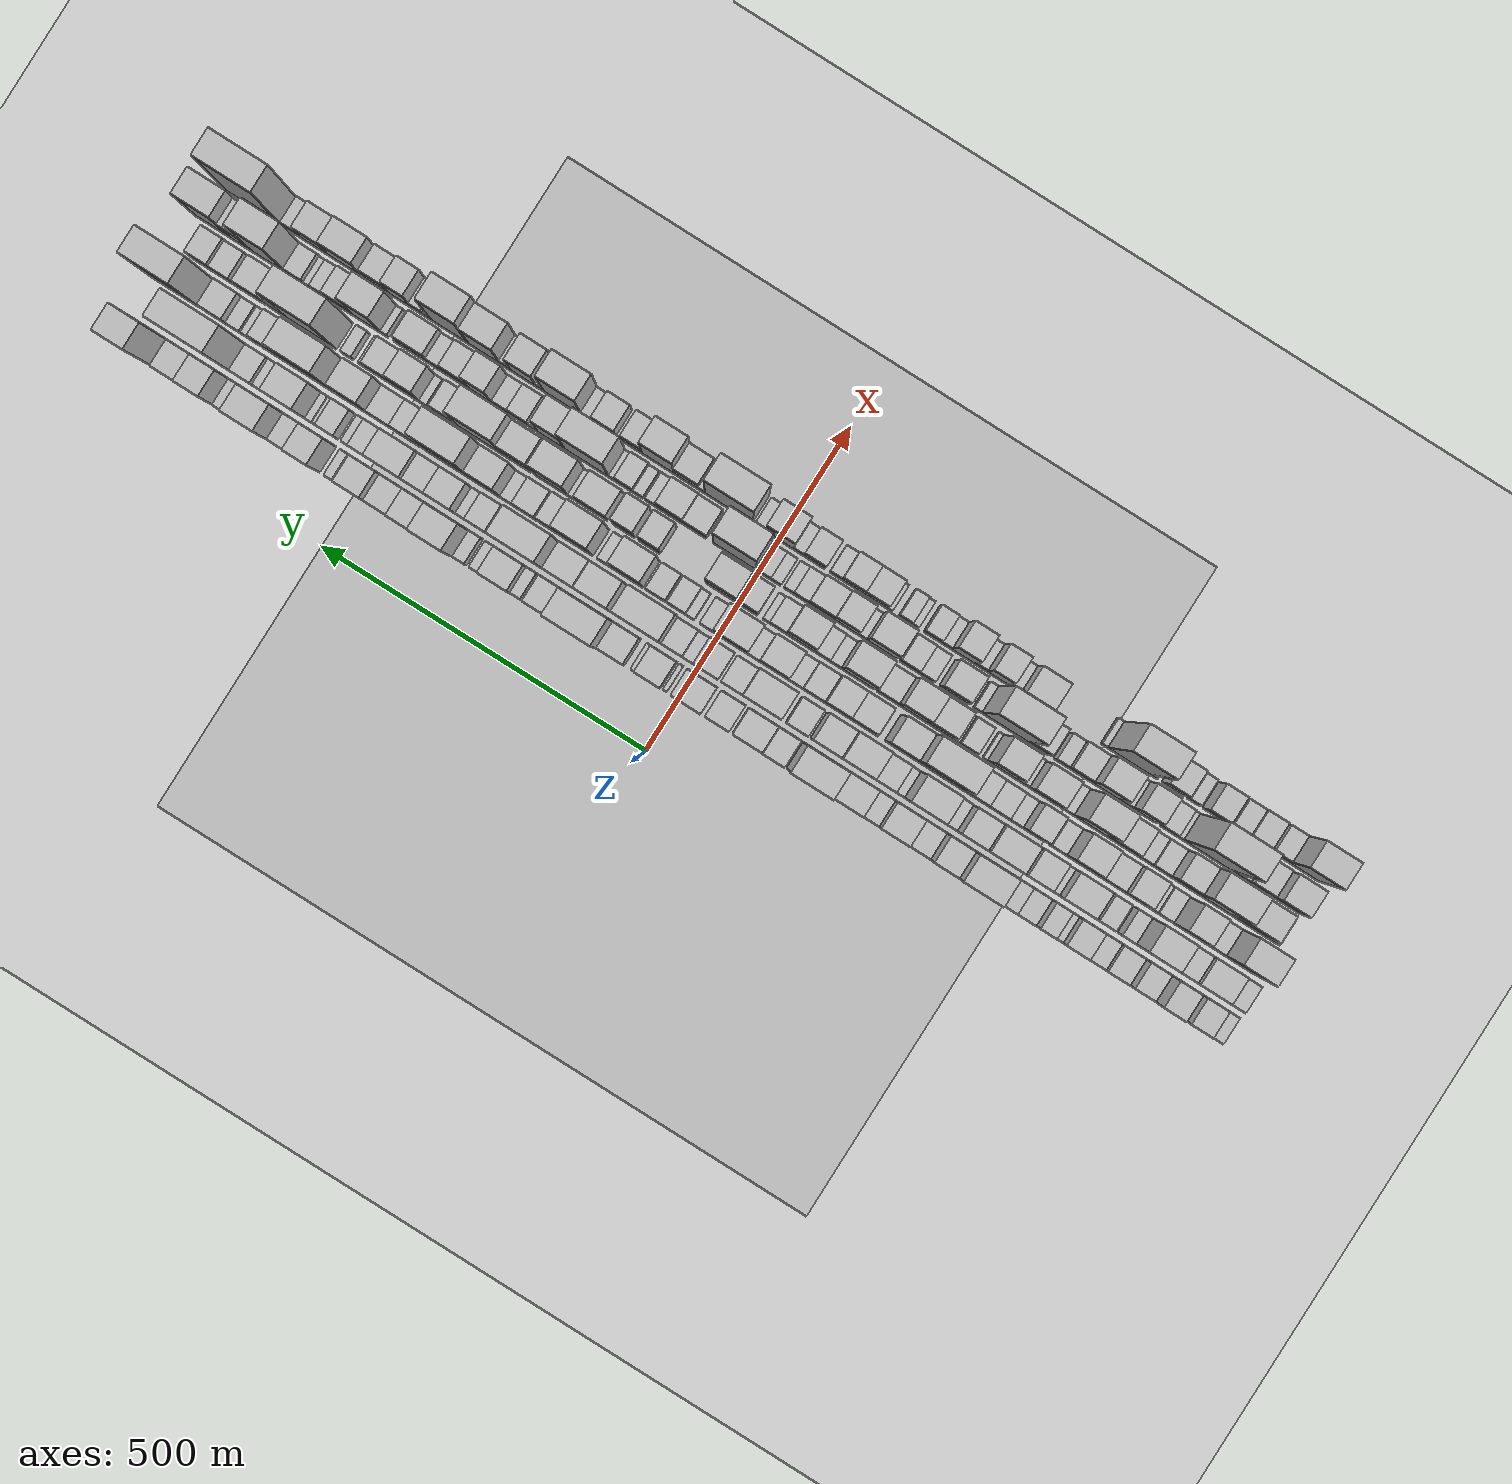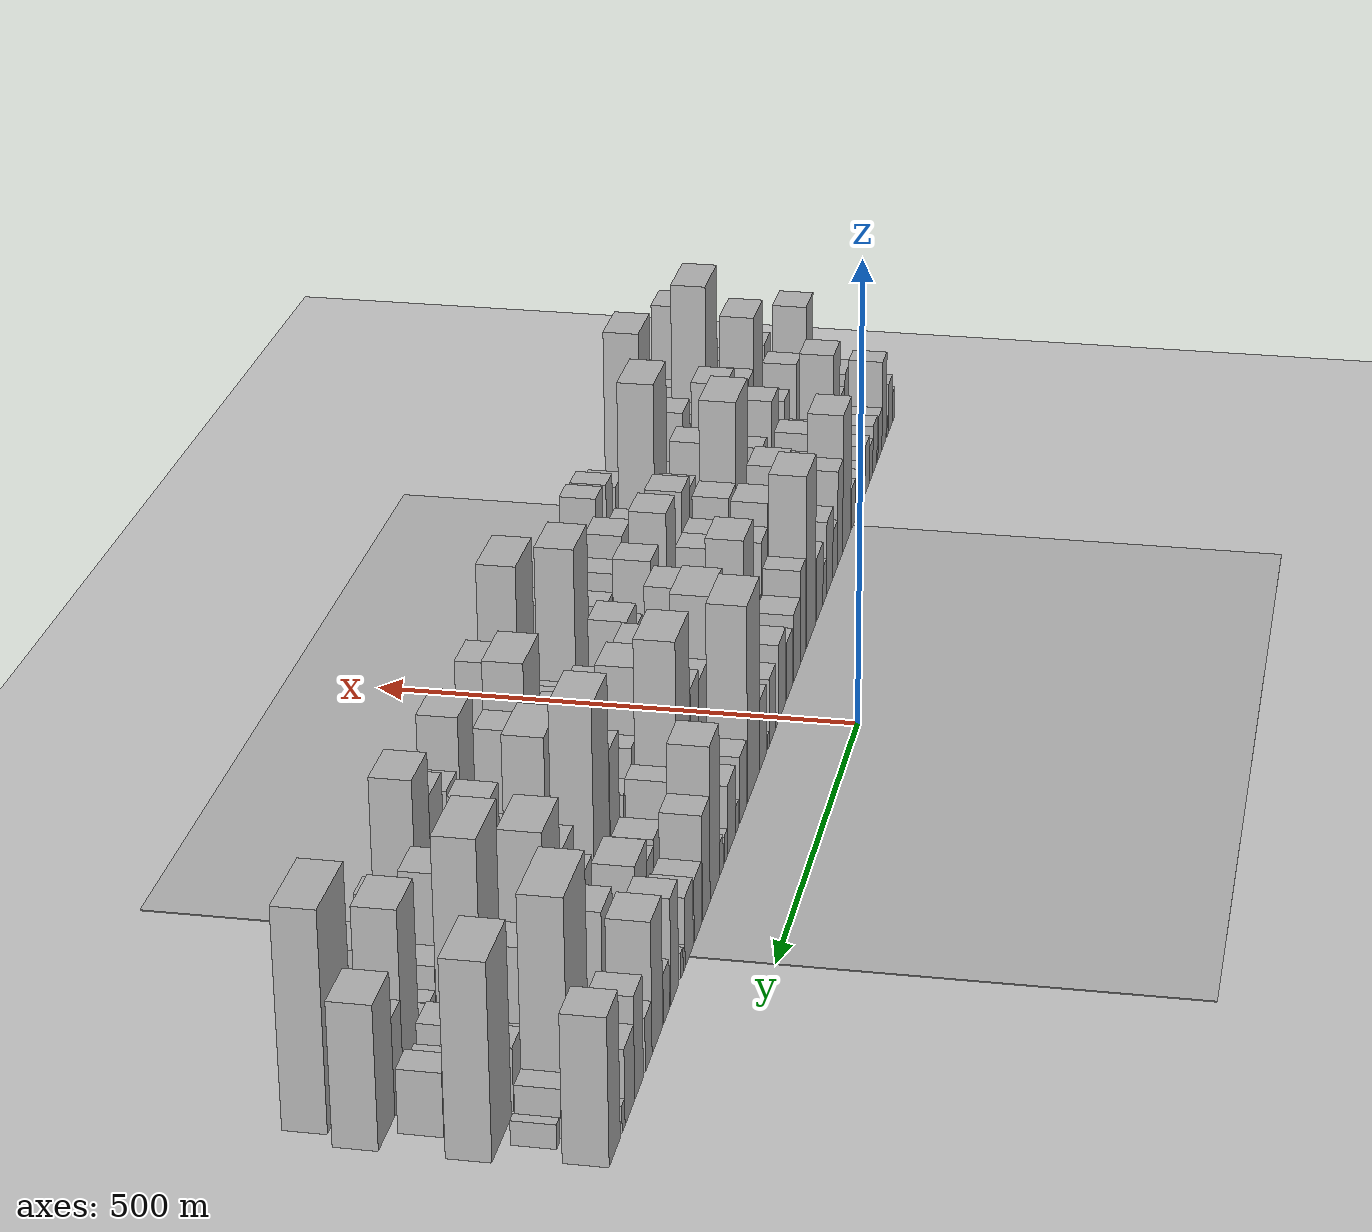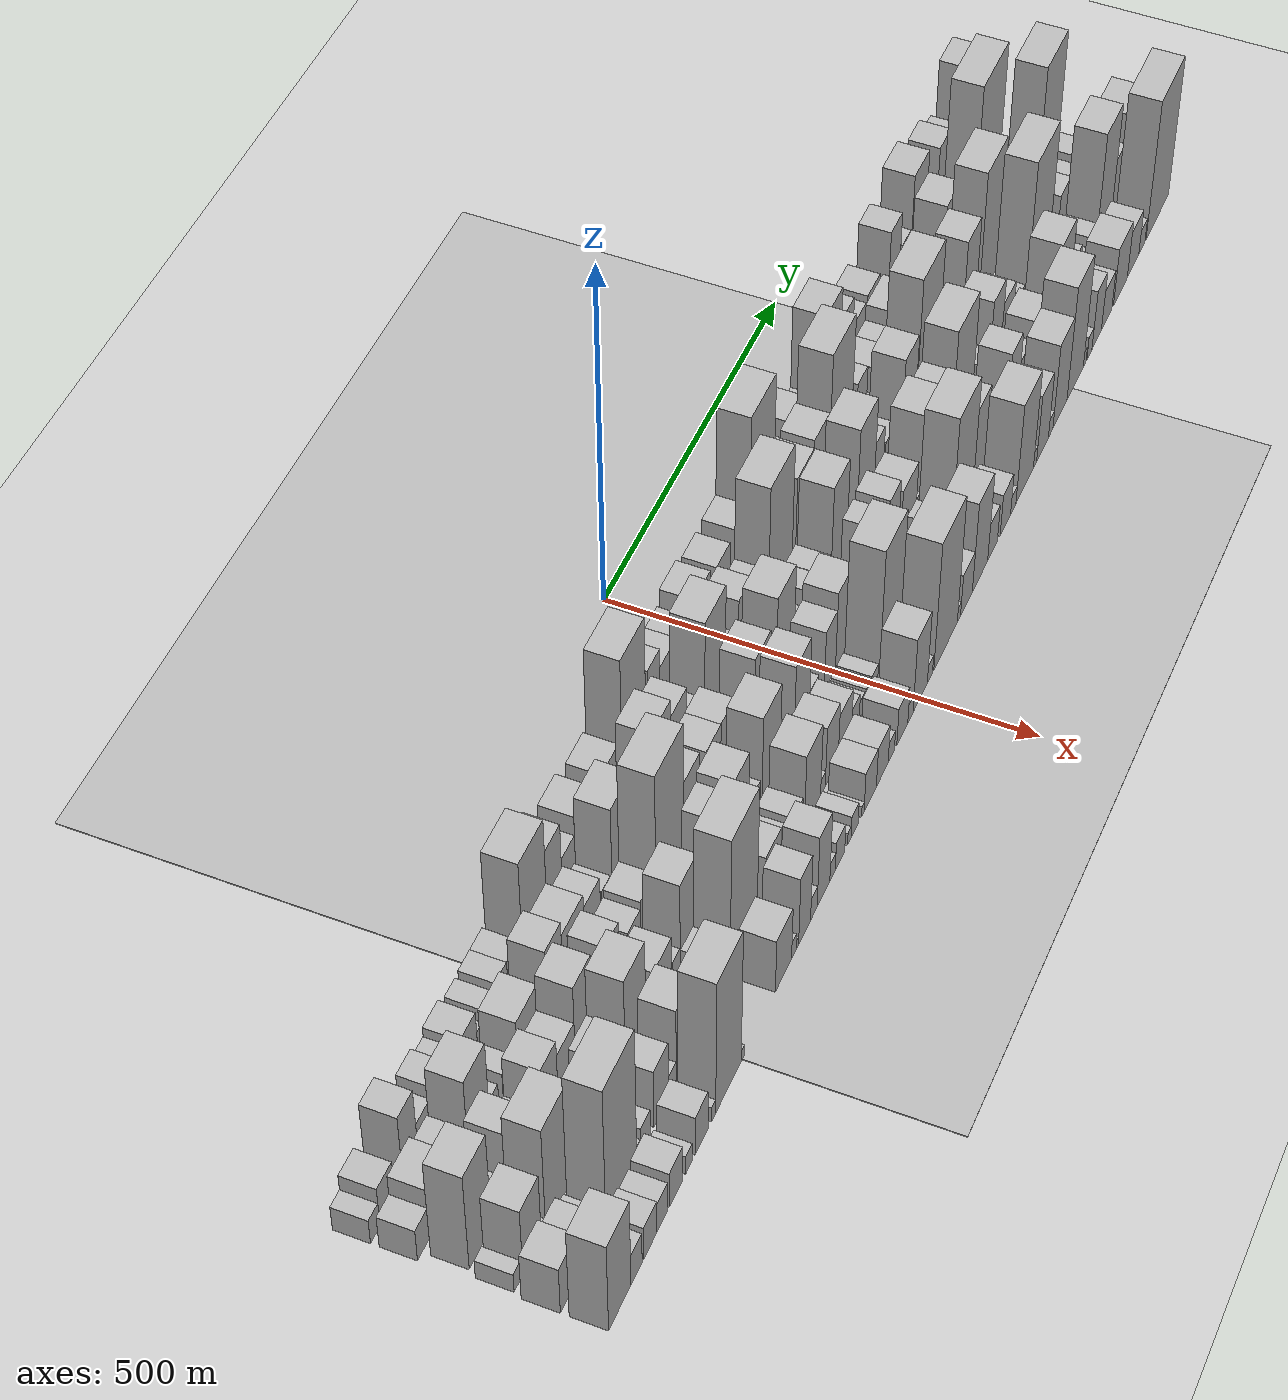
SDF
<?xml version="1.0" encoding="utf-8"?>

<sdf version="1.6">

   <world name="default">

      <gui fullscreen="0">

         <camera name="user_camera">

            <pose>-15 0 4.57585 0 0 0</pose>

            <view_controller>orbit</view_controller>

         </camera>

      </gui>

      <scene>

         <sky>

           <clouds>

             <speed>12</speed>

           </clouds>

         </sky>

         <ambient>0.4 0.4 0.4 1</ambient>

         <background>0.7 0.7 0.7 1</background>

         <shadows>1</shadows>

      </scene>

      <gravity>0 0 -9.8066</gravity>

      <magnetic_field>6e-06 2.3e-05 -4.2e-05</magnetic_field>

      <physics default="0" name="default_physics" type="ode">

         <ode>

            <solver>

               <type>quick</type>

               <iters>10</iters>

               <sor>1.0</sor>

               <use_dynamic_moi_rescaling>0</use_dynamic_moi_rescaling>

            </solver>

            <constraints>

               <cfm>0</cfm>

               <erp>0.2</erp>

               <contact_max_correcting_vel>100</contact_max_correcting_vel>

               <contact_surface_layer>0.001</contact_surface_layer>

            </constraints>

         </ode>

         <max_step_size>0.004</max_step_size>

         <real_time_factor>1</real_time_factor>

         <real_time_update_rate>250</real_time_update_rate>

      </physics>

      <light name="sun" type="directional">

         <cast_shadows>1</cast_shadows>

         <pose>0 0 10 0 0 0</pose>

         <diffuse>0.8 0.8 0.8 1</diffuse>

         <specular>0.2 0.2 0.2 1</specular>

         <attenuation>

            <range>1000</range>

            <constant>0.9</constant>

            <linear>0.01</linear>

            <quadratic>0.001</quadratic>

         </attenuation>

         <direction>-0.5 0.1 -0.9</direction>

      </light>

      <include>

         <name>ground_plane_1</name>

         <uri>model://HANNAS_ground_plane</uri>

         <pose>0 0 0  0 0 0</pose>

      </include>

      <include>

         <name>ground_plane_2</name>

         <uri>model://HANNAS_ground_plane</uri>

         <pose>100 0 0  0 0 0</pose>

      </include>

      <model name="building_1">

         <static>1</static>

         <pose frame="">100.0000 -819.4514 0 0.000000 0.000000 0.000000</pose>

         <link name="link">

            <pose frame="">0 0 19.50 0 0 0</pose>

            <collision name="collision">

               <geometry>

                  <box>

                     <size>40.0000 21.0972 39.0000</size>

                  </box>

               </geometry>

               <max_contacts>10</max_contacts>

               <surface>

                  <contact>

                     <ode/>

                  </contact>

                  <bounce/>

                  <friction>

                     <torsional>

                        <ode/>

                     </torsional>

                     <ode/>

                  </friction>

               </surface>

            </collision>

            <visual name="visual">

               <cast_shadows>0</cast_shadows>

               <geometry>

                  <box>

                     <size>40.0000 21.0972 39.0000</size>

                  </box>

               </geometry>

               <material>

                  <script>

                     <uri>model://HANNAS_wall/materials/scripts</uri>

                     <uri>model://HANNAS_wall/materials/textures</uri>

                     <name>vrc/HANNAS_wall</name>

                  </script>

               </material>

            </visual>

            <self_collide>0</self_collide>

            <enable_wind>0</enable_wind>

            <kinematic>0</kinematic>

         </link>

      </model>

      <model name="building_2">

         <static>1</static>

         <pose frame="">100.0000 -792.2812 0 0.000000 0.000000 0.000000</pose>

         <link name="link">

            <pose frame="">0 0 31.50 0 0 0</pose>

            <collision name="collision">

               <geometry>

                  <box>

                     <size>40.0000 33.2433 63.0000</size>

                  </box>

               </geometry>

               <max_contacts>10</max_contacts>

               <surface>

                  <contact>

                     <ode/>

                  </contact>

                  <bounce/>

                  <friction>

                     <torsional>

                        <ode/>

                     </torsional>

                     <ode/>

                  </friction>

               </surface>

            </collision>

            <visual name="visual">

               <cast_shadows>0</cast_shadows>

               <geometry>

                  <box>

                     <size>40.0000 33.2433 63.0000</size>

                  </box>

               </geometry>

               <material>

                  <script>

                     <uri>model://HANNAS_wall/materials/scripts</uri>

                     <uri>model://HANNAS_wall/materials/textures</uri>

                     <name>vrc/HANNAS_wall</name>

                  </script>

               </material>

            </visual>

            <self_collide>0</self_collide>

            <enable_wind>0</enable_wind>

            <kinematic>0</kinematic>

         </link>

      </model>

      <model name="building_3">

         <static>1</static>

         <pose frame="">100.0000 -770.7616 0 0.000000 0.000000 0.000000</pose>

         <link name="link">

            <pose frame="">0 0 12.00 0 0 0</pose>

            <collision name="collision">

               <geometry>

                  <box>

                     <size>40.0000 9.7958 24.0000</size>

                  </box>

               </geometry>

               <max_contacts>10</max_contacts>

               <surface>

                  <contact>

                     <ode/>

                  </contact>

                  <bounce/>

                  <friction>

                     <torsional>

                        <ode/>

                     </torsional>

                     <ode/>

                  </friction>

               </surface>

            </collision>

            <visual name="visual">

               <cast_shadows>0</cast_shadows>

               <geometry>

                  <box>

                     <size>40.0000 9.7958 24.0000</size>

                  </box>

               </geometry>

               <material>

                  <script>

                     <uri>model://HANNAS_wall/materials/scripts</uri>

                     <uri>model://HANNAS_wall/materials/textures</uri>

                     <name>vrc/HANNAS_wall</name>

                  </script>

               </material>

            </visual>

            <self_collide>0</self_collide>

            <enable_wind>0</enable_wind>

            <kinematic>0</kinematic>

         </link>

      </model>

      <model name="building_4">

         <static>1</static>

         <pose frame="">100.0000 -740.9503 0 0.000000 0.000000 0.000000</pose>

         <link name="link">

            <pose frame="">0 0 55.50 0 0 0</pose>

            <collision name="collision">

               <geometry>

                  <box>

                     <size>40.0000 33.8269 111.0000</size>

                  </box>

               </geometry>

               <max_contacts>10</max_contacts>

               <surface>

                  <contact>

                     <ode/>

                  </contact>

                  <bounce/>

                  <friction>

                     <torsional>

                        <ode/>

                     </torsional>

                     <ode/>

                  </friction>

               </surface>

            </collision>

            <visual name="visual">

               <cast_shadows>0</cast_shadows>

               <geometry>

                  <box>

                     <size>40.0000 33.8269 111.0000</size>

                  </box>

               </geometry>

               <material>

                  <script>

                     <uri>model://HANNAS_wall/materials/scripts</uri>

                     <uri>model://HANNAS_wall/materials/textures</uri>

                     <name>vrc/HANNAS_wall</name>

                  </script>

               </material>

            </visual>

            <self_collide>0</self_collide>

            <enable_wind>0</enable_wind>

            <kinematic>0</kinematic>

         </link>

      </model>

      <model name="building_5">

         <static>1</static>

         <pose frame="">100.0000 -708.1528 0 0.000000 0.000000 0.000000</pose>

         <link name="link">

            <pose frame="">0 0 27.00 0 0 0</pose>

            <collision name="collision">

               <geometry>

                  <box>

                     <size>40.0000 31.7680 54.0000</size>

                  </box>

               </geometry>

               <max_contacts>10</max_contacts>

               <surface>

                  <contact>

                     <ode/>

                  </contact>

                  <bounce/>

                  <friction>

                     <torsional>

                        <ode/>

                     </torsional>

                     <ode/>

                  </friction>

               </surface>

            </collision>

            <visual name="visual">

               <cast_shadows>0</cast_shadows>

               <geometry>

                  <box>

                     <size>40.0000 31.7680 54.0000</size>

                  </box>

               </geometry>

               <material>

                  <script>

                     <uri>model://HANNAS_wall/materials/scripts</uri>

                     <uri>model://HANNAS_wall/materials/textures</uri>

                     <name>vrc/HANNAS_wall</name>

                  </script>

               </material>

            </visual>

            <self_collide>0</self_collide>

            <enable_wind>0</enable_wind>

            <kinematic>0</kinematic>

         </link>

      </model>

      <model name="building_6">

         <static>1</static>

         <pose frame="">100.0000 -687.9147 0 0.000000 0.000000 0.000000</pose>

         <link name="link">

            <pose frame="">0 0 9.00 0 0 0</pose>

            <collision name="collision">

               <geometry>

                  <box>

                     <size>40.0000 8.7083 18.0000</size>

                  </box>

               </geometry>

               <max_contacts>10</max_contacts>

               <surface>

                  <contact>

                     <ode/>

                  </contact>

                  <bounce/>

                  <friction>

                     <torsional>

                        <ode/>

                     </torsional>

                     <ode/>

                  </friction>

               </surface>

            </collision>

            <visual name="visual">

               <cast_shadows>0</cast_shadows>

               <geometry>

                  <box>

                     <size>40.0000 8.7083 18.0000</size>

                  </box>

               </geometry>

               <material>

                  <script>

                     <uri>model://HANNAS_wall/materials/scripts</uri>

                     <uri>model://HANNAS_wall/materials/textures</uri>

                     <name>vrc/HANNAS_wall</name>

                  </script>

               </material>

            </visual>

            <self_collide>0</self_collide>

            <enable_wind>0</enable_wind>

            <kinematic>0</kinematic>

         </link>

      </model>

      <model name="building_7">

         <static>1</static>

         <pose frame="">100.0000 -666.9556 0 0.000000 0.000000 0.000000</pose>

         <link name="link">

            <pose frame="">0 0 30.00 0 0 0</pose>

            <collision name="collision">

               <geometry>

                  <box>

                     <size>40.0000 33.2100 60.0000</size>

                  </box>

               </geometry>

               <max_contacts>10</max_contacts>

               <surface>

                  <contact>

                     <ode/>

                  </contact>

                  <bounce/>

                  <friction>

                     <torsional>

                        <ode/>

                     </torsional>

                     <ode/>

                  </friction>

               </surface>

            </collision>

            <visual name="visual">

               <cast_shadows>0</cast_shadows>

               <geometry>

                  <box>

                     <size>40.0000 33.2100 60.0000</size>

                  </box>

               </geometry>

               <material>

                  <script>

                     <uri>model://HANNAS_wall/materials/scripts</uri>

                     <uri>model://HANNAS_wall/materials/textures</uri>

                     <name>vrc/HANNAS_wall</name>

                  </script>

               </material>

            </visual>

            <self_collide>0</self_collide>

            <enable_wind>0</enable_wind>

            <kinematic>0</kinematic>

         </link>

      </model>

      <model name="building_8">

         <static>1</static>

         <pose frame="">100.0000 -636.9389 0 0.000000 0.000000 0.000000</pose>

         <link name="link">

            <pose frame="">0 0 22.50 0 0 0</pose>

            <collision name="collision">

               <geometry>

                  <box>

                     <size>40.0000 26.8234 45.0000</size>

                  </box>

               </geometry>

               <max_contacts>10</max_contacts>

               <surface>

                  <contact>

                     <ode/>

                  </contact>

                  <bounce/>

                  <friction>

                     <torsional>

                        <ode/>

                     </torsional>

                     <ode/>

                  </friction>

               </surface>

            </collision>

            <visual name="visual">

               <cast_shadows>0</cast_shadows>

               <geometry>

                  <box>

                     <size>40.0000 26.8234 45.0000</size>

                  </box>

               </geometry>

               <material>

                  <script>

                     <uri>model://HANNAS_wall/materials/scripts</uri>

                     <uri>model://HANNAS_wall/materials/textures</uri>

                     <name>vrc/HANNAS_wall</name>

                  </script>

               </material>

            </visual>

            <self_collide>0</self_collide>

            <enable_wind>0</enable_wind>

            <kinematic>0</kinematic>

         </link>

      </model>

      <model name="building_9">

         <static>1</static>

         <pose frame="">100.0000 -605.7513 0 0.000000 0.000000 0.000000</pose>

         <link name="link">

            <pose frame="">0 0 30.00 0 0 0</pose>

            <collision name="collision">

               <geometry>

                  <box>

                     <size>40.0000 35.5518 60.0000</size>

                  </box>

               </geometry>

               <max_contacts>10</max_contacts>

               <surface>

                  <contact>

                     <ode/>

                  </contact>

                  <bounce/>

                  <friction>

                     <torsional>

                        <ode/>

                     </torsional>

                     <ode/>

                  </friction>

               </surface>

            </collision>

            <visual name="visual">

               <cast_shadows>0</cast_shadows>

               <geometry>

                  <box>

                     <size>40.0000 35.5518 60.0000</size>

                  </box>

               </geometry>

               <material>

                  <script>

                     <uri>model://HANNAS_wall/materials/scripts</uri>

                     <uri>model://HANNAS_wall/materials/textures</uri>

                     <name>vrc/HANNAS_wall</name>

                  </script>

               </material>

            </visual>

            <self_collide>0</self_collide>

            <enable_wind>0</enable_wind>

            <kinematic>0</kinematic>

         </link>

      </model>

      <model name="building_10">

         <static>1</static>

         <pose frame="">100.0000 -581.5288 0 0.000000 0.000000 0.000000</pose>

         <link name="link">

            <pose frame="">0 0 13.50 0 0 0</pose>

            <collision name="collision">

               <geometry>

                  <box>

                     <size>40.0000 12.8933 27.0000</size>

                  </box>

               </geometry>

               <max_contacts>10</max_contacts>

               <surface>

                  <contact>

                     <ode/>

                  </contact>

                  <bounce/>

                  <friction>

                     <torsional>

                        <ode/>

                     </torsional>

                     <ode/>

                  </friction>

               </surface>

            </collision>

            <visual name="visual">

               <cast_shadows>0</cast_shadows>

               <geometry>

                  <box>

                     <size>40.0000 12.8933 27.0000</size>

                  </box>

               </geometry>

               <material>

                  <script>

                     <uri>model://HANNAS_wall/materials/scripts</uri>

                     <uri>model://HANNAS_wall/materials/textures</uri>

                     <name>vrc/HANNAS_wall</name>

                  </script>

               </material>

            </visual>

            <self_collide>0</self_collide>

            <enable_wind>0</enable_wind>

            <kinematic>0</kinematic>

         </link>

      </model>

      <model name="building_11">

         <static>1</static>

         <pose frame="">100.0000 -562.5488 0 0.000000 0.000000 0.000000</pose>

         <link name="link">

            <pose frame="">0 0 24.00 0 0 0</pose>

            <collision name="collision">

               <geometry>

                  <box>

                     <size>40.0000 25.0665 48.0000</size>

                  </box>

               </geometry>

               <max_contacts>10</max_contacts>

               <surface>

                  <contact>

                     <ode/>

                  </contact>

                  <bounce/>

                  <friction>

                     <torsional>

                        <ode/>

                     </torsional>

                     <ode/>

                  </friction>

               </surface>

            </collision>

            <visual name="visual">

               <cast_shadows>0</cast_shadows>

               <geometry>

                  <box>

                     <size>40.0000 25.0665 48.0000</size>

                  </box>

               </geometry>

               <material>

                  <script>

                     <uri>model://HANNAS_wall/materials/scripts</uri>

                     <uri>model://HANNAS_wall/materials/textures</uri>

                     <name>vrc/HANNAS_wall</name>

                  </script>

               </material>

            </visual>

            <self_collide>0</self_collide>

            <enable_wind>0</enable_wind>

            <kinematic>0</kinematic>

         </link>

      </model>

      <model name="building_12">

         <static>1</static>

         <pose frame="">100.0000 -529.0924 0 0.000000 0.000000 0.000000</pose>

         <link name="link">

            <pose frame="">0 0 25.50 0 0 0</pose>

            <collision name="collision">

               <geometry>

                  <box>

                     <size>40.0000 27.8463 51.0000</size>

                  </box>

               </geometry>

               <max_contacts>10</max_contacts>

               <surface>

                  <contact>

                     <ode/>

                  </contact>

                  <bounce/>

                  <friction>

                     <torsional>

                        <ode/>

                     </torsional>

                     <ode/>

                  </friction>

               </surface>

            </collision>

            <visual name="visual">

               <cast_shadows>0</cast_shadows>

               <geometry>

                  <box>

                     <size>40.0000 27.8463 51.0000</size>

                  </box>

               </geometry>

               <material>

                  <script>

                     <uri>model://HANNAS_wall/materials/scripts</uri>

                     <uri>model://HANNAS_wall/materials/textures</uri>

                     <name>vrc/HANNAS_wall</name>

                  </script>

               </material>

            </visual>

            <self_collide>0</self_collide>

            <enable_wind>0</enable_wind>

            <kinematic>0</kinematic>

         </link>

      </model>

      <model name="building_13">

         <static>1</static>

         <pose frame="">100.0000 -500.6283 0 0.000000 0.000000 0.000000</pose>

         <link name="link">

            <pose frame="">0 0 25.50 0 0 0</pose>

            <collision name="collision">

               <geometry>

                  <box>

                     <size>40.0000 29.0821 51.0000</size>

                  </box>

               </geometry>

               <max_contacts>10</max_contacts>

               <surface>

                  <contact>

                     <ode/>

                  </contact>

                  <bounce/>

                  <friction>

                     <torsional>

                        <ode/>

                     </torsional>

                     <ode/>

                  </friction>

               </surface>

            </collision>

            <visual name="visual">

               <cast_shadows>0</cast_shadows>

               <geometry>

                  <box>

                     <size>40.0000 29.0821 51.0000</size>

                  </box>

               </geometry>

               <material>

                  <script>

                     <uri>model://HANNAS_wall/materials/scripts</uri>

                     <uri>model://HANNAS_wall/materials/textures</uri>

                     <name>vrc/HANNAS_wall</name>

                  </script>

               </material>

            </visual>

            <self_collide>0</self_collide>

            <enable_wind>0</enable_wind>

            <kinematic>0</kinematic>

         </link>

      </model>

      <model name="building_14">

         <static>1</static>

         <pose frame="">100.0000 -449.3956 0 0.000000 0.000000 0.000000</pose>

         <link name="link">

            <pose frame="">0 0 82.50 0 0 0</pose>

            <collision name="collision">

               <geometry>

                  <box>

                     <size>40.0000 59.3832 165.0000</size>

                  </box>

               </geometry>

               <max_contacts>10</max_contacts>

               <surface>

                  <contact>

                     <ode/>

                  </contact>

                  <bounce/>

                  <friction>

                     <torsional>

                        <ode/>

                     </torsional>

                     <ode/>

                  </friction>

               </surface>

            </collision>

            <visual name="visual">

               <cast_shadows>0</cast_shadows>

               <geometry>

                  <box>

                     <size>40.0000 59.3832 165.0000</size>

                  </box>

               </geometry>

               <material>

                  <script>

                     <uri>model://HANNAS_wall/materials/scripts</uri>

                     <uri>model://HANNAS_wall/materials/textures</uri>

                     <name>vrc/HANNAS_wall</name>

                  </script>

               </material>

            </visual>

            <self_collide>0</self_collide>

            <enable_wind>0</enable_wind>

            <kinematic>0</kinematic>

         </link>

      </model>

      <model name="building_15">

         <static>1</static>

         <pose frame="">100.0000 -401.0280 0 0.000000 0.000000 0.000000</pose>

         <link name="link">

            <pose frame="">0 0 57.00 0 0 0</pose>

            <collision name="collision">

               <geometry>

                  <box>

                     <size>40.0000 37.3520 114.0000</size>

                  </box>

               </geometry>

               <max_contacts>10</max_contacts>

               <surface>

                  <contact>

                     <ode/>

                  </contact>

                  <bounce/>

                  <friction>

                     <torsional>

                        <ode/>

                     </torsional>

                     <ode/>

                  </friction>

               </surface>

            </collision>

            <visual name="visual">

               <cast_shadows>0</cast_shadows>

               <geometry>

                  <box>

                     <size>40.0000 37.3520 114.0000</size>

                  </box>

               </geometry>

               <material>

                  <script>

                     <uri>model://HANNAS_wall/materials/scripts</uri>

                     <uri>model://HANNAS_wall/materials/textures</uri>

                     <name>vrc/HANNAS_wall</name>

                  </script>

               </material>

            </visual>

            <self_collide>0</self_collide>

            <enable_wind>0</enable_wind>

            <kinematic>0</kinematic>

         </link>

      </model>

      <model name="building_16">

         <static>1</static>

         <pose frame="">100.0000 -365.7346 0 0.000000 0.000000 0.000000</pose>

         <link name="link">

            <pose frame="">0 0 28.50 0 0 0</pose>

            <collision name="collision">

               <geometry>

                  <box>

                     <size>40.0000 33.2348 57.0000</size>

                  </box>

               </geometry>

               <max_contacts>10</max_contacts>

               <surface>

                  <contact>

                     <ode/>

                  </contact>

                  <bounce/>

                  <friction>

                     <torsional>

                        <ode/>

                     </torsional>

                     <ode/>

                  </friction>

               </surface>

            </collision>

            <visual name="visual">

               <cast_shadows>0</cast_shadows>

               <geometry>

                  <box>

                     <size>40.0000 33.2348 57.0000</size>

                  </box>

               </geometry>

               <material>

                  <script>

                     <uri>model://HANNAS_wall/materials/scripts</uri>

                     <uri>model://HANNAS_wall/materials/textures</uri>

                     <name>vrc/HANNAS_wall</name>

                  </script>

               </material>

            </visual>

            <self_collide>0</self_collide>

            <enable_wind>0</enable_wind>

            <kinematic>0</kinematic>

         </link>

      </model>

      <model name="building_17">

         <static>1</static>

         <pose frame="">100.0000 -327.2000 0 0.000000 0.000000 0.000000</pose>

         <link name="link">

            <pose frame="">0 0 43.50 0 0 0</pose>

            <collision name="collision">

               <geometry>

                  <box>

                     <size>40.0000 43.8345 87.0000</size>

                  </box>

               </geometry>

               <max_contacts>10</max_contacts>

               <surface>

                  <contact>

                     <ode/>

                  </contact>

                  <bounce/>

                  <friction>

                     <torsional>

                        <ode/>

                     </torsional>

                     <ode/>

                  </friction>

               </surface>

            </collision>

            <visual name="visual">

               <cast_shadows>0</cast_shadows>

               <geometry>

                  <box>

                     <size>40.0000 43.8345 87.0000</size>

                  </box>

               </geometry>

               <material>

                  <script>

                     <uri>model://HANNAS_wall/materials/scripts</uri>

                     <uri>model://HANNAS_wall/materials/textures</uri>

                     <name>vrc/HANNAS_wall</name>

                  </script>

               </material>

            </visual>

            <self_collide>0</self_collide>

            <enable_wind>0</enable_wind>

            <kinematic>0</kinematic>

         </link>

      </model>

      <model name="building_18">

         <static>1</static>

         <pose frame="">100.0000 -292.6495 0 0.000000 0.000000 0.000000</pose>

         <link name="link">

            <pose frame="">0 0 22.50 0 0 0</pose>

            <collision name="collision">

               <geometry>

                  <box>

                     <size>40.0000 25.2666 45.0000</size>

                  </box>

               </geometry>

               <max_contacts>10</max_contacts>

               <surface>

                  <contact>

                     <ode/>

                  </contact>

                  <bounce/>

                  <friction>

                     <torsional>

                        <ode/>

                     </torsional>

                     <ode/>

                  </friction>

               </surface>

            </collision>

            <visual name="visual">

               <cast_shadows>0</cast_shadows>

               <geometry>

                  <box>

                     <size>40.0000 25.2666 45.0000</size>

                  </box>

               </geometry>

               <material>

                  <script>

                     <uri>model://HANNAS_wall/materials/scripts</uri>

                     <uri>model://HANNAS_wall/materials/textures</uri>

                     <name>vrc/HANNAS_wall</name>

                  </script>

               </material>

            </visual>

            <self_collide>0</self_collide>

            <enable_wind>0</enable_wind>

            <kinematic>0</kinematic>

         </link>

      </model>

      <model name="building_19">

         <static>1</static>

         <pose frame="">100.0000 -257.8075 0 0.000000 0.000000 0.000000</pose>

         <link name="link">

            <pose frame="">0 0 37.50 0 0 0</pose>

            <collision name="collision">

               <geometry>

                  <box>

                     <size>40.0000 44.4174 75.0000</size>

                  </box>

               </geometry>

               <max_contacts>10</max_contacts>

               <surface>

                  <contact>

                     <ode/>

                  </contact>

                  <bounce/>

                  <friction>

                     <torsional>

                        <ode/>

                     </torsional>

                     <ode/>

                  </friction>

               </surface>

            </collision>

            <visual name="visual">

               <cast_shadows>0</cast_shadows>

               <geometry>

                  <box>

                     <size>40.0000 44.4174 75.0000</size>

                  </box>

               </geometry>

               <material>

                  <script>

                     <uri>model://HANNAS_wall/materials/scripts</uri>

                     <uri>model://HANNAS_wall/materials/textures</uri>

                     <name>vrc/HANNAS_wall</name>

                  </script>

               </material>

            </visual>

            <self_collide>0</self_collide>

            <enable_wind>0</enable_wind>

            <kinematic>0</kinematic>

         </link>

      </model>

      <model name="building_20">

         <static>1</static>

         <pose frame="">100.0000 -197.3069 0 0.000000 0.000000 0.000000</pose>

         <link name="link">

            <pose frame="">0 0 99.00 0 0 0</pose>

            <collision name="collision">

               <geometry>

                  <box>

                     <size>40.0000 62.5837 198.0000</size>

                  </box>

               </geometry>

               <max_contacts>10</max_contacts>

               <surface>

                  <contact>

                     <ode/>

                  </contact>

                  <bounce/>

                  <friction>

                     <torsional>

                        <ode/>

                     </torsional>

                     <ode/>

                  </friction>

               </surface>

            </collision>

            <visual name="visual">

               <cast_shadows>0</cast_shadows>

               <geometry>

                  <box>

                     <size>40.0000 62.5837 198.0000</size>

                  </box>

               </geometry>

               <material>

                  <script>

                     <uri>model://HANNAS_wall/materials/scripts</uri>

                     <uri>model://HANNAS_wall/materials/textures</uri>

                     <name>vrc/HANNAS_wall</name>

                  </script>

               </material>

            </visual>

            <self_collide>0</self_collide>

            <enable_wind>0</enable_wind>

            <kinematic>0</kinematic>

         </link>

      </model>

      <model name="building_21">

         <static>1</static>

         <pose frame="">100.0000 -143.6256 0 0.000000 0.000000 0.000000</pose>

         <link name="link">

            <pose frame="">0 0 54.00 0 0 0</pose>

            <collision name="collision">

               <geometry>

                  <box>

                     <size>40.0000 32.7790 108.0000</size>

                  </box>

               </geometry>

               <max_contacts>10</max_contacts>

               <surface>

                  <contact>

                     <ode/>

                  </contact>

                  <bounce/>

                  <friction>

                     <torsional>

                        <ode/>

                     </torsional>

                     <ode/>

                  </friction>

               </surface>

            </collision>

            <visual name="visual">

               <cast_shadows>0</cast_shadows>

               <geometry>

                  <box>

                     <size>40.0000 32.7790 108.0000</size>

                  </box>

               </geometry>

               <material>

                  <script>

                     <uri>model://HANNAS_wall/materials/scripts</uri>

                     <uri>model://HANNAS_wall/materials/textures</uri>

                     <name>vrc/HANNAS_wall</name>

                  </script>

               </material>

            </visual>

            <self_collide>0</self_collide>

            <enable_wind>0</enable_wind>

            <kinematic>0</kinematic>

         </link>

      </model>

      <model name="building_22">

         <static>1</static>

         <pose frame="">100.0000 -104.7117 0 0.000000 0.000000 0.000000</pose>

         <link name="link">

            <pose frame="">0 0 39.00 0 0 0</pose>

            <collision name="collision">

               <geometry>

                  <box>

                     <size>40.0000 45.0487 78.0000</size>

                  </box>

               </geometry>

               <max_contacts>10</max_contacts>

               <surface>

                  <contact>

                     <ode/>

                  </contact>

                  <bounce/>

                  <friction>

                     <torsional>

                        <ode/>

                     </torsional>

                     <ode/>

                  </friction>

               </surface>

            </collision>

            <visual name="visual">

               <cast_shadows>0</cast_shadows>

               <geometry>

                  <box>

                     <size>40.0000 45.0487 78.0000</size>

                  </box>

               </geometry>

               <material>

                  <script>

                     <uri>model://HANNAS_wall/materials/scripts</uri>

                     <uri>model://HANNAS_wall/materials/textures</uri>

                     <name>vrc/HANNAS_wall</name>

                  </script>

               </material>

            </visual>

            <self_collide>0</self_collide>

            <enable_wind>0</enable_wind>

            <kinematic>0</kinematic>

         </link>

      </model>

      <model name="building_23">

         <static>1</static>

         <pose frame="">100.0000 -58.7064 0 0.000000 0.000000 0.000000</pose>

         <link name="link">

            <pose frame="">0 0 33.00 0 0 0</pose>

            <collision name="collision">

               <geometry>

                  <box>

                     <size>40.0000 36.9619 66.0000</size>

                  </box>

               </geometry>

               <max_contacts>10</max_contacts>

               <surface>

                  <contact>

                     <ode/>

                  </contact>

                  <bounce/>

                  <friction>

                     <torsional>

                        <ode/>

                     </torsional>

                     <ode/>

                  </friction>

               </surface>

            </collision>

            <visual name="visual">

               <cast_shadows>0</cast_shadows>

               <geometry>

                  <box>

                     <size>40.0000 36.9619 66.0000</size>

                  </box>

               </geometry>

               <material>

                  <script>

                     <uri>model://HANNAS_wall/materials/scripts</uri>

                     <uri>model://HANNAS_wall/materials/textures</uri>

                     <name>vrc/HANNAS_wall</name>

                  </script>

               </material>

            </visual>

            <self_collide>0</self_collide>

            <enable_wind>0</enable_wind>

            <kinematic>0</kinematic>

         </link>

      </model>

      <model name="building_24">

         <static>1</static>

         <pose frame="">100.0000 -11.5762 0 0.000000 0.000000 0.000000</pose>

         <link name="link">

            <pose frame="">0 0 43.50 0 0 0</pose>

            <collision name="collision">

               <geometry>

                  <box>

                     <size>40.0000 45.2983 87.0000</size>

                  </box>

               </geometry>

               <max_contacts>10</max_contacts>

               <surface>

                  <contact>

                     <ode/>

                  </contact>

                  <bounce/>

                  <friction>

                     <torsional>

                        <ode/>

                     </torsional>

                     <ode/>

                  </friction>

               </surface>

            </collision>

            <visual name="visual">

               <cast_shadows>0</cast_shadows>

               <geometry>

                  <box>

                     <size>40.0000 45.2983 87.0000</size>

                  </box>

               </geometry>

               <material>

                  <script>

                     <uri>model://HANNAS_wall/materials/scripts</uri>

                     <uri>model://HANNAS_wall/materials/textures</uri>

                     <name>vrc/HANNAS_wall</name>

                  </script>

               </material>

            </visual>

            <self_collide>0</self_collide>

            <enable_wind>0</enable_wind>

            <kinematic>0</kinematic>

         </link>

      </model>

      <model name="building_25">

         <static>1</static>

         <pose frame="">100.0000 21.3272 0 0.000000 0.000000 0.000000</pose>

         <link name="link">

            <pose frame="">0 0 7.50 0 0 0</pose>

            <collision name="collision">

               <geometry>

                  <box>

                     <size>40.0000 6.5086 15.0000</size>

                  </box>

               </geometry>

               <max_contacts>10</max_contacts>

               <surface>

                  <contact>

                     <ode/>

                  </contact>

                  <bounce/>

                  <friction>

                     <torsional>

                        <ode/>

                     </torsional>

                     <ode/>

                  </friction>

               </surface>

            </collision>

            <visual name="visual">

               <cast_shadows>0</cast_shadows>

               <geometry>

                  <box>

                     <size>40.0000 6.5086 15.0000</size>

                  </box>

               </geometry>

               <material>

                  <script>

                     <uri>model://HANNAS_wall/materials/scripts</uri>

                     <uri>model://HANNAS_wall/materials/textures</uri>

                     <name>vrc/HANNAS_wall</name>

                  </script>

               </material>

            </visual>

            <self_collide>0</self_collide>

            <enable_wind>0</enable_wind>

            <kinematic>0</kinematic>

         </link>

      </model>

      <model name="building_26">

         <static>1</static>

         <pose frame="">100.0000 47.0952 0 0.000000 0.000000 0.000000</pose>

         <link name="link">

            <pose frame="">0 0 37.50 0 0 0</pose>

            <collision name="collision">

               <geometry>

                  <box>

                     <size>40.0000 39.0274 75.0000</size>

                  </box>

               </geometry>

               <max_contacts>10</max_contacts>

               <surface>

                  <contact>

                     <ode/>

                  </contact>

                  <bounce/>

                  <friction>

                     <torsional>

                        <ode/>

                     </torsional>

                     <ode/>

                  </friction>

               </surface>

            </collision>

            <visual name="visual">

               <cast_shadows>0</cast_shadows>

               <geometry>

                  <box>

                     <size>40.0000 39.0274 75.0000</size>

                  </box>

               </geometry>

               <material>

                  <script>

                     <uri>model://HANNAS_wall/materials/scripts</uri>

                     <uri>model://HANNAS_wall/materials/textures</uri>

                     <name>vrc/HANNAS_wall</name>

                  </script>

               </material>

            </visual>

            <self_collide>0</self_collide>

            <enable_wind>0</enable_wind>

            <kinematic>0</kinematic>

         </link>

      </model>

      <model name="building_27">

         <static>1</static>

         <pose frame="">100.0000 70.4942 0 0.000000 0.000000 0.000000</pose>

         <link name="link">

            <pose frame="">0 0 9.00 0 0 0</pose>

            <collision name="collision">

               <geometry>

                  <box>

                     <size>40.0000 7.7707 18.0000</size>

                  </box>

               </geometry>

               <max_contacts>10</max_contacts>

               <surface>

                  <contact>

                     <ode/>

                  </contact>

                  <bounce/>

                  <friction>

                     <torsional>

                        <ode/>

                     </torsional>

                     <ode/>

                  </friction>

               </surface>

            </collision>

            <visual name="visual">

               <cast_shadows>0</cast_shadows>

               <geometry>

                  <box>

                     <size>40.0000 7.7707 18.0000</size>

                  </box>

               </geometry>

               <material>

                  <script>

                     <uri>model://HANNAS_wall/materials/scripts</uri>

                     <uri>model://HANNAS_wall/materials/textures</uri>

                     <name>vrc/HANNAS_wall</name>

                  </script>

               </material>

            </visual>

            <self_collide>0</self_collide>

            <enable_wind>0</enable_wind>

            <kinematic>0</kinematic>

         </link>

      </model>

      <model name="building_28">

         <static>1</static>

         <pose frame="">100.0000 103.2333 0 0.000000 0.000000 0.000000</pose>

         <link name="link">

            <pose frame="">0 0 39.00 0 0 0</pose>

            <collision name="collision">

               <geometry>

                  <box>

                     <size>40.0000 39.7075 78.0000</size>

                  </box>

               </geometry>

               <max_contacts>10</max_contacts>

               <surface>

                  <contact>

                     <ode/>

                  </contact>

                  <bounce/>

                  <friction>

                     <torsional>

                        <ode/>

                     </torsional>

                     <ode/>

                  </friction>

               </surface>

            </collision>

            <visual name="visual">

               <cast_shadows>0</cast_shadows>

               <geometry>

                  <box>

                     <size>40.0000 39.7075 78.0000</size>

                  </box>

               </geometry>

               <material>

                  <script>

                     <uri>model://HANNAS_wall/materials/scripts</uri>

                     <uri>model://HANNAS_wall/materials/textures</uri>

                     <name>vrc/HANNAS_wall</name>

                  </script>

               </material>

            </visual>

            <self_collide>0</self_collide>

            <enable_wind>0</enable_wind>

            <kinematic>0</kinematic>

         </link>

      </model>

      <model name="building_29">

         <static>1</static>

         <pose frame="">100.0000 158.6253 0 0.000000 0.000000 0.000000</pose>

         <link name="link">

            <pose frame="">0 0 106.50 0 0 0</pose>

            <collision name="collision">

               <geometry>

                  <box>

                     <size>40.0000 71.0764 213.0000</size>

                  </box>

               </geometry>

               <max_contacts>10</max_contacts>

               <surface>

                  <contact>

                     <ode/>

                  </contact>

                  <bounce/>

                  <friction>

                     <torsional>

                        <ode/>

                     </torsional>

                     <ode/>

                  </friction>

               </surface>

            </collision>

            <visual name="visual">

               <cast_shadows>0</cast_shadows>

               <geometry>

                  <box>

                     <size>40.0000 71.0764 213.0000</size>

                  </box>

               </geometry>

               <material>

                  <script>

                     <uri>model://HANNAS_wall/materials/scripts</uri>

                     <uri>model://HANNAS_wall/materials/textures</uri>

                     <name>vrc/HANNAS_wall</name>

                  </script>

               </material>

            </visual>

            <self_collide>0</self_collide>

            <enable_wind>0</enable_wind>

            <kinematic>0</kinematic>

         </link>

      </model>

      <model name="building_30">

         <static>1</static>

         <pose frame="">100.0000 216.2023 0 0.000000 0.000000 0.000000</pose>

         <link name="link">

            <pose frame="">0 0 36.00 0 0 0</pose>

            <collision name="collision">

               <geometry>

                  <box>

                     <size>40.0000 38.0775 72.0000</size>

                  </box>

               </geometry>

               <max_contacts>10</max_contacts>

               <surface>

                  <contact>

                     <ode/>

                  </contact>

                  <bounce/>

                  <friction>

                     <torsional>

                        <ode/>

                     </torsional>

                     <ode/>

                  </friction>

               </surface>

            </collision>

            <visual name="visual">

               <cast_shadows>0</cast_shadows>

               <geometry>

                  <box>

                     <size>40.0000 38.0775 72.0000</size>

                  </box>

               </geometry>

               <material>

                  <script>

                     <uri>model://HANNAS_wall/materials/scripts</uri>

                     <uri>model://HANNAS_wall/materials/textures</uri>

                     <name>vrc/HANNAS_wall</name>

                  </script>

               </material>

            </visual>

            <self_collide>0</self_collide>

            <enable_wind>0</enable_wind>

            <kinematic>0</kinematic>

         </link>

      </model>

      <model name="building_31">

         <static>1</static>

         <pose frame="">100.0000 250.1702 0 0.000000 0.000000 0.000000</pose>

         <link name="link">

            <pose frame="">0 0 15.00 0 0 0</pose>

            <collision name="collision">

               <geometry>

                  <box>

                     <size>40.0000 15.8583 30.0000</size>

                  </box>

               </geometry>

               <max_contacts>10</max_contacts>

               <surface>

                  <contact>

                     <ode/>

                  </contact>

                  <bounce/>

                  <friction>

                     <torsional>

                        <ode/>

                     </torsional>

                     <ode/>

                  </friction>

               </surface>

            </collision>

            <visual name="visual">

               <cast_shadows>0</cast_shadows>

               <geometry>

                  <box>

                     <size>40.0000 15.8583 30.0000</size>

                  </box>

               </geometry>

               <material>

                  <script>

                     <uri>model://HANNAS_wall/materials/scripts</uri>

                     <uri>model://HANNAS_wall/materials/textures</uri>

                     <name>vrc/HANNAS_wall</name>

                  </script>

               </material>

            </visual>

            <self_collide>0</self_collide>

            <enable_wind>0</enable_wind>

            <kinematic>0</kinematic>

         </link>

      </model>

      <model name="building_32">

         <static>1</static>

         <pose frame="">100.0000 280.5941 0 0.000000 0.000000 0.000000</pose>

         <link name="link">

            <pose frame="">0 0 37.50 0 0 0</pose>

            <collision name="collision">

               <geometry>

                  <box>

                     <size>40.0000 44.9895 75.0000</size>

                  </box>

               </geometry>

               <max_contacts>10</max_contacts>

               <surface>

                  <contact>

                     <ode/>

                  </contact>

                  <bounce/>

                  <friction>

                     <torsional>

                        <ode/>

                     </torsional>

                     <ode/>

                  </friction>

               </surface>

            </collision>

            <visual name="visual">

               <cast_shadows>0</cast_shadows>

               <geometry>

                  <box>

                     <size>40.0000 44.9895 75.0000</size>

                  </box>

               </geometry>

               <material>

                  <script>

                     <uri>model://HANNAS_wall/materials/scripts</uri>

                     <uri>model://HANNAS_wall/materials/textures</uri>

                     <name>vrc/HANNAS_wall</name>

                  </script>

               </material>

            </visual>

            <self_collide>0</self_collide>

            <enable_wind>0</enable_wind>

            <kinematic>0</kinematic>

         </link>

      </model>

      <model name="building_33">

         <static>1</static>

         <pose frame="">100.0000 311.9117 0 0.000000 0.000000 0.000000</pose>

         <link name="link">

            <pose frame="">0 0 15.00 0 0 0</pose>

            <collision name="collision">

               <geometry>

                  <box>

                     <size>40.0000 17.6456 30.0000</size>

                  </box>

               </geometry>

               <max_contacts>10</max_contacts>

               <surface>

                  <contact>

                     <ode/>

                  </contact>

                  <bounce/>

                  <friction>

                     <torsional>

                        <ode/>

                     </torsional>

                     <ode/>

                  </friction>

               </surface>

            </collision>

            <visual name="visual">

               <cast_shadows>0</cast_shadows>

               <geometry>

                  <box>

                     <size>40.0000 17.6456 30.0000</size>

                  </box>

               </geometry>

               <material>

                  <script>

                     <uri>model://HANNAS_wall/materials/scripts</uri>

                     <uri>model://HANNAS_wall/materials/textures</uri>

                     <name>vrc/HANNAS_wall</name>

                  </script>

               </material>

            </visual>

            <self_collide>0</self_collide>

            <enable_wind>0</enable_wind>

            <kinematic>0</kinematic>

         </link>

      </model>

      <model name="building_34">

         <static>1</static>

         <pose frame="">100.0000 335.8827 0 0.000000 0.000000 0.000000</pose>

         <link name="link">

            <pose frame="">0 0 18.00 0 0 0</pose>

            <collision name="collision">

               <geometry>

                  <box>

                     <size>40.0000 18.2963 36.0000</size>

                  </box>

               </geometry>

               <max_contacts>10</max_contacts>

               <surface>

                  <contact>

                     <ode/>

                  </contact>

                  <bounce/>

                  <friction>

                     <torsional>

                        <ode/>

                     </torsional>

                     <ode/>

                  </friction>

               </surface>

            </collision>

            <visual name="visual">

               <cast_shadows>0</cast_shadows>

               <geometry>

                  <box>

                     <size>40.0000 18.2963 36.0000</size>

                  </box>

               </geometry>

               <material>

                  <script>

                     <uri>model://HANNAS_wall/materials/scripts</uri>

                     <uri>model://HANNAS_wall/materials/textures</uri>

                     <name>vrc/HANNAS_wall</name>

                  </script>

               </material>

            </visual>

            <self_collide>0</self_collide>

            <enable_wind>0</enable_wind>

            <kinematic>0</kinematic>

         </link>

      </model>

      <model name="building_35">

         <static>1</static>

         <pose frame="">100.0000 370.0634 0 0.000000 0.000000 0.000000</pose>

         <link name="link">

            <pose frame="">0 0 81.00 0 0 0</pose>

            <collision name="collision">

               <geometry>

                  <box>

                     <size>40.0000 50.0652 162.0000</size>

                  </box>

               </geometry>

               <max_contacts>10</max_contacts>

               <surface>

                  <contact>

                     <ode/>

                  </contact>

                  <bounce/>

                  <friction>

                     <torsional>

                        <ode/>

                     </torsional>

                     <ode/>

                  </friction>

               </surface>

            </collision>

            <visual name="visual">

               <cast_shadows>0</cast_shadows>

               <geometry>

                  <box>

                     <size>40.0000 50.0652 162.0000</size>

                  </box>

               </geometry>

               <material>

                  <script>

                     <uri>model://HANNAS_wall/materials/scripts</uri>

                     <uri>model://HANNAS_wall/materials/textures</uri>

                     <name>vrc/HANNAS_wall</name>

                  </script>

               </material>

            </visual>

            <self_collide>0</self_collide>

            <enable_wind>0</enable_wind>

            <kinematic>0</kinematic>

         </link>

      </model>

      <model name="building_36">

         <static>1</static>

         <pose frame="">100.0000 414.9326 0 0.000000 0.000000 0.000000</pose>

         <link name="link">

            <pose frame="">0 0 55.50 0 0 0</pose>

            <collision name="collision">

               <geometry>

                  <box>

                     <size>40.0000 39.6732 111.0000</size>

                  </box>

               </geometry>

               <max_contacts>10</max_contacts>

               <surface>

                  <contact>

                     <ode/>

                  </contact>

                  <bounce/>

                  <friction>

                     <torsional>

                        <ode/>

                     </torsional>

                     <ode/>

                  </friction>

               </surface>

            </collision>

            <visual name="visual">

               <cast_shadows>0</cast_shadows>

               <geometry>

                  <box>

                     <size>40.0000 39.6732 111.0000</size>

                  </box>

               </geometry>

               <material>

                  <script>

                     <uri>model://HANNAS_wall/materials/scripts</uri>

                     <uri>model://HANNAS_wall/materials/textures</uri>

                     <name>vrc/HANNAS_wall</name>

                  </script>

               </material>

            </visual>

            <self_collide>0</self_collide>

            <enable_wind>0</enable_wind>

            <kinematic>0</kinematic>

         </link>

      </model>

      <model name="building_37">

         <static>1</static>

         <pose frame="">100.0000 457.3815 0 0.000000 0.000000 0.000000</pose>

         <link name="link">

            <pose frame="">0 0 33.00 0 0 0</pose>

            <collision name="collision">

               <geometry>

                  <box>

                     <size>40.0000 37.2246 66.0000</size>

                  </box>

               </geometry>

               <max_contacts>10</max_contacts>

               <surface>

                  <contact>

                     <ode/>

                  </contact>

                  <bounce/>

                  <friction>

                     <torsional>

                        <ode/>

                     </torsional>

                     <ode/>

                  </friction>

               </surface>

            </collision>

            <visual name="visual">

               <cast_shadows>0</cast_shadows>

               <geometry>

                  <box>

                     <size>40.0000 37.2246 66.0000</size>

                  </box>

               </geometry>

               <material>

                  <script>

                     <uri>model://HANNAS_wall/materials/scripts</uri>

                     <uri>model://HANNAS_wall/materials/textures</uri>

                     <name>vrc/HANNAS_wall</name>

                  </script>

               </material>

            </visual>

            <self_collide>0</self_collide>

            <enable_wind>0</enable_wind>

            <kinematic>0</kinematic>

         </link>

      </model>

      <model name="building_38">

         <static>1</static>

         <pose frame="">100.0000 500.9154 0 0.000000 0.000000 0.000000</pose>

         <link name="link">

            <pose frame="">0 0 36.00 0 0 0</pose>

            <collision name="collision">

               <geometry>

                  <box>

                     <size>40.0000 39.8434 72.0000</size>

                  </box>

               </geometry>

               <max_contacts>10</max_contacts>

               <surface>

                  <contact>

                     <ode/>

                  </contact>

                  <bounce/>

                  <friction>

                     <torsional>

                        <ode/>

                     </torsional>

                     <ode/>

                  </friction>

               </surface>

            </collision>

            <visual name="visual">

               <cast_shadows>0</cast_shadows>

               <geometry>

                  <box>

                     <size>40.0000 39.8434 72.0000</size>

                  </box>

               </geometry>

               <material>

                  <script>

                     <uri>model://HANNAS_wall/materials/scripts</uri>

                     <uri>model://HANNAS_wall/materials/textures</uri>

                     <name>vrc/HANNAS_wall</name>

                  </script>

               </material>

            </visual>

            <self_collide>0</self_collide>

            <enable_wind>0</enable_wind>

            <kinematic>0</kinematic>

         </link>

      </model>

      <model name="building_39">

         <static>1</static>

         <pose frame="">100.0000 525.7118 0 0.000000 0.000000 0.000000</pose>

         <link name="link">

            <pose frame="">0 0 12.00 0 0 0</pose>

            <collision name="collision">

               <geometry>

                  <box>

                     <size>40.0000 9.7493 24.0000</size>

                  </box>

               </geometry>

               <max_contacts>10</max_contacts>

               <surface>

                  <contact>

                     <ode/>

                  </contact>

                  <bounce/>

                  <friction>

                     <torsional>

                        <ode/>

                     </torsional>

                     <ode/>

                  </friction>

               </surface>

            </collision>

            <visual name="visual">

               <cast_shadows>0</cast_shadows>

               <geometry>

                  <box>

                     <size>40.0000 9.7493 24.0000</size>

                  </box>

               </geometry>

               <material>

                  <script>

                     <uri>model://HANNAS_wall/materials/scripts</uri>

                     <uri>model://HANNAS_wall/materials/textures</uri>

                     <name>vrc/HANNAS_wall</name>

                  </script>

               </material>

            </visual>

            <self_collide>0</self_collide>

            <enable_wind>0</enable_wind>

            <kinematic>0</kinematic>

         </link>

      </model>

      <model name="building_40">

         <static>1</static>

         <pose frame="">100.0000 536.7138 0 0.000000 0.000000 0.000000</pose>

         <link name="link">

            <pose frame="">0 0 13.50 0 0 0</pose>

            <collision name="collision">

               <geometry>

                  <box>

                     <size>40.0000 12.2549 27.0000</size>

                  </box>

               </geometry>

               <max_contacts>10</max_contacts>

               <surface>

                  <contact>

                     <ode/>

                  </contact>

                  <bounce/>

                  <friction>

                     <torsional>

                        <ode/>

                     </torsional>

                     <ode/>

                  </friction>

               </surface>

            </collision>

            <visual name="visual">

               <cast_shadows>0</cast_shadows>

               <geometry>

                  <box>

                     <size>40.0000 12.2549 27.0000</size>

                  </box>

               </geometry>

               <material>

                  <script>

                     <uri>model://HANNAS_wall/materials/scripts</uri>

                     <uri>model://HANNAS_wall/materials/textures</uri>

                     <name>vrc/HANNAS_wall</name>

                  </script>

               </material>

            </visual>

            <self_collide>0</self_collide>

            <enable_wind>0</enable_wind>

            <kinematic>0</kinematic>

         </link>

      </model>

      <model name="building_41">

         <static>1</static>

         <pose frame="">100.0000 571.0990 0 0.000000 0.000000 0.000000</pose>

         <link name="link">

            <pose frame="">0 0 54.00 0 0 0</pose>

            <collision name="collision">

               <geometry>

                  <box>

                     <size>40.0000 36.5154 108.0000</size>

                  </box>

               </geometry>

               <max_contacts>10</max_contacts>

               <surface>

                  <contact>

                     <ode/>

                  </contact>

                  <bounce/>

                  <friction>

                     <torsional>

                        <ode/>

                     </torsional>

                     <ode/>

                  </friction>

               </surface>

            </collision>

            <visual name="visual">

               <cast_shadows>0</cast_shadows>

               <geometry>

                  <box>

                     <size>40.0000 36.5154 108.0000</size>

                  </box>

               </geometry>

               <material>

                  <script>

                     <uri>model://HANNAS_wall/materials/scripts</uri>

                     <uri>model://HANNAS_wall/materials/textures</uri>

                     <name>vrc/HANNAS_wall</name>

                  </script>

               </material>

            </visual>

            <self_collide>0</self_collide>

            <enable_wind>0</enable_wind>

            <kinematic>0</kinematic>

         </link>

      </model>

      <model name="building_42">

         <static>1</static>

         <pose frame="">100.0000 592.7318 0 0.000000 0.000000 0.000000</pose>

         <link name="link">

            <pose frame="">0 0 7.50 0 0 0</pose>

            <collision name="collision">

               <geometry>

                  <box>

                     <size>40.0000 6.7502 15.0000</size>

                  </box>

               </geometry>

               <max_contacts>10</max_contacts>

               <surface>

                  <contact>

                     <ode/>

                  </contact>

                  <bounce/>

                  <friction>

                     <torsional>

                        <ode/>

                     </torsional>

                     <ode/>

                  </friction>

               </surface>

            </collision>

            <visual name="visual">

               <cast_shadows>0</cast_shadows>

               <geometry>

                  <box>

                     <size>40.0000 6.7502 15.0000</size>

                  </box>

               </geometry>

               <material>

                  <script>

                     <uri>model://HANNAS_wall/materials/scripts</uri>

                     <uri>model://HANNAS_wall/materials/textures</uri>

                     <name>vrc/HANNAS_wall</name>

                  </script>

               </material>

            </visual>

            <self_collide>0</self_collide>

            <enable_wind>0</enable_wind>

            <kinematic>0</kinematic>

         </link>

      </model>

      <model name="building_43">

         <static>1</static>

         <pose frame="">100.0000 610.2991 0 0.000000 0.000000 0.000000</pose>

         <link name="link">

            <pose frame="">0 0 25.50 0 0 0</pose>

            <collision name="collision">

               <geometry>

                  <box>

                     <size>40.0000 28.3845 51.0000</size>

                  </box>

               </geometry>

               <max_contacts>10</max_contacts>

               <surface>

                  <contact>

                     <ode/>

                  </contact>

                  <bounce/>

                  <friction>

                     <torsional>

                        <ode/>

                     </torsional>

                     <ode/>

                  </friction>

               </surface>

            </collision>

            <visual name="visual">

               <cast_shadows>0</cast_shadows>

               <geometry>

                  <box>

                     <size>40.0000 28.3845 51.0000</size>

                  </box>

               </geometry>

               <material>

                  <script>

                     <uri>model://HANNAS_wall/materials/scripts</uri>

                     <uri>model://HANNAS_wall/materials/textures</uri>

                     <name>vrc/HANNAS_wall</name>

                  </script>

               </material>

            </visual>

            <self_collide>0</self_collide>

            <enable_wind>0</enable_wind>

            <kinematic>0</kinematic>

         </link>

      </model>

      <model name="building_44">

         <static>1</static>

         <pose frame="">100.0000 651.9261 0 0.000000 0.000000 0.000000</pose>

         <link name="link">

            <pose frame="">0 0 66.00 0 0 0</pose>

            <collision name="collision">

               <geometry>

                  <box>

                     <size>40.0000 48.8695 132.0000</size>

                  </box>

               </geometry>

               <max_contacts>10</max_contacts>

               <surface>

                  <contact>

                     <ode/>

                  </contact>

                  <bounce/>

                  <friction>

                     <torsional>

                        <ode/>

                     </torsional>

                     <ode/>

                  </friction>

               </surface>

            </collision>

            <visual name="visual">

               <cast_shadows>0</cast_shadows>

               <geometry>

                  <box>

                     <size>40.0000 48.8695 132.0000</size>

                  </box>

               </geometry>

               <material>

                  <script>

                     <uri>model://HANNAS_wall/materials/scripts</uri>

                     <uri>model://HANNAS_wall/materials/textures</uri>

                     <name>vrc/HANNAS_wall</name>

                  </script>

               </material>

            </visual>

            <self_collide>0</self_collide>

            <enable_wind>0</enable_wind>

            <kinematic>0</kinematic>

         </link>

      </model>

      <model name="building_45">

         <static>1</static>

         <pose frame="">100.0000 691.4108 0 0.000000 0.000000 0.000000</pose>

         <link name="link">

            <pose frame="">0 0 27.00 0 0 0</pose>

            <collision name="collision">

               <geometry>

                  <box>

                     <size>40.0000 30.0999 54.0000</size>

                  </box>

               </geometry>

               <max_contacts>10</max_contacts>

               <surface>

                  <contact>

                     <ode/>

                  </contact>

                  <bounce/>

                  <friction>

                     <torsional>

                        <ode/>

                     </torsional>

                     <ode/>

                  </friction>

               </surface>

            </collision>

            <visual name="visual">

               <cast_shadows>0</cast_shadows>

               <geometry>

                  <box>

                     <size>40.0000 30.0999 54.0000</size>

                  </box>

               </geometry>

               <material>

                  <script>

                     <uri>model://HANNAS_wall/materials/scripts</uri>

                     <uri>model://HANNAS_wall/materials/textures</uri>

                     <name>vrc/HANNAS_wall</name>

                  </script>

               </material>

            </visual>

            <self_collide>0</self_collide>

            <enable_wind>0</enable_wind>

            <kinematic>0</kinematic>

         </link>

      </model>

      <model name="building_46">

         <static>1</static>

         <pose frame="">100.0000 734.3615 0 0.000000 0.000000 0.000000</pose>

         <link name="link">

            <pose frame="">0 0 51.00 0 0 0</pose>

            <collision name="collision">

               <geometry>

                  <box>

                     <size>40.0000 37.8015 102.0000</size>

                  </box>

               </geometry>

               <max_contacts>10</max_contacts>

               <surface>

                  <contact>

                     <ode/>

                  </contact>

                  <bounce/>

                  <friction>

                     <torsional>

                        <ode/>

                     </torsional>

                     <ode/>

                  </friction>

               </surface>

            </collision>

            <visual name="visual">

               <cast_shadows>0</cast_shadows>

               <geometry>

                  <box>

                     <size>40.0000 37.8015 102.0000</size>

                  </box>

               </geometry>

               <material>

                  <script>

                     <uri>model://HANNAS_wall/materials/scripts</uri>

                     <uri>model://HANNAS_wall/materials/textures</uri>

                     <name>vrc/HANNAS_wall</name>

                  </script>

               </material>

            </visual>

            <self_collide>0</self_collide>

            <enable_wind>0</enable_wind>

            <kinematic>0</kinematic>

         </link>

      </model>

      <model name="building_47">

         <static>1</static>

         <pose frame="">100.0000 774.2357 0 0.000000 0.000000 0.000000</pose>

         <link name="link">

            <pose frame="">0 0 37.50 0 0 0</pose>

            <collision name="collision">

               <geometry>

                  <box>

                     <size>40.0000 41.9469 75.0000</size>

                  </box>

               </geometry>

               <max_contacts>10</max_contacts>

               <surface>

                  <contact>

                     <ode/>

                  </contact>

                  <bounce/>

                  <friction>

                     <torsional>

                        <ode/>

                     </torsional>

                     <ode/>

                  </friction>

               </surface>

            </collision>

            <visual name="visual">

               <cast_shadows>0</cast_shadows>

               <geometry>

                  <box>

                     <size>40.0000 41.9469 75.0000</size>

                  </box>

               </geometry>

               <material>

                  <script>

                     <uri>model://HANNAS_wall/materials/scripts</uri>

                     <uri>model://HANNAS_wall/materials/textures</uri>

                     <name>vrc/HANNAS_wall</name>

                  </script>

               </material>

            </visual>

            <self_collide>0</self_collide>

            <enable_wind>0</enable_wind>

            <kinematic>0</kinematic>

         </link>

      </model>

      <model name="building_48">

         <static>1</static>

         <pose frame="">100.0000 801.4571 0 0.000000 0.000000 0.000000</pose>

         <link name="link">

            <pose frame="">0 0 13.50 0 0 0</pose>

            <collision name="collision">

               <geometry>

                  <box>

                     <size>40.0000 12.4958 27.0000</size>

                  </box>

               </geometry>

               <max_contacts>10</max_contacts>

               <surface>

                  <contact>

                     <ode/>

                  </contact>

                  <bounce/>

                  <friction>

                     <torsional>

                        <ode/>

                     </torsional>

                     <ode/>

                  </friction>

               </surface>

            </collision>

            <visual name="visual">

               <cast_shadows>0</cast_shadows>

               <geometry>

                  <box>

                     <size>40.0000 12.4958 27.0000</size>

                  </box>

               </geometry>

               <material>

                  <script>

                     <uri>model://HANNAS_wall/materials/scripts</uri>

                     <uri>model://HANNAS_wall/materials/textures</uri>

                     <name>vrc/HANNAS_wall</name>

                  </script>

               </material>

            </visual>

            <self_collide>0</self_collide>

            <enable_wind>0</enable_wind>

            <kinematic>0</kinematic>

         </link>

      </model>

      <model name="building_49">

         <static>1</static>

         <pose frame="">100.0000 838.8914 0 0.000000 0.000000 0.000000</pose>

         <link name="link">

            <pose frame="">0 0 72.00 0 0 0</pose>

            <collision name="collision">

               <geometry>

                  <box>

                     <size>40.0000 46.3728 144.0000</size>

                  </box>

               </geometry>

               <max_contacts>10</max_contacts>

               <surface>

                  <contact>

                     <ode/>

                  </contact>

                  <bounce/>

                  <friction>

                     <torsional>

                        <ode/>

                     </torsional>

                     <ode/>

                  </friction>

               </surface>

            </collision>

            <visual name="visual">

               <cast_shadows>0</cast_shadows>

               <geometry>

                  <box>

                     <size>40.0000 46.3728 144.0000</size>

                  </box>

               </geometry>

               <material>

                  <script>

                     <uri>model://HANNAS_wall/materials/scripts</uri>

                     <uri>model://HANNAS_wall/materials/textures</uri>

                     <name>vrc/HANNAS_wall</name>

                  </script>

               </material>

            </visual>

            <self_collide>0</self_collide>

            <enable_wind>0</enable_wind>

            <kinematic>0</kinematic>

         </link>

      </model>

      <model name="building_50">

         <static>1</static>

         <pose frame="">149.0000 -816.1615 0 0.000000 0.000000 0.000000</pose>

         <link name="link">

            <pose frame="">0 0 25.50 0 0 0</pose>

            <collision name="collision">

               <geometry>

                  <box>

                     <size>40.0000 27.6770 51.0000</size>

                  </box>

               </geometry>

               <max_contacts>10</max_contacts>

               <surface>

                  <contact>

                     <ode/>

                  </contact>

                  <bounce/>

                  <friction>

                     <torsional>

                        <ode/>

                     </torsional>

                     <ode/>

                  </friction>

               </surface>

            </collision>

            <visual name="visual">

               <cast_shadows>0</cast_shadows>

               <geometry>

                  <box>

                     <size>40.0000 27.6770 51.0000</size>

                  </box>

               </geometry>

               <material>

                  <script>

                     <uri>model://HANNAS_wall/materials/scripts</uri>

                     <uri>model://HANNAS_wall/materials/textures</uri>

                     <name>vrc/HANNAS_wall</name>

                  </script>

               </material>

            </visual>

            <self_collide>0</self_collide>

            <enable_wind>0</enable_wind>

            <kinematic>0</kinematic>

         </link>

      </model>

      <model name="building_51">

         <static>1</static>

         <pose frame="">149.0000 -778.3763 0 0.000000 0.000000 0.000000</pose>

         <link name="link">

            <pose frame="">0 0 40.50 0 0 0</pose>

            <collision name="collision">

               <geometry>

                  <box>

                     <size>40.0000 47.8934 81.0000</size>

                  </box>

               </geometry>

               <max_contacts>10</max_contacts>

               <surface>

                  <contact>

                     <ode/>

                  </contact>

                  <bounce/>

                  <friction>

                     <torsional>

                        <ode/>

                     </torsional>

                     <ode/>

                  </friction>

               </surface>

            </collision>

            <visual name="visual">

               <cast_shadows>0</cast_shadows>

               <geometry>

                  <box>

                     <size>40.0000 47.8934 81.0000</size>

                  </box>

               </geometry>

               <material>

                  <script>

                     <uri>model://HANNAS_wall/materials/scripts</uri>

                     <uri>model://HANNAS_wall/materials/textures</uri>

                     <name>vrc/HANNAS_wall</name>

                  </script>

               </material>

            </visual>

            <self_collide>0</self_collide>

            <enable_wind>0</enable_wind>

            <kinematic>0</kinematic>

         </link>

      </model>

      <model name="building_52">

         <static>1</static>

         <pose frame="">149.0000 -735.7411 0 0.000000 0.000000 0.000000</pose>

         <link name="link">

            <pose frame="">0 0 33.00 0 0 0</pose>

            <collision name="collision">

               <geometry>

                  <box>

                     <size>40.0000 37.3771 66.0000</size>

                  </box>

               </geometry>

               <max_contacts>10</max_contacts>

               <surface>

                  <contact>

                     <ode/>

                  </contact>

                  <bounce/>

                  <friction>

                     <torsional>

                        <ode/>

                     </torsional>

                     <ode/>

                  </friction>

               </surface>

            </collision>

            <visual name="visual">

               <cast_shadows>0</cast_shadows>

               <geometry>

                  <box>

                     <size>40.0000 37.3771 66.0000</size>

                  </box>

               </geometry>

               <material>

                  <script>

                     <uri>model://HANNAS_wall/materials/scripts</uri>

                     <uri>model://HANNAS_wall/materials/textures</uri>

                     <name>vrc/HANNAS_wall</name>

                  </script>

               </material>

            </visual>

            <self_collide>0</self_collide>

            <enable_wind>0</enable_wind>

            <kinematic>0</kinematic>

         </link>

      </model>

      <model name="building_53">

         <static>1</static>

         <pose frame="">149.0000 -689.9104 0 0.000000 0.000000 0.000000</pose>

         <link name="link">

            <pose frame="">0 0 69.00 0 0 0</pose>

            <collision name="collision">

               <geometry>

                  <box>

                     <size>40.0000 48.2842 138.0000</size>

                  </box>

               </geometry>

               <max_contacts>10</max_contacts>

               <surface>

                  <contact>

                     <ode/>

                  </contact>

                  <bounce/>

                  <friction>

                     <torsional>

                        <ode/>

                     </torsional>

                     <ode/>

                  </friction>

               </surface>

            </collision>

            <visual name="visual">

               <cast_shadows>0</cast_shadows>

               <geometry>

                  <box>

                     <size>40.0000 48.2842 138.0000</size>

                  </box>

               </geometry>

               <material>

                  <script>

                     <uri>model://HANNAS_wall/materials/scripts</uri>

                     <uri>model://HANNAS_wall/materials/textures</uri>

                     <name>vrc/HANNAS_wall</name>

                  </script>

               </material>

            </visual>

            <self_collide>0</self_collide>

            <enable_wind>0</enable_wind>

            <kinematic>0</kinematic>

         </link>

      </model>

      <model name="building_54">

         <static>1</static>

         <pose frame="">149.0000 -655.2119 0 0.000000 0.000000 0.000000</pose>

         <link name="link">

            <pose frame="">0 0 21.00 0 0 0</pose>

            <collision name="collision">

               <geometry>

                  <box>

                     <size>40.0000 21.1129 42.0000</size>

                  </box>

               </geometry>

               <max_contacts>10</max_contacts>

               <surface>

                  <contact>

                     <ode/>

                  </contact>

                  <bounce/>

                  <friction>

                     <torsional>

                        <ode/>

                     </torsional>

                     <ode/>

                  </friction>

               </surface>

            </collision>

            <visual name="visual">

               <cast_shadows>0</cast_shadows>

               <geometry>

                  <box>

                     <size>40.0000 21.1129 42.0000</size>

                  </box>

               </geometry>

               <material>

                  <script>

                     <uri>model://HANNAS_wall/materials/scripts</uri>

                     <uri>model://HANNAS_wall/materials/textures</uri>

                     <name>vrc/HANNAS_wall</name>

                  </script>

               </material>

            </visual>

            <self_collide>0</self_collide>

            <enable_wind>0</enable_wind>

            <kinematic>0</kinematic>

         </link>

      </model>

      <model name="building_55">

         <static>1</static>

         <pose frame="">149.0000 -622.0059 0 0.000000 0.000000 0.000000</pose>

         <link name="link">

            <pose frame="">0 0 22.50 0 0 0</pose>

            <collision name="collision">

               <geometry>

                  <box>

                     <size>40.0000 25.2990 45.0000</size>

                  </box>

               </geometry>

               <max_contacts>10</max_contacts>

               <surface>

                  <contact>

                     <ode/>

                  </contact>

                  <bounce/>

                  <friction>

                     <torsional>

                        <ode/>

                     </torsional>

                     <ode/>

                  </friction>

               </surface>

            </collision>

            <visual name="visual">

               <cast_shadows>0</cast_shadows>

               <geometry>

                  <box>

                     <size>40.0000 25.2990 45.0000</size>

                  </box>

               </geometry>

               <material>

                  <script>

                     <uri>model://HANNAS_wall/materials/scripts</uri>

                     <uri>model://HANNAS_wall/materials/textures</uri>

                     <name>vrc/HANNAS_wall</name>

                  </script>

               </material>

            </visual>

            <self_collide>0</self_collide>

            <enable_wind>0</enable_wind>

            <kinematic>0</kinematic>

         </link>

      </model>

      <model name="building_56">

         <static>1</static>

         <pose frame="">149.0000 -604.2907 0 0.000000 0.000000 0.000000</pose>

         <link name="link">

            <pose frame="">0 0 10.50 0 0 0</pose>

            <collision name="collision">

               <geometry>

                  <box>

                     <size>40.0000 10.1313 21.0000</size>

                  </box>

               </geometry>

               <max_contacts>10</max_contacts>

               <surface>

                  <contact>

                     <ode/>

                  </contact>

                  <bounce/>

                  <friction>

                     <torsional>

                        <ode/>

                     </torsional>

                     <ode/>

                  </friction>

               </surface>

            </collision>

            <visual name="visual">

               <cast_shadows>0</cast_shadows>

               <geometry>

                  <box>

                     <size>40.0000 10.1313 21.0000</size>

                  </box>

               </geometry>

               <material>

                  <script>

                     <uri>model://HANNAS_wall/materials/scripts</uri>

                     <uri>model://HANNAS_wall/materials/textures</uri>

                     <name>vrc/HANNAS_wall</name>

                  </script>

               </material>

            </visual>

            <self_collide>0</self_collide>

            <enable_wind>0</enable_wind>

            <kinematic>0</kinematic>

         </link>

      </model>

      <model name="building_57">

         <static>1</static>

         <pose frame="">149.0000 -574.3360 0 0.000000 0.000000 0.000000</pose>

         <link name="link">

            <pose frame="">0 0 42.00 0 0 0</pose>

            <collision name="collision">

               <geometry>

                  <box>

                     <size>40.0000 49.7782 84.0000</size>

                  </box>

               </geometry>

               <max_contacts>10</max_contacts>

               <surface>

                  <contact>

                     <ode/>

                  </contact>

                  <bounce/>

                  <friction>

                     <torsional>

                        <ode/>

                     </torsional>

                     <ode/>

                  </friction>

               </surface>

            </collision>

            <visual name="visual">

               <cast_shadows>0</cast_shadows>

               <geometry>

                  <box>

                     <size>40.0000 49.7782 84.0000</size>

                  </box>

               </geometry>

               <material>

                  <script>

                     <uri>model://HANNAS_wall/materials/scripts</uri>

                     <uri>model://HANNAS_wall/materials/textures</uri>

                     <name>vrc/HANNAS_wall</name>

                  </script>

               </material>

            </visual>

            <self_collide>0</self_collide>

            <enable_wind>0</enable_wind>

            <kinematic>0</kinematic>

         </link>

      </model>

      <model name="building_58">

         <static>1</static>

         <pose frame="">149.0000 -539.4927 0 0.000000 0.000000 0.000000</pose>

         <link name="link">

            <pose frame="">0 0 19.50 0 0 0</pose>

            <collision name="collision">

               <geometry>

                  <box>

                     <size>40.0000 19.9085 39.0000</size>

                  </box>

               </geometry>

               <max_contacts>10</max_contacts>

               <surface>

                  <contact>

                     <ode/>

                  </contact>

                  <bounce/>

                  <friction>

                     <torsional>

                        <ode/>

                     </torsional>

                     <ode/>

                  </friction>

               </surface>

            </collision>

            <visual name="visual">

               <cast_shadows>0</cast_shadows>

               <geometry>

                  <box>

                     <size>40.0000 19.9085 39.0000</size>

                  </box>

               </geometry>

               <material>

                  <script>

                     <uri>model://HANNAS_wall/materials/scripts</uri>

                     <uri>model://HANNAS_wall/materials/textures</uri>

                     <name>vrc/HANNAS_wall</name>

                  </script>

               </material>

            </visual>

            <self_collide>0</self_collide>

            <enable_wind>0</enable_wind>

            <kinematic>0</kinematic>

         </link>

      </model>

      <model name="building_59">

         <static>1</static>

         <pose frame="">149.0000 -510.3353 0 0.000000 0.000000 0.000000</pose>

         <link name="link">

            <pose frame="">0 0 55.50 0 0 0</pose>

            <collision name="collision">

               <geometry>

                  <box>

                     <size>40.0000 38.4062 111.0000</size>

                  </box>

               </geometry>

               <max_contacts>10</max_contacts>

               <surface>

                  <contact>

                     <ode/>

                  </contact>

                  <bounce/>

                  <friction>

                     <torsional>

                        <ode/>

                     </torsional>

                     <ode/>

                  </friction>

               </surface>

            </collision>

            <visual name="visual">

               <cast_shadows>0</cast_shadows>

               <geometry>

                  <box>

                     <size>40.0000 38.4062 111.0000</size>

                  </box>

               </geometry>

               <material>

                  <script>

                     <uri>model://HANNAS_wall/materials/scripts</uri>

                     <uri>model://HANNAS_wall/materials/textures</uri>

                     <name>vrc/HANNAS_wall</name>

                  </script>

               </material>

            </visual>

            <self_collide>0</self_collide>

            <enable_wind>0</enable_wind>

            <kinematic>0</kinematic>

         </link>

      </model>

      <model name="building_60">

         <static>1</static>

         <pose frame="">149.0000 -464.4534 0 0.000000 0.000000 0.000000</pose>

         <link name="link">

            <pose frame="">0 0 45.00 0 0 0</pose>

            <collision name="collision">

               <geometry>

                  <box>

                     <size>40.0000 53.3576 90.0000</size>

                  </box>

               </geometry>

               <max_contacts>10</max_contacts>

               <surface>

                  <contact>

                     <ode/>

                  </contact>

                  <bounce/>

                  <friction>

                     <torsional>

                        <ode/>

                     </torsional>

                     <ode/>

                  </friction>

               </surface>

            </collision>

            <visual name="visual">

               <cast_shadows>0</cast_shadows>

               <geometry>

                  <box>

                     <size>40.0000 53.3576 90.0000</size>

                  </box>

               </geometry>

               <material>

                  <script>

                     <uri>model://HANNAS_wall/materials/scripts</uri>

                     <uri>model://HANNAS_wall/materials/textures</uri>

                     <name>vrc/HANNAS_wall</name>

                  </script>

               </material>

            </visual>

            <self_collide>0</self_collide>

            <enable_wind>0</enable_wind>

            <kinematic>0</kinematic>

         </link>

      </model>

      <model name="building_61">

         <static>1</static>

         <pose frame="">149.0000 -417.6208 0 0.000000 0.000000 0.000000</pose>

         <link name="link">

            <pose frame="">0 0 34.50 0 0 0</pose>

            <collision name="collision">

               <geometry>

                  <box>

                     <size>40.0000 40.3076 69.0000</size>

                  </box>

               </geometry>

               <max_contacts>10</max_contacts>

               <surface>

                  <contact>

                     <ode/>

                  </contact>

                  <bounce/>

                  <friction>

                     <torsional>

                        <ode/>

                     </torsional>

                     <ode/>

                  </friction>

               </surface>

            </collision>

            <visual name="visual">

               <cast_shadows>0</cast_shadows>

               <geometry>

                  <box>

                     <size>40.0000 40.3076 69.0000</size>

                  </box>

               </geometry>

               <material>

                  <script>

                     <uri>model://HANNAS_wall/materials/scripts</uri>

                     <uri>model://HANNAS_wall/materials/textures</uri>

                     <name>vrc/HANNAS_wall</name>

                  </script>

               </material>

            </visual>

            <self_collide>0</self_collide>

            <enable_wind>0</enable_wind>

            <kinematic>0</kinematic>

         </link>

      </model>

      <model name="building_62">

         <static>1</static>

         <pose frame="">149.0000 -382.2381 0 0.000000 0.000000 0.000000</pose>

         <link name="link">

            <pose frame="">0 0 21.00 0 0 0</pose>

            <collision name="collision">

               <geometry>

                  <box>

                     <size>40.0000 22.4577 42.0000</size>

                  </box>

               </geometry>

               <max_contacts>10</max_contacts>

               <surface>

                  <contact>

                     <ode/>

                  </contact>

                  <bounce/>

                  <friction>

                     <torsional>

                        <ode/>

                     </torsional>

                     <ode/>

                  </friction>

               </surface>

            </collision>

            <visual name="visual">

               <cast_shadows>0</cast_shadows>

               <geometry>

                  <box>

                     <size>40.0000 22.4577 42.0000</size>

                  </box>

               </geometry>

               <material>

                  <script>

                     <uri>model://HANNAS_wall/materials/scripts</uri>

                     <uri>model://HANNAS_wall/materials/textures</uri>

                     <name>vrc/HANNAS_wall</name>

                  </script>

               </material>

            </visual>

            <self_collide>0</self_collide>

            <enable_wind>0</enable_wind>

            <kinematic>0</kinematic>

         </link>

      </model>

      <model name="building_63">

         <static>1</static>

         <pose frame="">149.0000 -341.0811 0 0.000000 0.000000 0.000000</pose>

         <link name="link">

            <pose frame="">0 0 72.00 0 0 0</pose>

            <collision name="collision">

               <geometry>

                  <box>

                     <size>40.0000 53.8563 144.0000</size>

                  </box>

               </geometry>

               <max_contacts>10</max_contacts>

               <surface>

                  <contact>

                     <ode/>

                  </contact>

                  <bounce/>

                  <friction>

                     <torsional>

                        <ode/>

                     </torsional>

                     <ode/>

                  </friction>

               </surface>

            </collision>

            <visual name="visual">

               <cast_shadows>0</cast_shadows>

               <geometry>

                  <box>

                     <size>40.0000 53.8563 144.0000</size>

                  </box>

               </geometry>

               <material>

                  <script>

                     <uri>model://HANNAS_wall/materials/scripts</uri>

                     <uri>model://HANNAS_wall/materials/textures</uri>

                     <name>vrc/HANNAS_wall</name>

                  </script>

               </material>

            </visual>

            <self_collide>0</self_collide>

            <enable_wind>0</enable_wind>

            <kinematic>0</kinematic>

         </link>

      </model>

      <model name="building_64">

         <static>1</static>

         <pose frame="">149.0000 -306.5712 0 0.000000 0.000000 0.000000</pose>

         <link name="link">

            <pose frame="">0 0 15.00 0 0 0</pose>

            <collision name="collision">

               <geometry>

                  <box>

                     <size>40.0000 15.1635 30.0000</size>

                  </box>

               </geometry>

               <max_contacts>10</max_contacts>

               <surface>

                  <contact>

                     <ode/>

                  </contact>

                  <bounce/>

                  <friction>

                     <torsional>

                        <ode/>

                     </torsional>

                     <ode/>

                  </friction>

               </surface>

            </collision>

            <visual name="visual">

               <cast_shadows>0</cast_shadows>

               <geometry>

                  <box>

                     <size>40.0000 15.1635 30.0000</size>

                  </box>

               </geometry>

               <material>

                  <script>

                     <uri>model://HANNAS_wall/materials/scripts</uri>

                     <uri>model://HANNAS_wall/materials/textures</uri>

                     <name>vrc/HANNAS_wall</name>

                  </script>

               </material>

            </visual>

            <self_collide>0</self_collide>

            <enable_wind>0</enable_wind>

            <kinematic>0</kinematic>

         </link>

      </model>

      <model name="building_65">

         <static>1</static>

         <pose frame="">149.0000 -281.0648 0 0.000000 0.000000 0.000000</pose>

         <link name="link">

            <pose frame="">0 0 34.50 0 0 0</pose>

            <collision name="collision">

               <geometry>

                  <box>

                     <size>40.0000 35.8495 69.0000</size>

                  </box>

               </geometry>

               <max_contacts>10</max_contacts>

               <surface>

                  <contact>

                     <ode/>

                  </contact>

                  <bounce/>

                  <friction>

                     <torsional>

                        <ode/>

                     </torsional>

                     <ode/>

                  </friction>

               </surface>

            </collision>

            <visual name="visual">

               <cast_shadows>0</cast_shadows>

               <geometry>

                  <box>

                     <size>40.0000 35.8495 69.0000</size>

                  </box>

               </geometry>

               <material>

                  <script>

                     <uri>model://HANNAS_wall/materials/scripts</uri>

                     <uri>model://HANNAS_wall/materials/textures</uri>

                     <name>vrc/HANNAS_wall</name>

                  </script>

               </material>

            </visual>

            <self_collide>0</self_collide>

            <enable_wind>0</enable_wind>

            <kinematic>0</kinematic>

         </link>

      </model>

      <model name="building_66">

         <static>1</static>

         <pose frame="">149.0000 -238.6865 0 0.000000 0.000000 0.000000</pose>

         <link name="link">

            <pose frame="">0 0 72.00 0 0 0</pose>

            <collision name="collision">

               <geometry>

                  <box>

                     <size>40.0000 48.9071 144.0000</size>

                  </box>

               </geometry>

               <max_contacts>10</max_contacts>

               <surface>

                  <contact>

                     <ode/>

                  </contact>

                  <bounce/>

                  <friction>

                     <torsional>

                        <ode/>

                     </torsional>

                     <ode/>

                  </friction>

               </surface>

            </collision>

            <visual name="visual">

               <cast_shadows>0</cast_shadows>

               <geometry>

                  <box>

                     <size>40.0000 48.9071 144.0000</size>

                  </box>

               </geometry>

               <material>

                  <script>

                     <uri>model://HANNAS_wall/materials/scripts</uri>

                     <uri>model://HANNAS_wall/materials/textures</uri>

                     <name>vrc/HANNAS_wall</name>

                  </script>

               </material>

            </visual>

            <self_collide>0</self_collide>

            <enable_wind>0</enable_wind>

            <kinematic>0</kinematic>

         </link>

      </model>

      <model name="building_67">

         <static>1</static>

         <pose frame="">149.0000 -192.8551 0 0.000000 0.000000 0.000000</pose>

         <link name="link">

            <pose frame="">0 0 58.50 0 0 0</pose>

            <collision name="collision">

               <geometry>

                  <box>

                     <size>40.0000 42.7557 117.0000</size>

                  </box>

               </geometry>

               <max_contacts>10</max_contacts>

               <surface>

                  <contact>

                     <ode/>

                  </contact>

                  <bounce/>

                  <friction>

                     <torsional>

                        <ode/>

                     </torsional>

                     <ode/>

                  </friction>

               </surface>

            </collision>

            <visual name="visual">

               <cast_shadows>0</cast_shadows>

               <geometry>

                  <box>

                     <size>40.0000 42.7557 117.0000</size>

                  </box>

               </geometry>

               <material>

                  <script>

                     <uri>model://HANNAS_wall/materials/scripts</uri>

                     <uri>model://HANNAS_wall/materials/textures</uri>

                     <name>vrc/HANNAS_wall</name>

                  </script>

               </material>

            </visual>

            <self_collide>0</self_collide>

            <enable_wind>0</enable_wind>

            <kinematic>0</kinematic>

         </link>

      </model>

      <model name="building_68">

         <static>1</static>

         <pose frame="">149.0000 -149.8203 0 0.000000 0.000000 0.000000</pose>

         <link name="link">

            <pose frame="">0 0 30.00 0 0 0</pose>

            <collision name="collision">

               <geometry>

                  <box>

                     <size>40.0000 33.3138 60.0000</size>

                  </box>

               </geometry>

               <max_contacts>10</max_contacts>

               <surface>

                  <contact>

                     <ode/>

                  </contact>

                  <bounce/>

                  <friction>

                     <torsional>

                        <ode/>

                     </torsional>

                     <ode/>

                  </friction>

               </surface>

            </collision>

            <visual name="visual">

               <cast_shadows>0</cast_shadows>

               <geometry>

                  <box>

                     <size>40.0000 33.3138 60.0000</size>

                  </box>

               </geometry>

               <material>

                  <script>

                     <uri>model://HANNAS_wall/materials/scripts</uri>

                     <uri>model://HANNAS_wall/materials/textures</uri>

                     <name>vrc/HANNAS_wall</name>

                  </script>

               </material>

            </visual>

            <self_collide>0</self_collide>

            <enable_wind>0</enable_wind>

            <kinematic>0</kinematic>

         </link>

      </model>

      <model name="building_69">

         <static>1</static>

         <pose frame="">149.0000 -94.7857 0 0.000000 0.000000 0.000000</pose>

         <link name="link">

            <pose frame="">0 0 82.50 0 0 0</pose>

            <collision name="collision">

               <geometry>

                  <box>

                     <size>40.0000 56.7555 165.0000</size>

                  </box>

               </geometry>

               <max_contacts>10</max_contacts>

               <surface>

                  <contact>

                     <ode/>

                  </contact>

                  <bounce/>

                  <friction>

                     <torsional>

                        <ode/>

                     </torsional>

                     <ode/>

                  </friction>

               </surface>

            </collision>

            <visual name="visual">

               <cast_shadows>0</cast_shadows>

               <geometry>

                  <box>

                     <size>40.0000 56.7555 165.0000</size>

                  </box>

               </geometry>

               <material>

                  <script>

                     <uri>model://HANNAS_wall/materials/scripts</uri>

                     <uri>model://HANNAS_wall/materials/textures</uri>

                     <name>vrc/HANNAS_wall</name>

                  </script>

               </material>

            </visual>

            <self_collide>0</self_collide>

            <enable_wind>0</enable_wind>

            <kinematic>0</kinematic>

         </link>

      </model>

      <model name="building_70">

         <static>1</static>

         <pose frame="">149.0000 -50.0288 0 0.000000 0.000000 0.000000</pose>

         <link name="link">

            <pose frame="">0 0 28.50 0 0 0</pose>

            <collision name="collision">

               <geometry>

                  <box>

                     <size>40.0000 32.7581 57.0000</size>

                  </box>

               </geometry>

               <max_contacts>10</max_contacts>

               <surface>

                  <contact>

                     <ode/>

                  </contact>

                  <bounce/>

                  <friction>

                     <torsional>

                        <ode/>

                     </torsional>

                     <ode/>

                  </friction>

               </surface>

            </collision>

            <visual name="visual">

               <cast_shadows>0</cast_shadows>

               <geometry>

                  <box>

                     <size>40.0000 32.7581 57.0000</size>

                  </box>

               </geometry>

               <material>

                  <script>

                     <uri>model://HANNAS_wall/materials/scripts</uri>

                     <uri>model://HANNAS_wall/materials/textures</uri>

                     <name>vrc/HANNAS_wall</name>

                  </script>

               </material>

            </visual>

            <self_collide>0</self_collide>

            <enable_wind>0</enable_wind>

            <kinematic>0</kinematic>

         </link>

      </model>

      <model name="building_71">

         <static>1</static>

         <pose frame="">149.0000 -10.8856 0 0.000000 0.000000 0.000000</pose>

         <link name="link">

            <pose frame="">0 0 51.00 0 0 0</pose>

            <collision name="collision">

               <geometry>

                  <box>

                     <size>40.0000 37.5283 102.0000</size>

                  </box>

               </geometry>

               <max_contacts>10</max_contacts>

               <surface>

                  <contact>

                     <ode/>

                  </contact>

                  <bounce/>

                  <friction>

                     <torsional>

                        <ode/>

                     </torsional>

                     <ode/>

                  </friction>

               </surface>

            </collision>

            <visual name="visual">

               <cast_shadows>0</cast_shadows>

               <geometry>

                  <box>

                     <size>40.0000 37.5283 102.0000</size>

                  </box>

               </geometry>

               <material>

                  <script>

                     <uri>model://HANNAS_wall/materials/scripts</uri>

                     <uri>model://HANNAS_wall/materials/textures</uri>

                     <name>vrc/HANNAS_wall</name>

                  </script>

               </material>

            </visual>

            <self_collide>0</self_collide>

            <enable_wind>0</enable_wind>

            <kinematic>0</kinematic>

         </link>

      </model>

      <model name="building_72">

         <static>1</static>

         <pose frame="">149.0000 16.5453 0 0.000000 0.000000 0.000000</pose>

         <link name="link">

            <pose frame="">0 0 16.50 0 0 0</pose>

            <collision name="collision">

               <geometry>

                  <box>

                     <size>40.0000 17.3335 33.0000</size>

                  </box>

               </geometry>

               <max_contacts>10</max_contacts>

               <surface>

                  <contact>

                     <ode/>

                  </contact>

                  <bounce/>

                  <friction>

                     <torsional>

                        <ode/>

                     </torsional>

                     <ode/>

                  </friction>

               </surface>

            </collision>

            <visual name="visual">

               <cast_shadows>0</cast_shadows>

               <geometry>

                  <box>

                     <size>40.0000 17.3335 33.0000</size>

                  </box>

               </geometry>

               <material>

                  <script>

                     <uri>model://HANNAS_wall/materials/scripts</uri>

                     <uri>model://HANNAS_wall/materials/textures</uri>

                     <name>vrc/HANNAS_wall</name>

                  </script>

               </material>

            </visual>

            <self_collide>0</self_collide>

            <enable_wind>0</enable_wind>

            <kinematic>0</kinematic>

         </link>

      </model>

      <model name="building_73">

         <static>1</static>

         <pose frame="">149.0000 41.0637 0 0.000000 0.000000 0.000000</pose>

         <link name="link">

            <pose frame="">0 0 31.50 0 0 0</pose>

            <collision name="collision">

               <geometry>

                  <box>

                     <size>40.0000 31.7033 63.0000</size>

                  </box>

               </geometry>

               <max_contacts>10</max_contacts>

               <surface>

                  <contact>

                     <ode/>

                  </contact>

                  <bounce/>

                  <friction>

                     <torsional>

                        <ode/>

                     </torsional>

                     <ode/>

                  </friction>

               </surface>

            </collision>

            <visual name="visual">

               <cast_shadows>0</cast_shadows>

               <geometry>

                  <box>

                     <size>40.0000 31.7033 63.0000</size>

                  </box>

               </geometry>

               <material>

                  <script>

                     <uri>model://HANNAS_wall/materials/scripts</uri>

                     <uri>model://HANNAS_wall/materials/textures</uri>

                     <name>vrc/HANNAS_wall</name>

                  </script>

               </material>

            </visual>

            <self_collide>0</self_collide>

            <enable_wind>0</enable_wind>

            <kinematic>0</kinematic>

         </link>

      </model>

      <model name="building_74">

         <static>1</static>

         <pose frame="">149.0000 91.6704 0 0.000000 0.000000 0.000000</pose>

         <link name="link">

            <pose frame="">0 0 94.50 0 0 0</pose>

            <collision name="collision">

               <geometry>

                  <box>

                     <size>40.0000 69.5101 189.0000</size>

                  </box>

               </geometry>

               <max_contacts>10</max_contacts>

               <surface>

                  <contact>

                     <ode/>

                  </contact>

                  <bounce/>

                  <friction>

                     <torsional>

                        <ode/>

                     </torsional>

                     <ode/>

                  </friction>

               </surface>

            </collision>

            <visual name="visual">

               <cast_shadows>0</cast_shadows>

               <geometry>

                  <box>

                     <size>40.0000 69.5101 189.0000</size>

                  </box>

               </geometry>

               <material>

                  <script>

                     <uri>model://HANNAS_wall/materials/scripts</uri>

                     <uri>model://HANNAS_wall/materials/textures</uri>

                     <name>vrc/HANNAS_wall</name>

                  </script>

               </material>

            </visual>

            <self_collide>0</self_collide>

            <enable_wind>0</enable_wind>

            <kinematic>0</kinematic>

         </link>

      </model>

      <model name="building_75">

         <static>1</static>

         <pose frame="">149.0000 161.1197 0 0.000000 0.000000 0.000000</pose>

         <link name="link">

            <pose frame="">0 0 63.00 0 0 0</pose>

            <collision name="collision">

               <geometry>

                  <box>

                     <size>40.0000 49.3885 126.0000</size>

                  </box>

               </geometry>

               <max_contacts>10</max_contacts>

               <surface>

                  <contact>

                     <ode/>

                  </contact>

                  <bounce/>

                  <friction>

                     <torsional>

                        <ode/>

                     </torsional>

                     <ode/>

                  </friction>

               </surface>

            </collision>

            <visual name="visual">

               <cast_shadows>0</cast_shadows>

               <geometry>

                  <box>

                     <size>40.0000 49.3885 126.0000</size>

                  </box>

               </geometry>

               <material>

                  <script>

                     <uri>model://HANNAS_wall/materials/scripts</uri>

                     <uri>model://HANNAS_wall/materials/textures</uri>

                     <name>vrc/HANNAS_wall</name>

                  </script>

               </material>

            </visual>

            <self_collide>0</self_collide>

            <enable_wind>0</enable_wind>

            <kinematic>0</kinematic>

         </link>

      </model>

      <model name="building_76">

         <static>1</static>

         <pose frame="">149.0000 208.2466 0 0.000000 0.000000 0.000000</pose>

         <link name="link">

            <pose frame="">0 0 69.00 0 0 0</pose>

            <collision name="collision">

               <geometry>

                  <box>

                     <size>40.0000 44.8652 138.0000</size>

                  </box>

               </geometry>

               <max_contacts>10</max_contacts>

               <surface>

                  <contact>

                     <ode/>

                  </contact>

                  <bounce/>

                  <friction>

                     <torsional>

                        <ode/>

                     </torsional>

                     <ode/>

                  </friction>

               </surface>

            </collision>

            <visual name="visual">

               <cast_shadows>0</cast_shadows>

               <geometry>

                  <box>

                     <size>40.0000 44.8652 138.0000</size>

                  </box>

               </geometry>

               <material>

                  <script>

                     <uri>model://HANNAS_wall/materials/scripts</uri>

                     <uri>model://HANNAS_wall/materials/textures</uri>

                     <name>vrc/HANNAS_wall</name>

                  </script>

               </material>

            </visual>

            <self_collide>0</self_collide>

            <enable_wind>0</enable_wind>

            <kinematic>0</kinematic>

         </link>

      </model>

      <model name="building_77">

         <static>1</static>

         <pose frame="">149.0000 269.0928 0 0.000000 0.000000 0.000000</pose>

         <link name="link">

            <pose frame="">0 0 111.00 0 0 0</pose>

            <collision name="collision">

               <geometry>

                  <box>

                     <size>40.0000 68.8273 222.0000</size>

                  </box>

               </geometry>

               <max_contacts>10</max_contacts>

               <surface>

                  <contact>

                     <ode/>

                  </contact>

                  <bounce/>

                  <friction>

                     <torsional>

                        <ode/>

                     </torsional>

                     <ode/>

                  </friction>

               </surface>

            </collision>

            <visual name="visual">

               <cast_shadows>0</cast_shadows>

               <geometry>

                  <box>

                     <size>40.0000 68.8273 222.0000</size>

                  </box>

               </geometry>

               <material>

                  <script>

                     <uri>model://HANNAS_wall/materials/scripts</uri>

                     <uri>model://HANNAS_wall/materials/textures</uri>

                     <name>vrc/HANNAS_wall</name>

                  </script>

               </material>

            </visual>

            <self_collide>0</self_collide>

            <enable_wind>0</enable_wind>

            <kinematic>0</kinematic>

         </link>

      </model>

      <model name="building_78">

         <static>1</static>

         <pose frame="">149.0000 309.4140 0 0.000000 0.000000 0.000000</pose>

         <link name="link">

            <pose frame="">0 0 13.50 0 0 0</pose>

            <collision name="collision">

               <geometry>

                  <box>

                     <size>40.0000 11.8151 27.0000</size>

                  </box>

               </geometry>

               <max_contacts>10</max_contacts>

               <surface>

                  <contact>

                     <ode/>

                  </contact>

                  <bounce/>

                  <friction>

                     <torsional>

                        <ode/>

                     </torsional>

                     <ode/>

                  </friction>

               </surface>

            </collision>

            <visual name="visual">

               <cast_shadows>0</cast_shadows>

               <geometry>

                  <box>

                     <size>40.0000 11.8151 27.0000</size>

                  </box>

               </geometry>

               <material>

                  <script>

                     <uri>model://HANNAS_wall/materials/scripts</uri>

                     <uri>model://HANNAS_wall/materials/textures</uri>

                     <name>vrc/HANNAS_wall</name>

                  </script>

               </material>

            </visual>

            <self_collide>0</self_collide>

            <enable_wind>0</enable_wind>

            <kinematic>0</kinematic>

         </link>

      </model>

      <model name="building_79">

         <static>1</static>

         <pose frame="">149.0000 334.7948 0 0.000000 0.000000 0.000000</pose>

         <link name="link">

            <pose frame="">0 0 49.50 0 0 0</pose>

            <collision name="collision">

               <geometry>

                  <box>

                     <size>40.0000 30.9463 99.0000</size>

                  </box>

               </geometry>

               <max_contacts>10</max_contacts>

               <surface>

                  <contact>

                     <ode/>

                  </contact>

                  <bounce/>

                  <friction>

                     <torsional>

                        <ode/>

                     </torsional>

                     <ode/>

                  </friction>

               </surface>

            </collision>

            <visual name="visual">

               <cast_shadows>0</cast_shadows>

               <geometry>

                  <box>

                     <size>40.0000 30.9463 99.0000</size>

                  </box>

               </geometry>

               <material>

                  <script>

                     <uri>model://HANNAS_wall/materials/scripts</uri>

                     <uri>model://HANNAS_wall/materials/textures</uri>

                     <name>vrc/HANNAS_wall</name>

                  </script>

               </material>

            </visual>

            <self_collide>0</self_collide>

            <enable_wind>0</enable_wind>

            <kinematic>0</kinematic>

         </link>

      </model>

      <model name="building_80">

         <static>1</static>

         <pose frame="">149.0000 360.9140 0 0.000000 0.000000 0.000000</pose>

         <link name="link">

            <pose frame="">0 0 18.00 0 0 0</pose>

            <collision name="collision">

               <geometry>

                  <box>

                     <size>40.0000 21.2920 36.0000</size>

                  </box>

               </geometry>

               <max_contacts>10</max_contacts>

               <surface>

                  <contact>

                     <ode/>

                  </contact>

                  <bounce/>

                  <friction>

                     <torsional>

                        <ode/>

                     </torsional>

                     <ode/>

                  </friction>

               </surface>

            </collision>

            <visual name="visual">

               <cast_shadows>0</cast_shadows>

               <geometry>

                  <box>

                     <size>40.0000 21.2920 36.0000</size>

                  </box>

               </geometry>

               <material>

                  <script>

                     <uri>model://HANNAS_wall/materials/scripts</uri>

                     <uri>model://HANNAS_wall/materials/textures</uri>

                     <name>vrc/HANNAS_wall</name>

                  </script>

               </material>

            </visual>

            <self_collide>0</self_collide>

            <enable_wind>0</enable_wind>

            <kinematic>0</kinematic>

         </link>

      </model>

      <model name="building_81">

         <static>1</static>

         <pose frame="">149.0000 395.6098 0 0.000000 0.000000 0.000000</pose>

         <link name="link">

            <pose frame="">0 0 36.00 0 0 0</pose>

            <collision name="collision">

               <geometry>

                  <box>

                     <size>40.0000 40.0995 72.0000</size>

                  </box>

               </geometry>

               <max_contacts>10</max_contacts>

               <surface>

                  <contact>

                     <ode/>

                  </contact>

                  <bounce/>

                  <friction>

                     <torsional>

                        <ode/>

                     </torsional>

                     <ode/>

                  </friction>

               </surface>

            </collision>

            <visual name="visual">

               <cast_shadows>0</cast_shadows>

               <geometry>

                  <box>

                     <size>40.0000 40.0995 72.0000</size>

                  </box>

               </geometry>

               <material>

                  <script>

                     <uri>model://HANNAS_wall/materials/scripts</uri>

                     <uri>model://HANNAS_wall/materials/textures</uri>

                     <name>vrc/HANNAS_wall</name>

                  </script>

               </material>

            </visual>

            <self_collide>0</self_collide>

            <enable_wind>0</enable_wind>

            <kinematic>0</kinematic>

         </link>

      </model>

      <model name="building_82">

         <static>1</static>

         <pose frame="">149.0000 432.5833 0 0.000000 0.000000 0.000000</pose>

         <link name="link">

            <pose frame="">0 0 33.00 0 0 0</pose>

            <collision name="collision">

               <geometry>

                  <box>

                     <size>40.0000 33.8476 66.0000</size>

                  </box>

               </geometry>

               <max_contacts>10</max_contacts>

               <surface>

                  <contact>

                     <ode/>

                  </contact>

                  <bounce/>

                  <friction>

                     <torsional>

                        <ode/>

                     </torsional>

                     <ode/>

                  </friction>

               </surface>

            </collision>

            <visual name="visual">

               <cast_shadows>0</cast_shadows>

               <geometry>

                  <box>

                     <size>40.0000 33.8476 66.0000</size>

                  </box>

               </geometry>

               <material>

                  <script>

                     <uri>model://HANNAS_wall/materials/scripts</uri>

                     <uri>model://HANNAS_wall/materials/textures</uri>

                     <name>vrc/HANNAS_wall</name>

                  </script>

               </material>

            </visual>

            <self_collide>0</self_collide>

            <enable_wind>0</enable_wind>

            <kinematic>0</kinematic>

         </link>

      </model>

      <model name="building_83">

         <static>1</static>

         <pose frame="">149.0000 476.3656 0 0.000000 0.000000 0.000000</pose>

         <link name="link">

            <pose frame="">0 0 45.00 0 0 0</pose>

            <collision name="collision">

               <geometry>

                  <box>

                     <size>40.0000 53.7170 90.0000</size>

                  </box>

               </geometry>

               <max_contacts>10</max_contacts>

               <surface>

                  <contact>

                     <ode/>

                  </contact>

                  <bounce/>

                  <friction>

                     <torsional>

                        <ode/>

                     </torsional>

                     <ode/>

                  </friction>

               </surface>

            </collision>

            <visual name="visual">

               <cast_shadows>0</cast_shadows>

               <geometry>

                  <box>

                     <size>40.0000 53.7170 90.0000</size>

                  </box>

               </geometry>

               <material>

                  <script>

                     <uri>model://HANNAS_wall/materials/scripts</uri>

                     <uri>model://HANNAS_wall/materials/textures</uri>

                     <name>vrc/HANNAS_wall</name>

                  </script>

               </material>

            </visual>

            <self_collide>0</self_collide>

            <enable_wind>0</enable_wind>

            <kinematic>0</kinematic>

         </link>

      </model>

      <model name="building_84">

         <static>1</static>

         <pose frame="">149.0000 517.8109 0 0.000000 0.000000 0.000000</pose>

         <link name="link">

            <pose frame="">0 0 28.50 0 0 0</pose>

            <collision name="collision">

               <geometry>

                  <box>

                     <size>40.0000 29.1735 57.0000</size>

                  </box>

               </geometry>

               <max_contacts>10</max_contacts>

               <surface>

                  <contact>

                     <ode/>

                  </contact>

                  <bounce/>

                  <friction>

                     <torsional>

                        <ode/>

                     </torsional>

                     <ode/>

                  </friction>

               </surface>

            </collision>

            <visual name="visual">

               <cast_shadows>0</cast_shadows>

               <geometry>

                  <box>

                     <size>40.0000 29.1735 57.0000</size>

                  </box>

               </geometry>

               <material>

                  <script>

                     <uri>model://HANNAS_wall/materials/scripts</uri>

                     <uri>model://HANNAS_wall/materials/textures</uri>

                     <name>vrc/HANNAS_wall</name>

                  </script>

               </material>

            </visual>

            <self_collide>0</self_collide>

            <enable_wind>0</enable_wind>

            <kinematic>0</kinematic>

         </link>

      </model>

      <model name="building_85">

         <static>1</static>

         <pose frame="">149.0000 539.9360 0 0.000000 0.000000 0.000000</pose>

         <link name="link">

            <pose frame="">0 0 15.00 0 0 0</pose>

            <collision name="collision">

               <geometry>

                  <box>

                     <size>40.0000 15.0767 30.0000</size>

                  </box>

               </geometry>

               <max_contacts>10</max_contacts>

               <surface>

                  <contact>

                     <ode/>

                  </contact>

                  <bounce/>

                  <friction>

                     <torsional>

                        <ode/>

                     </torsional>

                     <ode/>

                  </friction>

               </surface>

            </collision>

            <visual name="visual">

               <cast_shadows>0</cast_shadows>

               <geometry>

                  <box>

                     <size>40.0000 15.0767 30.0000</size>

                  </box>

               </geometry>

               <material>

                  <script>

                     <uri>model://HANNAS_wall/materials/scripts</uri>

                     <uri>model://HANNAS_wall/materials/textures</uri>

                     <name>vrc/HANNAS_wall</name>

                  </script>

               </material>

            </visual>

            <self_collide>0</self_collide>

            <enable_wind>0</enable_wind>

            <kinematic>0</kinematic>

         </link>

      </model>

      <model name="building_86">

         <static>1</static>

         <pose frame="">149.0000 569.3624 0 0.000000 0.000000 0.000000</pose>

         <link name="link">

            <pose frame="">0 0 24.00 0 0 0</pose>

            <collision name="collision">

               <geometry>

                  <box>

                     <size>40.0000 27.7762 48.0000</size>

                  </box>

               </geometry>

               <max_contacts>10</max_contacts>

               <surface>

                  <contact>

                     <ode/>

                  </contact>

                  <bounce/>

                  <friction>

                     <torsional>

                        <ode/>

                     </torsional>

                     <ode/>

                  </friction>

               </surface>

            </collision>

            <visual name="visual">

               <cast_shadows>0</cast_shadows>

               <geometry>

                  <box>

                     <size>40.0000 27.7762 48.0000</size>

                  </box>

               </geometry>

               <material>

                  <script>

                     <uri>model://HANNAS_wall/materials/scripts</uri>

                     <uri>model://HANNAS_wall/materials/textures</uri>

                     <name>vrc/HANNAS_wall</name>

                  </script>

               </material>

            </visual>

            <self_collide>0</self_collide>

            <enable_wind>0</enable_wind>

            <kinematic>0</kinematic>

         </link>

      </model>

      <model name="building_87">

         <static>1</static>

         <pose frame="">149.0000 588.1633 0 0.000000 0.000000 0.000000</pose>

         <link name="link">

            <pose frame="">0 0 10.50 0 0 0</pose>

            <collision name="collision">

               <geometry>

                  <box>

                     <size>40.0000 9.8255 21.0000</size>

                  </box>

               </geometry>

               <max_contacts>10</max_contacts>

               <surface>

                  <contact>

                     <ode/>

                  </contact>

                  <bounce/>

                  <friction>

                     <torsional>

                        <ode/>

                     </torsional>

                     <ode/>

                  </friction>

               </surface>

            </collision>

            <visual name="visual">

               <cast_shadows>0</cast_shadows>

               <geometry>

                  <box>

                     <size>40.0000 9.8255 21.0000</size>

                  </box>

               </geometry>

               <material>

                  <script>

                     <uri>model://HANNAS_wall/materials/scripts</uri>

                     <uri>model://HANNAS_wall/materials/textures</uri>

                     <name>vrc/HANNAS_wall</name>

                  </script>

               </material>

            </visual>

            <self_collide>0</self_collide>

            <enable_wind>0</enable_wind>

            <kinematic>0</kinematic>

         </link>

      </model>

      <model name="building_88">

         <static>1</static>

         <pose frame="">149.0000 598.0883 0 0.000000 0.000000 0.000000</pose>

         <link name="link">

            <pose frame="">0 0 12.00 0 0 0</pose>

            <collision name="collision">

               <geometry>

                  <box>

                     <size>40.0000 10.0245 24.0000</size>

                  </box>

               </geometry>

               <max_contacts>10</max_contacts>

               <surface>

                  <contact>

                     <ode/>

                  </contact>

                  <bounce/>

                  <friction>

                     <torsional>

                        <ode/>

                     </torsional>

                     <ode/>

                  </friction>

               </surface>

            </collision>

            <visual name="visual">

               <cast_shadows>0</cast_shadows>

               <geometry>

                  <box>

                     <size>40.0000 10.0245 24.0000</size>

                  </box>

               </geometry>

               <material>

                  <script>

                     <uri>model://HANNAS_wall/materials/scripts</uri>

                     <uri>model://HANNAS_wall/materials/textures</uri>

                     <name>vrc/HANNAS_wall</name>

                  </script>

               </material>

            </visual>

            <self_collide>0</self_collide>

            <enable_wind>0</enable_wind>

            <kinematic>0</kinematic>

         </link>

      </model>

      <model name="building_89">

         <static>1</static>

         <pose frame="">149.0000 626.7183 0 0.000000 0.000000 0.000000</pose>

         <link name="link">

            <pose frame="">0 0 61.50 0 0 0</pose>

            <collision name="collision">

               <geometry>

                  <box>

                     <size>40.0000 47.2356 123.0000</size>

                  </box>

               </geometry>

               <max_contacts>10</max_contacts>

               <surface>

                  <contact>

                     <ode/>

                  </contact>

                  <bounce/>

                  <friction>

                     <torsional>

                        <ode/>

                     </torsional>

                     <ode/>

                  </friction>

               </surface>

            </collision>

            <visual name="visual">

               <cast_shadows>0</cast_shadows>

               <geometry>

                  <box>

                     <size>40.0000 47.2356 123.0000</size>

                  </box>

               </geometry>

               <material>

                  <script>

                     <uri>model://HANNAS_wall/materials/scripts</uri>

                     <uri>model://HANNAS_wall/materials/textures</uri>

                     <name>vrc/HANNAS_wall</name>

                  </script>

               </material>

            </visual>

            <self_collide>0</self_collide>

            <enable_wind>0</enable_wind>

            <kinematic>0</kinematic>

         </link>

      </model>

      <model name="building_90">

         <static>1</static>

         <pose frame="">149.0000 668.1633 0 0.000000 0.000000 0.000000</pose>

         <link name="link">

            <pose frame="">0 0 21.00 0 0 0</pose>

            <collision name="collision">

               <geometry>

                  <box>

                     <size>40.0000 23.6545 42.0000</size>

                  </box>

               </geometry>

               <max_contacts>10</max_contacts>

               <surface>

                  <contact>

                     <ode/>

                  </contact>

                  <bounce/>

                  <friction>

                     <torsional>

                        <ode/>

                     </torsional>

                     <ode/>

                  </friction>

               </surface>

            </collision>

            <visual name="visual">

               <cast_shadows>0</cast_shadows>

               <geometry>

                  <box>

                     <size>40.0000 23.6545 42.0000</size>

                  </box>

               </geometry>

               <material>

                  <script>

                     <uri>model://HANNAS_wall/materials/scripts</uri>

                     <uri>model://HANNAS_wall/materials/textures</uri>

                     <name>vrc/HANNAS_wall</name>

                  </script>

               </material>

            </visual>

            <self_collide>0</self_collide>

            <enable_wind>0</enable_wind>

            <kinematic>0</kinematic>

         </link>

      </model>

      <model name="building_91">

         <static>1</static>

         <pose frame="">149.0000 695.7769 0 0.000000 0.000000 0.000000</pose>

         <link name="link">

            <pose frame="">0 0 28.50 0 0 0</pose>

            <collision name="collision">

               <geometry>

                  <box>

                     <size>40.0000 31.5726 57.0000</size>

                  </box>

               </geometry>

               <max_contacts>10</max_contacts>

               <surface>

                  <contact>

                     <ode/>

                  </contact>

                  <bounce/>

                  <friction>

                     <torsional>

                        <ode/>

                     </torsional>

                     <ode/>

                  </friction>

               </surface>

            </collision>

            <visual name="visual">

               <cast_shadows>0</cast_shadows>

               <geometry>

                  <box>

                     <size>40.0000 31.5726 57.0000</size>

                  </box>

               </geometry>

               <material>

                  <script>

                     <uri>model://HANNAS_wall/materials/scripts</uri>

                     <uri>model://HANNAS_wall/materials/textures</uri>

                     <name>vrc/HANNAS_wall</name>

                  </script>

               </material>

            </visual>

            <self_collide>0</self_collide>

            <enable_wind>0</enable_wind>

            <kinematic>0</kinematic>

         </link>

      </model>

      <model name="building_92">

         <static>1</static>

         <pose frame="">149.0000 754.1315 0 0.000000 0.000000 0.000000</pose>

         <link name="link">

            <pose frame="">0 0 108.00 0 0 0</pose>

            <collision name="collision">

               <geometry>

                  <box>

                     <size>40.0000 85.1365 216.0000</size>

                  </box>

               </geometry>

               <max_contacts>10</max_contacts>

               <surface>

                  <contact>

                     <ode/>

                  </contact>

                  <bounce/>

                  <friction>

                     <torsional>

                        <ode/>

                     </torsional>

                     <ode/>

                  </friction>

               </surface>

            </collision>

            <visual name="visual">

               <cast_shadows>0</cast_shadows>

               <geometry>

                  <box>

                     <size>40.0000 85.1365 216.0000</size>

                  </box>

               </geometry>

               <material>

                  <script>

                     <uri>model://HANNAS_wall/materials/scripts</uri>

                     <uri>model://HANNAS_wall/materials/textures</uri>

                     <name>vrc/HANNAS_wall</name>

                  </script>

               </material>

            </visual>

            <self_collide>0</self_collide>

            <enable_wind>0</enable_wind>

            <kinematic>0</kinematic>

         </link>

      </model>

      <model name="building_93">

         <static>1</static>

         <pose frame="">149.0000 810.1829 0 0.000000 0.000000 0.000000</pose>

         <link name="link">

            <pose frame="">0 0 24.00 0 0 0</pose>

            <collision name="collision">

               <geometry>

                  <box>

                     <size>40.0000 26.9665 48.0000</size>

                  </box>

               </geometry>

               <max_contacts>10</max_contacts>

               <surface>

                  <contact>

                     <ode/>

                  </contact>

                  <bounce/>

                  <friction>

                     <torsional>

                        <ode/>

                     </torsional>

                     <ode/>

                  </friction>

               </surface>

            </collision>

            <visual name="visual">

               <cast_shadows>0</cast_shadows>

               <geometry>

                  <box>

                     <size>40.0000 26.9665 48.0000</size>

                  </box>

               </geometry>

               <material>

                  <script>

                     <uri>model://HANNAS_wall/materials/scripts</uri>

                     <uri>model://HANNAS_wall/materials/textures</uri>

                     <name>vrc/HANNAS_wall</name>

                  </script>

               </material>

            </visual>

            <self_collide>0</self_collide>

            <enable_wind>0</enable_wind>

            <kinematic>0</kinematic>

         </link>

      </model>

      <model name="building_94">

         <static>1</static>

         <pose frame="">149.0000 835.6136 0 0.000000 0.000000 0.000000</pose>

         <link name="link">

            <pose frame="">0 0 12.00 0 0 0</pose>

            <collision name="collision">

               <geometry>

                  <box>

                     <size>40.0000 11.8947 24.0000</size>

                  </box>

               </geometry>

               <max_contacts>10</max_contacts>

               <surface>

                  <contact>

                     <ode/>

                  </contact>

                  <bounce/>

                  <friction>

                     <torsional>

                        <ode/>

                     </torsional>

                     <ode/>

                  </friction>

               </surface>

            </collision>

            <visual name="visual">

               <cast_shadows>0</cast_shadows>

               <geometry>

                  <box>

                     <size>40.0000 11.8947 24.0000</size>

                  </box>

               </geometry>

               <material>

                  <script>

                     <uri>model://HANNAS_wall/materials/scripts</uri>

                     <uri>model://HANNAS_wall/materials/textures</uri>

                     <name>vrc/HANNAS_wall</name>

                  </script>

               </material>

            </visual>

            <self_collide>0</self_collide>

            <enable_wind>0</enable_wind>

            <kinematic>0</kinematic>

         </link>

      </model>

      <model name="building_95">

         <static>1</static>

         <pose frame="">198.0000 -794.7257 0 0.000000 0.000000 0.000000</pose>

         <link name="link">

            <pose frame="">0 0 78.00 0 0 0</pose>

            <collision name="collision">

               <geometry>

                  <box>

                     <size>40.0000 50.5487 156.0000</size>

                  </box>

               </geometry>

               <max_contacts>10</max_contacts>

               <surface>

                  <contact>

                     <ode/>

                  </contact>

                  <bounce/>

                  <friction>

                     <torsional>

                        <ode/>

                     </torsional>

                     <ode/>

                  </friction>

               </surface>

            </collision>

            <visual name="visual">

               <cast_shadows>0</cast_shadows>

               <geometry>

                  <box>

                     <size>40.0000 50.5487 156.0000</size>

                  </box>

               </geometry>

               <material>

                  <script>

                     <uri>model://HANNAS_wall/materials/scripts</uri>

                     <uri>model://HANNAS_wall/materials/textures</uri>

                     <name>vrc/HANNAS_wall</name>

                  </script>

               </material>

            </visual>

            <self_collide>0</self_collide>

            <enable_wind>0</enable_wind>

            <kinematic>0</kinematic>

         </link>

      </model>

      <model name="building_96">

         <static>1</static>

         <pose frame="">198.0000 -756.1104 0 0.000000 0.000000 0.000000</pose>

         <link name="link">

            <pose frame="">0 0 25.50 0 0 0</pose>

            <collision name="collision">

               <geometry>

                  <box>

                     <size>40.0000 26.6818 51.0000</size>

                  </box>

               </geometry>

               <max_contacts>10</max_contacts>

               <surface>

                  <contact>

                     <ode/>

                  </contact>

                  <bounce/>

                  <friction>

                     <torsional>

                        <ode/>

                     </torsional>

                     <ode/>

                  </friction>

               </surface>

            </collision>

            <visual name="visual">

               <cast_shadows>0</cast_shadows>

               <geometry>

                  <box>

                     <size>40.0000 26.6818 51.0000</size>

                  </box>

               </geometry>

               <material>

                  <script>

                     <uri>model://HANNAS_wall/materials/scripts</uri>

                     <uri>model://HANNAS_wall/materials/textures</uri>

                     <name>vrc/HANNAS_wall</name>

                  </script>

               </material>

            </visual>

            <self_collide>0</self_collide>

            <enable_wind>0</enable_wind>

            <kinematic>0</kinematic>

         </link>

      </model>

      <model name="building_97">

         <static>1</static>

         <pose frame="">198.0000 -739.4578 0 0.000000 0.000000 0.000000</pose>

         <link name="link">

            <pose frame="">0 0 7.50 0 0 0</pose>

            <collision name="collision">

               <geometry>

                  <box>

                     <size>40.0000 6.6234 15.0000</size>

                  </box>

               </geometry>

               <max_contacts>10</max_contacts>

               <surface>

                  <contact>

                     <ode/>

                  </contact>

                  <bounce/>

                  <friction>

                     <torsional>

                        <ode/>

                     </torsional>

                     <ode/>

                  </friction>

               </surface>

            </collision>

            <visual name="visual">

               <cast_shadows>0</cast_shadows>

               <geometry>

                  <box>

                     <size>40.0000 6.6234 15.0000</size>

                  </box>

               </geometry>

               <material>

                  <script>

                     <uri>model://HANNAS_wall/materials/scripts</uri>

                     <uri>model://HANNAS_wall/materials/textures</uri>

                     <name>vrc/HANNAS_wall</name>

                  </script>

               </material>

            </visual>

            <self_collide>0</self_collide>

            <enable_wind>0</enable_wind>

            <kinematic>0</kinematic>

         </link>

      </model>

      <model name="building_98">

         <static>1</static>

         <pose frame="">198.0000 -717.5313 0 0.000000 0.000000 0.000000</pose>

         <link name="link">

            <pose frame="">0 0 55.50 0 0 0</pose>

            <collision name="collision">

               <geometry>

                  <box>

                     <size>40.0000 37.2294 111.0000</size>

                  </box>

               </geometry>

               <max_contacts>10</max_contacts>

               <surface>

                  <contact>

                     <ode/>

                  </contact>

                  <bounce/>

                  <friction>

                     <torsional>

                        <ode/>

                     </torsional>

                     <ode/>

                  </friction>

               </surface>

            </collision>

            <visual name="visual">

               <cast_shadows>0</cast_shadows>

               <geometry>

                  <box>

                     <size>40.0000 37.2294 111.0000</size>

                  </box>

               </geometry>

               <material>

                  <script>

                     <uri>model://HANNAS_wall/materials/scripts</uri>

                     <uri>model://HANNAS_wall/materials/textures</uri>

                     <name>vrc/HANNAS_wall</name>

                  </script>

               </material>

            </visual>

            <self_collide>0</self_collide>

            <enable_wind>0</enable_wind>

            <kinematic>0</kinematic>

         </link>

      </model>

      <model name="building_99">

         <static>1</static>

         <pose frame="">198.0000 -680.4729 0 0.000000 0.000000 0.000000</pose>

         <link name="link">

            <pose frame="">0 0 21.00 0 0 0</pose>

            <collision name="collision">

               <geometry>

                  <box>

                     <size>40.0000 22.8874 42.0000</size>

                  </box>

               </geometry>

               <max_contacts>10</max_contacts>

               <surface>

                  <contact>

                     <ode/>

                  </contact>

                  <bounce/>

                  <friction>

                     <torsional>

                        <ode/>

                     </torsional>

                     <ode/>

                  </friction>

               </surface>

            </collision>

            <visual name="visual">

               <cast_shadows>0</cast_shadows>

               <geometry>

                  <box>

                     <size>40.0000 22.8874 42.0000</size>

                  </box>

               </geometry>

               <material>

                  <script>

                     <uri>model://HANNAS_wall/materials/scripts</uri>

                     <uri>model://HANNAS_wall/materials/textures</uri>

                     <name>vrc/HANNAS_wall</name>

                  </script>

               </material>

            </visual>

            <self_collide>0</self_collide>

            <enable_wind>0</enable_wind>

            <kinematic>0</kinematic>

         </link>

      </model>

      <model name="building_100">

         <static>1</static>

         <pose frame="">198.0000 -659.9594 0 0.000000 0.000000 0.000000</pose>

         <link name="link">

            <pose frame="">0 0 18.00 0 0 0</pose>

            <collision name="collision">

               <geometry>

                  <box>

                     <size>40.0000 18.1395 36.0000</size>

                  </box>

               </geometry>

               <max_contacts>10</max_contacts>

               <surface>

                  <contact>

                     <ode/>

                  </contact>

                  <bounce/>

                  <friction>

                     <torsional>

                        <ode/>

                     </torsional>

                     <ode/>

                  </friction>

               </surface>

            </collision>

            <visual name="visual">

               <cast_shadows>0</cast_shadows>

               <geometry>

                  <box>

                     <size>40.0000 18.1395 36.0000</size>

                  </box>

               </geometry>

               <material>

                  <script>

                     <uri>model://HANNAS_wall/materials/scripts</uri>

                     <uri>model://HANNAS_wall/materials/textures</uri>

                     <name>vrc/HANNAS_wall</name>

                  </script>

               </material>

            </visual>

            <self_collide>0</self_collide>

            <enable_wind>0</enable_wind>

            <kinematic>0</kinematic>

         </link>

      </model>

      <model name="building_101">

         <static>1</static>

         <pose frame="">198.0000 -632.2601 0 0.000000 0.000000 0.000000</pose>

         <link name="link">

            <pose frame="">0 0 49.50 0 0 0</pose>

            <collision name="collision">

               <geometry>

                  <box>

                     <size>40.0000 37.2592 99.0000</size>

                  </box>

               </geometry>

               <max_contacts>10</max_contacts>

               <surface>

                  <contact>

                     <ode/>

                  </contact>

                  <bounce/>

                  <friction>

                     <torsional>

                        <ode/>

                     </torsional>

                     <ode/>

                  </friction>

               </surface>

            </collision>

            <visual name="visual">

               <cast_shadows>0</cast_shadows>

               <geometry>

                  <box>

                     <size>40.0000 37.2592 99.0000</size>

                  </box>

               </geometry>

               <material>

                  <script>

                     <uri>model://HANNAS_wall/materials/scripts</uri>

                     <uri>model://HANNAS_wall/materials/textures</uri>

                     <name>vrc/HANNAS_wall</name>

                  </script>

               </material>

            </visual>

            <self_collide>0</self_collide>

            <enable_wind>0</enable_wind>

            <kinematic>0</kinematic>

         </link>

      </model>

      <model name="building_102">

         <static>1</static>

         <pose frame="">198.0000 -592.7803 0 0.000000 0.000000 0.000000</pose>

         <link name="link">

            <pose frame="">0 0 37.50 0 0 0</pose>

            <collision name="collision">

               <geometry>

                  <box>

                     <size>40.0000 41.7004 75.0000</size>

                  </box>

               </geometry>

               <max_contacts>10</max_contacts>

               <surface>

                  <contact>

                     <ode/>

                  </contact>

                  <bounce/>

                  <friction>

                     <torsional>

                        <ode/>

                     </torsional>

                     <ode/>

                  </friction>

               </surface>

            </collision>

            <visual name="visual">

               <cast_shadows>0</cast_shadows>

               <geometry>

                  <box>

                     <size>40.0000 41.7004 75.0000</size>

                  </box>

               </geometry>

               <material>

                  <script>

                     <uri>model://HANNAS_wall/materials/scripts</uri>

                     <uri>model://HANNAS_wall/materials/textures</uri>

                     <name>vrc/HANNAS_wall</name>

                  </script>

               </material>

            </visual>

            <self_collide>0</self_collide>

            <enable_wind>0</enable_wind>

            <kinematic>0</kinematic>

         </link>

      </model>

      <model name="building_103">

         <static>1</static>

         <pose frame="">198.0000 -550.5543 0 0.000000 0.000000 0.000000</pose>

         <link name="link">

            <pose frame="">0 0 66.00 0 0 0</pose>

            <collision name="collision">

               <geometry>

                  <box>

                     <size>40.0000 42.7514 132.0000</size>

                  </box>

               </geometry>

               <max_contacts>10</max_contacts>

               <surface>

                  <contact>

                     <ode/>

                  </contact>

                  <bounce/>

                  <friction>

                     <torsional>

                        <ode/>

                     </torsional>

                     <ode/>

                  </friction>

               </surface>

            </collision>

            <visual name="visual">

               <cast_shadows>0</cast_shadows>

               <geometry>

                  <box>

                     <size>40.0000 42.7514 132.0000</size>

                  </box>

               </geometry>

               <material>

                  <script>

                     <uri>model://HANNAS_wall/materials/scripts</uri>

                     <uri>model://HANNAS_wall/materials/textures</uri>

                     <name>vrc/HANNAS_wall</name>

                  </script>

               </material>

            </visual>

            <self_collide>0</self_collide>

            <enable_wind>0</enable_wind>

            <kinematic>0</kinematic>

         </link>

      </model>

      <model name="building_104">

         <static>1</static>

         <pose frame="">198.0000 -517.7776 0 0.000000 0.000000 0.000000</pose>

         <link name="link">

            <pose frame="">0 0 21.00 0 0 0</pose>

            <collision name="collision">

               <geometry>

                  <box>

                     <size>40.0000 22.8019 42.0000</size>

                  </box>

               </geometry>

               <max_contacts>10</max_contacts>

               <surface>

                  <contact>

                     <ode/>

                  </contact>

                  <bounce/>

                  <friction>

                     <torsional>

                        <ode/>

                     </torsional>

                     <ode/>

                  </friction>

               </surface>

            </collision>

            <visual name="visual">

               <cast_shadows>0</cast_shadows>

               <geometry>

                  <box>

                     <size>40.0000 22.8019 42.0000</size>

                  </box>

               </geometry>

               <material>

                  <script>

                     <uri>model://HANNAS_wall/materials/scripts</uri>

                     <uri>model://HANNAS_wall/materials/textures</uri>

                     <name>vrc/HANNAS_wall</name>

                  </script>

               </material>

            </visual>

            <self_collide>0</self_collide>

            <enable_wind>0</enable_wind>

            <kinematic>0</kinematic>

         </link>

      </model>

      <model name="building_105">

         <static>1</static>

         <pose frame="">198.0000 -479.6779 0 0.000000 0.000000 0.000000</pose>

         <link name="link">

            <pose frame="">0 0 51.00 0 0 0</pose>

            <collision name="collision">

               <geometry>

                  <box>

                     <size>40.0000 33.3976 102.0000</size>

                  </box>

               </geometry>

               <max_contacts>10</max_contacts>

               <surface>

                  <contact>

                     <ode/>

                  </contact>

                  <bounce/>

                  <friction>

                     <torsional>

                        <ode/>

                     </torsional>

                     <ode/>

                  </friction>

               </surface>

            </collision>

            <visual name="visual">

               <cast_shadows>0</cast_shadows>

               <geometry>

                  <box>

                     <size>40.0000 33.3976 102.0000</size>

                  </box>

               </geometry>

               <material>

                  <script>

                     <uri>model://HANNAS_wall/materials/scripts</uri>

                     <uri>model://HANNAS_wall/materials/textures</uri>

                     <name>vrc/HANNAS_wall</name>

                  </script>

               </material>

            </visual>

            <self_collide>0</self_collide>

            <enable_wind>0</enable_wind>

            <kinematic>0</kinematic>

         </link>

      </model>

      <model name="building_106">

         <static>1</static>

         <pose frame="">198.0000 -452.3152 0 0.000000 0.000000 0.000000</pose>

         <link name="link">

            <pose frame="">0 0 19.50 0 0 0</pose>

            <collision name="collision">

               <geometry>

                  <box>

                     <size>40.0000 21.3276 39.0000</size>

                  </box>

               </geometry>

               <max_contacts>10</max_contacts>

               <surface>

                  <contact>

                     <ode/>

                  </contact>

                  <bounce/>

                  <friction>

                     <torsional>

                        <ode/>

                     </torsional>

                     <ode/>

                  </friction>

               </surface>

            </collision>

            <visual name="visual">

               <cast_shadows>0</cast_shadows>

               <geometry>

                  <box>

                     <size>40.0000 21.3276 39.0000</size>

                  </box>

               </geometry>

               <material>

                  <script>

                     <uri>model://HANNAS_wall/materials/scripts</uri>

                     <uri>model://HANNAS_wall/materials/textures</uri>

                     <name>vrc/HANNAS_wall</name>

                  </script>

               </material>

            </visual>

            <self_collide>0</self_collide>

            <enable_wind>0</enable_wind>

            <kinematic>0</kinematic>

         </link>

      </model>

      <model name="building_107">

         <static>1</static>

         <pose frame="">198.0000 -425.4901 0 0.000000 0.000000 0.000000</pose>

         <link name="link">

            <pose frame="">0 0 28.50 0 0 0</pose>

            <collision name="collision">

               <geometry>

                  <box>

                     <size>40.0000 32.3227 57.0000</size>

                  </box>

               </geometry>

               <max_contacts>10</max_contacts>

               <surface>

                  <contact>

                     <ode/>

                  </contact>

                  <bounce/>

                  <friction>

                     <torsional>

                        <ode/>

                     </torsional>

                     <ode/>

                  </friction>

               </surface>

            </collision>

            <visual name="visual">

               <cast_shadows>0</cast_shadows>

               <geometry>

                  <box>

                     <size>40.0000 32.3227 57.0000</size>

                  </box>

               </geometry>

               <material>

                  <script>

                     <uri>model://HANNAS_wall/materials/scripts</uri>

                     <uri>model://HANNAS_wall/materials/textures</uri>

                     <name>vrc/HANNAS_wall</name>

                  </script>

               </material>

            </visual>

            <self_collide>0</self_collide>

            <enable_wind>0</enable_wind>

            <kinematic>0</kinematic>

         </link>

      </model>

      <model name="building_108">

         <static>1</static>

         <pose frame="">198.0000 -389.7115 0 0.000000 0.000000 0.000000</pose>

         <link name="link">

            <pose frame="">0 0 34.50 0 0 0</pose>

            <collision name="collision">

               <geometry>

                  <box>

                     <size>40.0000 39.2345 69.0000</size>

                  </box>

               </geometry>

               <max_contacts>10</max_contacts>

               <surface>

                  <contact>

                     <ode/>

                  </contact>

                  <bounce/>

                  <friction>

                     <torsional>

                        <ode/>

                     </torsional>

                     <ode/>

                  </friction>

               </surface>

            </collision>

            <visual name="visual">

               <cast_shadows>0</cast_shadows>

               <geometry>

                  <box>

                     <size>40.0000 39.2345 69.0000</size>

                  </box>

               </geometry>

               <material>

                  <script>

                     <uri>model://HANNAS_wall/materials/scripts</uri>

                     <uri>model://HANNAS_wall/materials/textures</uri>

                     <name>vrc/HANNAS_wall</name>

                  </script>

               </material>

            </visual>

            <self_collide>0</self_collide>

            <enable_wind>0</enable_wind>

            <kinematic>0</kinematic>

         </link>

      </model>

      <model name="building_109">

         <static>1</static>

         <pose frame="">198.0000 -333.9426 0 0.000000 0.000000 0.000000</pose>

         <link name="link">

            <pose frame="">0 0 111.00 0 0 0</pose>

            <collision name="collision">

               <geometry>

                  <box>

                     <size>40.0000 72.3033 222.0000</size>

                  </box>

               </geometry>

               <max_contacts>10</max_contacts>

               <surface>

                  <contact>

                     <ode/>

                  </contact>

                  <bounce/>

                  <friction>

                     <torsional>

                        <ode/>

                     </torsional>

                     <ode/>

                  </friction>

               </surface>

            </collision>

            <visual name="visual">

               <cast_shadows>0</cast_shadows>

               <geometry>

                  <box>

                     <size>40.0000 72.3033 222.0000</size>

                  </box>

               </geometry>

               <material>

                  <script>

                     <uri>model://HANNAS_wall/materials/scripts</uri>

                     <uri>model://HANNAS_wall/materials/textures</uri>

                     <name>vrc/HANNAS_wall</name>

                  </script>

               </material>

            </visual>

            <self_collide>0</self_collide>

            <enable_wind>0</enable_wind>

            <kinematic>0</kinematic>

         </link>

      </model>

      <model name="building_110">

         <static>1</static>

         <pose frame="">198.0000 -276.2943 0 0.000000 0.000000 0.000000</pose>

         <link name="link">

            <pose frame="">0 0 64.50 0 0 0</pose>

            <collision name="collision">

               <geometry>

                  <box>

                     <size>40.0000 42.9933 129.0000</size>

                  </box>

               </geometry>

               <max_contacts>10</max_contacts>

               <surface>

                  <contact>

                     <ode/>

                  </contact>

                  <bounce/>

                  <friction>

                     <torsional>

                        <ode/>

                     </torsional>

                     <ode/>

                  </friction>

               </surface>

            </collision>

            <visual name="visual">

               <cast_shadows>0</cast_shadows>

               <geometry>

                  <box>

                     <size>40.0000 42.9933 129.0000</size>

                  </box>

               </geometry>

               <material>

                  <script>

                     <uri>model://HANNAS_wall/materials/scripts</uri>

                     <uri>model://HANNAS_wall/materials/textures</uri>

                     <name>vrc/HANNAS_wall</name>

                  </script>

               </material>

            </visual>

            <self_collide>0</self_collide>

            <enable_wind>0</enable_wind>

            <kinematic>0</kinematic>

         </link>

      </model>

      <model name="building_111">

         <static>1</static>

         <pose frame="">198.0000 -241.5619 0 0.000000 0.000000 0.000000</pose>

         <link name="link">

            <pose frame="">0 0 7.50 0 0 0</pose>

            <collision name="collision">

               <geometry>

                  <box>

                     <size>40.0000 6.4716 15.0000</size>

                  </box>

               </geometry>

               <max_contacts>10</max_contacts>

               <surface>

                  <contact>

                     <ode/>

                  </contact>

                  <bounce/>

                  <friction>

                     <torsional>

                        <ode/>

                     </torsional>

                     <ode/>

                  </friction>

               </surface>

            </collision>

            <visual name="visual">

               <cast_shadows>0</cast_shadows>

               <geometry>

                  <box>

                     <size>40.0000 6.4716 15.0000</size>

                  </box>

               </geometry>

               <material>

                  <script>

                     <uri>model://HANNAS_wall/materials/scripts</uri>

                     <uri>model://HANNAS_wall/materials/textures</uri>

                     <name>vrc/HANNAS_wall</name>

                  </script>

               </material>

            </visual>

            <self_collide>0</self_collide>

            <enable_wind>0</enable_wind>

            <kinematic>0</kinematic>

         </link>

      </model>

      <model name="building_112">

         <static>1</static>

         <pose frame="">198.0000 -218.4153 0 0.000000 0.000000 0.000000</pose>

         <link name="link">

            <pose frame="">0 0 55.50 0 0 0</pose>

            <collision name="collision">

               <geometry>

                  <box>

                     <size>40.0000 39.8216 111.0000</size>

                  </box>

               </geometry>

               <max_contacts>10</max_contacts>

               <surface>

                  <contact>

                     <ode/>

                  </contact>

                  <bounce/>

                  <friction>

                     <torsional>

                        <ode/>

                     </torsional>

                     <ode/>

                  </friction>

               </surface>

            </collision>

            <visual name="visual">

               <cast_shadows>0</cast_shadows>

               <geometry>

                  <box>

                     <size>40.0000 39.8216 111.0000</size>

                  </box>

               </geometry>

               <material>

                  <script>

                     <uri>model://HANNAS_wall/materials/scripts</uri>

                     <uri>model://HANNAS_wall/materials/textures</uri>

                     <name>vrc/HANNAS_wall</name>

                  </script>

               </material>

            </visual>

            <self_collide>0</self_collide>

            <enable_wind>0</enable_wind>

            <kinematic>0</kinematic>

         </link>

      </model>

      <model name="building_113">

         <static>1</static>

         <pose frame="">198.0000 -179.4373 0 0.000000 0.000000 0.000000</pose>

         <link name="link">

            <pose frame="">0 0 55.50 0 0 0</pose>

            <collision name="collision">

               <geometry>

                  <box>

                     <size>40.0000 38.1344 111.0000</size>

                  </box>

               </geometry>

               <max_contacts>10</max_contacts>

               <surface>

                  <contact>

                     <ode/>

                  </contact>

                  <bounce/>

                  <friction>

                     <torsional>

                        <ode/>

                     </torsional>

                     <ode/>

                  </friction>

               </surface>

            </collision>

            <visual name="visual">

               <cast_shadows>0</cast_shadows>

               <geometry>

                  <box>

                     <size>40.0000 38.1344 111.0000</size>

                  </box>

               </geometry>

               <material>

                  <script>

                     <uri>model://HANNAS_wall/materials/scripts</uri>

                     <uri>model://HANNAS_wall/materials/textures</uri>

                     <name>vrc/HANNAS_wall</name>

                  </script>

               </material>

            </visual>

            <self_collide>0</self_collide>

            <enable_wind>0</enable_wind>

            <kinematic>0</kinematic>

         </link>

      </model>

      <model name="building_114">

         <static>1</static>

         <pose frame="">198.0000 -144.1274 0 0.000000 0.000000 0.000000</pose>

         <link name="link">

            <pose frame="">0 0 31.50 0 0 0</pose>

            <collision name="collision">

               <geometry>

                  <box>

                     <size>40.0000 32.4854 63.0000</size>

                  </box>

               </geometry>

               <max_contacts>10</max_contacts>

               <surface>

                  <contact>

                     <ode/>

                  </contact>

                  <bounce/>

                  <friction>

                     <torsional>

                        <ode/>

                     </torsional>

                     <ode/>

                  </friction>

               </surface>

            </collision>

            <visual name="visual">

               <cast_shadows>0</cast_shadows>

               <geometry>

                  <box>

                     <size>40.0000 32.4854 63.0000</size>

                  </box>

               </geometry>

               <material>

                  <script>

                     <uri>model://HANNAS_wall/materials/scripts</uri>

                     <uri>model://HANNAS_wall/materials/textures</uri>

                     <name>vrc/HANNAS_wall</name>

                  </script>

               </material>

            </visual>

            <self_collide>0</self_collide>

            <enable_wind>0</enable_wind>

            <kinematic>0</kinematic>

         </link>

      </model>

      <model name="building_115">

         <static>1</static>

         <pose frame="">198.0000 -116.7736 0 0.000000 0.000000 0.000000</pose>

         <link name="link">

            <pose frame="">0 0 19.50 0 0 0</pose>

            <collision name="collision">

               <geometry>

                  <box>

                     <size>40.0000 22.2222 39.0000</size>

                  </box>

               </geometry>

               <max_contacts>10</max_contacts>

               <surface>

                  <contact>

                     <ode/>

                  </contact>

                  <bounce/>

                  <friction>

                     <torsional>

                        <ode/>

                     </torsional>

                     <ode/>

                  </friction>

               </surface>

            </collision>

            <visual name="visual">

               <cast_shadows>0</cast_shadows>

               <geometry>

                  <box>

                     <size>40.0000 22.2222 39.0000</size>

                  </box>

               </geometry>

               <material>

                  <script>

                     <uri>model://HANNAS_wall/materials/scripts</uri>

                     <uri>model://HANNAS_wall/materials/textures</uri>

                     <name>vrc/HANNAS_wall</name>

                  </script>

               </material>

            </visual>

            <self_collide>0</self_collide>

            <enable_wind>0</enable_wind>

            <kinematic>0</kinematic>

         </link>

      </model>

      <model name="building_116">

         <static>1</static>

         <pose frame="">198.0000 -83.6625 0 0.000000 0.000000 0.000000</pose>

         <link name="link">

            <pose frame="">0 0 55.50 0 0 0</pose>

            <collision name="collision">

               <geometry>

                  <box>

                     <size>40.0000 44.0001 111.0000</size>

                  </box>

               </geometry>

               <max_contacts>10</max_contacts>

               <surface>

                  <contact>

                     <ode/>

                  </contact>

                  <bounce/>

                  <friction>

                     <torsional>

                        <ode/>

                     </torsional>

                     <ode/>

                  </friction>

               </surface>

            </collision>

            <visual name="visual">

               <cast_shadows>0</cast_shadows>

               <geometry>

                  <box>

                     <size>40.0000 44.0001 111.0000</size>

                  </box>

               </geometry>

               <material>

                  <script>

                     <uri>model://HANNAS_wall/materials/scripts</uri>

                     <uri>model://HANNAS_wall/materials/textures</uri>

                     <name>vrc/HANNAS_wall</name>

                  </script>

               </material>

            </visual>

            <self_collide>0</self_collide>

            <enable_wind>0</enable_wind>

            <kinematic>0</kinematic>

         </link>

      </model>

      <model name="building_117">

         <static>1</static>

         <pose frame="">198.0000 -52.4876 0 0.000000 0.000000 0.000000</pose>

         <link name="link">

            <pose frame="">0 0 16.50 0 0 0</pose>

            <collision name="collision">

               <geometry>

                  <box>

                     <size>40.0000 18.3497 33.0000</size>

                  </box>

               </geometry>

               <max_contacts>10</max_contacts>

               <surface>

                  <contact>

                     <ode/>

                  </contact>

                  <bounce/>

                  <friction>

                     <torsional>

                        <ode/>

                     </torsional>

                     <ode/>

                  </friction>

               </surface>

            </collision>

            <visual name="visual">

               <cast_shadows>0</cast_shadows>

               <geometry>

                  <box>

                     <size>40.0000 18.3497 33.0000</size>

                  </box>

               </geometry>

               <material>

                  <script>

                     <uri>model://HANNAS_wall/materials/scripts</uri>

                     <uri>model://HANNAS_wall/materials/textures</uri>

                     <name>vrc/HANNAS_wall</name>

                  </script>

               </material>

            </visual>

            <self_collide>0</self_collide>

            <enable_wind>0</enable_wind>

            <kinematic>0</kinematic>

         </link>

      </model>

      <model name="building_118">

         <static>1</static>

         <pose frame="">198.0000 -17.4061 0 0.000000 0.000000 0.000000</pose>

         <link name="link">

            <pose frame="">0 0 70.50 0 0 0</pose>

            <collision name="collision">

               <geometry>

                  <box>

                     <size>40.0000 51.8133 141.0000</size>

                  </box>

               </geometry>

               <max_contacts>10</max_contacts>

               <surface>

                  <contact>

                     <ode/>

                  </contact>

                  <bounce/>

                  <friction>

                     <torsional>

                        <ode/>

                     </torsional>

                     <ode/>

                  </friction>

               </surface>

            </collision>

            <visual name="visual">

               <cast_shadows>0</cast_shadows>

               <geometry>

                  <box>

                     <size>40.0000 51.8133 141.0000</size>

                  </box>

               </geometry>

               <material>

                  <script>

                     <uri>model://HANNAS_wall/materials/scripts</uri>

                     <uri>model://HANNAS_wall/materials/textures</uri>

                     <name>vrc/HANNAS_wall</name>

                  </script>

               </material>

            </visual>

            <self_collide>0</self_collide>

            <enable_wind>0</enable_wind>

            <kinematic>0</kinematic>

         </link>

      </model>

      <model name="building_119">

         <static>1</static>

         <pose frame="">198.0000 19.2305 0 0.000000 0.000000 0.000000</pose>

         <link name="link">

            <pose frame="">0 0 18.00 0 0 0</pose>

            <collision name="collision">

               <geometry>

                  <box>

                     <size>40.0000 21.4598 36.0000</size>

                  </box>

               </geometry>

               <max_contacts>10</max_contacts>

               <surface>

                  <contact>

                     <ode/>

                  </contact>

                  <bounce/>

                  <friction>

                     <torsional>

                        <ode/>

                     </torsional>

                     <ode/>

                  </friction>

               </surface>

            </collision>

            <visual name="visual">

               <cast_shadows>0</cast_shadows>

               <geometry>

                  <box>

                     <size>40.0000 21.4598 36.0000</size>

                  </box>

               </geometry>

               <material>

                  <script>

                     <uri>model://HANNAS_wall/materials/scripts</uri>

                     <uri>model://HANNAS_wall/materials/textures</uri>

                     <name>vrc/HANNAS_wall</name>

                  </script>

               </material>

            </visual>

            <self_collide>0</self_collide>

            <enable_wind>0</enable_wind>

            <kinematic>0</kinematic>

         </link>

      </model>

      <model name="building_120">

         <static>1</static>

         <pose frame="">198.0000 44.6415 0 0.000000 0.000000 0.000000</pose>

         <link name="link">

            <pose frame="">0 0 13.50 0 0 0</pose>

            <collision name="collision">

               <geometry>

                  <box>

                     <size>40.0000 13.3621 27.0000</size>

                  </box>

               </geometry>

               <max_contacts>10</max_contacts>

               <surface>

                  <contact>

                     <ode/>

                  </contact>

                  <bounce/>

                  <friction>

                     <torsional>

                        <ode/>

                     </torsional>

                     <ode/>

                  </friction>

               </surface>

            </collision>

            <visual name="visual">

               <cast_shadows>0</cast_shadows>

               <geometry>

                  <box>

                     <size>40.0000 13.3621 27.0000</size>

                  </box>

               </geometry>

               <material>

                  <script>

                     <uri>model://HANNAS_wall/materials/scripts</uri>

                     <uri>model://HANNAS_wall/materials/textures</uri>

                     <name>vrc/HANNAS_wall</name>

                  </script>

               </material>

            </visual>

            <self_collide>0</self_collide>

            <enable_wind>0</enable_wind>

            <kinematic>0</kinematic>

         </link>

      </model>

      <model name="building_121">

         <static>1</static>

         <pose frame="">198.0000 65.3377 0 0.000000 0.000000 0.000000</pose>

         <link name="link">

            <pose frame="">0 0 27.00 0 0 0</pose>

            <collision name="collision">

               <geometry>

                  <box>

                     <size>40.0000 28.0304 54.0000</size>

                  </box>

               </geometry>

               <max_contacts>10</max_contacts>

               <surface>

                  <contact>

                     <ode/>

                  </contact>

                  <bounce/>

                  <friction>

                     <torsional>

                        <ode/>

                     </torsional>

                     <ode/>

                  </friction>

               </surface>

            </collision>

            <visual name="visual">

               <cast_shadows>0</cast_shadows>

               <geometry>

                  <box>

                     <size>40.0000 28.0304 54.0000</size>

                  </box>

               </geometry>

               <material>

                  <script>

                     <uri>model://HANNAS_wall/materials/scripts</uri>

                     <uri>model://HANNAS_wall/materials/textures</uri>

                     <name>vrc/HANNAS_wall</name>

                  </script>

               </material>

            </visual>

            <self_collide>0</self_collide>

            <enable_wind>0</enable_wind>

            <kinematic>0</kinematic>

         </link>

      </model>

      <model name="building_122">

         <static>1</static>

         <pose frame="">198.0000 97.2248 0 0.000000 0.000000 0.000000</pose>

         <link name="link">

            <pose frame="">0 0 25.50 0 0 0</pose>

            <collision name="collision">

               <geometry>

                  <box>

                     <size>40.0000 29.7440 51.0000</size>

                  </box>

               </geometry>

               <max_contacts>10</max_contacts>

               <surface>

                  <contact>

                     <ode/>

                  </contact>

                  <bounce/>

                  <friction>

                     <torsional>

                        <ode/>

                     </torsional>

                     <ode/>

                  </friction>

               </surface>

            </collision>

            <visual name="visual">

               <cast_shadows>0</cast_shadows>

               <geometry>

                  <box>

                     <size>40.0000 29.7440 51.0000</size>

                  </box>

               </geometry>

               <material>

                  <script>

                     <uri>model://HANNAS_wall/materials/scripts</uri>

                     <uri>model://HANNAS_wall/materials/textures</uri>

                     <name>vrc/HANNAS_wall</name>

                  </script>

               </material>

            </visual>

            <self_collide>0</self_collide>

            <enable_wind>0</enable_wind>

            <kinematic>0</kinematic>

         </link>

      </model>

      <model name="building_123">

         <static>1</static>

         <pose frame="">198.0000 140.6705 0 0.000000 0.000000 0.000000</pose>

         <link name="link">

            <pose frame="">0 0 75.00 0 0 0</pose>

            <collision name="collision">

               <geometry>

                  <box>

                     <size>40.0000 47.1474 150.0000</size>

                  </box>

               </geometry>

               <max_contacts>10</max_contacts>

               <surface>

                  <contact>

                     <ode/>

                  </contact>

                  <bounce/>

                  <friction>

                     <torsional>

                        <ode/>

                     </torsional>

                     <ode/>

                  </friction>

               </surface>

            </collision>

            <visual name="visual">

               <cast_shadows>0</cast_shadows>

               <geometry>

                  <box>

                     <size>40.0000 47.1474 150.0000</size>

                  </box>

               </geometry>

               <material>

                  <script>

                     <uri>model://HANNAS_wall/materials/scripts</uri>

                     <uri>model://HANNAS_wall/materials/textures</uri>

                     <name>vrc/HANNAS_wall</name>

                  </script>

               </material>

            </visual>

            <self_collide>0</self_collide>

            <enable_wind>0</enable_wind>

            <kinematic>0</kinematic>

         </link>

      </model>

      <model name="building_124">

         <static>1</static>

         <pose frame="">198.0000 175.2721 0 0.000000 0.000000 0.000000</pose>

         <link name="link">

            <pose frame="">0 0 19.50 0 0 0</pose>

            <collision name="collision">

               <geometry>

                  <box>

                     <size>40.0000 22.0558 39.0000</size>

                  </box>

               </geometry>

               <max_contacts>10</max_contacts>

               <surface>

                  <contact>

                     <ode/>

                  </contact>

                  <bounce/>

                  <friction>

                     <torsional>

                        <ode/>

                     </torsional>

                     <ode/>

                  </friction>

               </surface>

            </collision>

            <visual name="visual">

               <cast_shadows>0</cast_shadows>

               <geometry>

                  <box>

                     <size>40.0000 22.0558 39.0000</size>

                  </box>

               </geometry>

               <material>

                  <script>

                     <uri>model://HANNAS_wall/materials/scripts</uri>

                     <uri>model://HANNAS_wall/materials/textures</uri>

                     <name>vrc/HANNAS_wall</name>

                  </script>

               </material>

            </visual>

            <self_collide>0</self_collide>

            <enable_wind>0</enable_wind>

            <kinematic>0</kinematic>

         </link>

      </model>

      <model name="building_125">

         <static>1</static>

         <pose frame="">198.0000 220.9483 0 0.000000 0.000000 0.000000</pose>

         <link name="link">

            <pose frame="">0 0 82.50 0 0 0</pose>

            <collision name="collision">

               <geometry>

                  <box>

                     <size>40.0000 53.2965 165.0000</size>

                  </box>

               </geometry>

               <max_contacts>10</max_contacts>

               <surface>

                  <contact>

                     <ode/>

                  </contact>

                  <bounce/>

                  <friction>

                     <torsional>

                        <ode/>

                     </torsional>

                     <ode/>

                  </friction>

               </surface>

            </collision>

            <visual name="visual">

               <cast_shadows>0</cast_shadows>

               <geometry>

                  <box>

                     <size>40.0000 53.2965 165.0000</size>

                  </box>

               </geometry>

               <material>

                  <script>

                     <uri>model://HANNAS_wall/materials/scripts</uri>

                     <uri>model://HANNAS_wall/materials/textures</uri>

                     <name>vrc/HANNAS_wall</name>

                  </script>

               </material>

            </visual>

            <self_collide>0</self_collide>

            <enable_wind>0</enable_wind>

            <kinematic>0</kinematic>

         </link>

      </model>

      <model name="building_126">

         <static>1</static>

         <pose frame="">198.0000 261.6572 0 0.000000 0.000000 0.000000</pose>

         <link name="link">

            <pose frame="">0 0 46.50 0 0 0</pose>

            <collision name="collision">

               <geometry>

                  <box>

                     <size>40.0000 28.1213 93.0000</size>

                  </box>

               </geometry>

               <max_contacts>10</max_contacts>

               <surface>

                  <contact>

                     <ode/>

                  </contact>

                  <bounce/>

                  <friction>

                     <torsional>

                        <ode/>

                     </torsional>

                     <ode/>

                  </friction>

               </surface>

            </collision>

            <visual name="visual">

               <cast_shadows>0</cast_shadows>

               <geometry>

                  <box>

                     <size>40.0000 28.1213 93.0000</size>

                  </box>

               </geometry>

               <material>

                  <script>

                     <uri>model://HANNAS_wall/materials/scripts</uri>

                     <uri>model://HANNAS_wall/materials/textures</uri>

                     <name>vrc/HANNAS_wall</name>

                  </script>

               </material>

            </visual>

            <self_collide>0</self_collide>

            <enable_wind>0</enable_wind>

            <kinematic>0</kinematic>

         </link>

      </model>

      <model name="building_127">

         <static>1</static>

         <pose frame="">198.0000 297.5882 0 0.000000 0.000000 0.000000</pose>

         <link name="link">

            <pose frame="">0 0 31.50 0 0 0</pose>

            <collision name="collision">

               <geometry>

                  <box>

                     <size>40.0000 33.7406 63.0000</size>

                  </box>

               </geometry>

               <max_contacts>10</max_contacts>

               <surface>

                  <contact>

                     <ode/>

                  </contact>

                  <bounce/>

                  <friction>

                     <torsional>

                        <ode/>

                     </torsional>

                     <ode/>

                  </friction>

               </surface>

            </collision>

            <visual name="visual">

               <cast_shadows>0</cast_shadows>

               <geometry>

                  <box>

                     <size>40.0000 33.7406 63.0000</size>

                  </box>

               </geometry>

               <material>

                  <script>

                     <uri>model://HANNAS_wall/materials/scripts</uri>

                     <uri>model://HANNAS_wall/materials/textures</uri>

                     <name>vrc/HANNAS_wall</name>

                  </script>

               </material>

            </visual>

            <self_collide>0</self_collide>

            <enable_wind>0</enable_wind>

            <kinematic>0</kinematic>

         </link>

      </model>

      <model name="building_128">

         <static>1</static>

         <pose frame="">198.0000 324.5553 0 0.000000 0.000000 0.000000</pose>

         <link name="link">

            <pose frame="">0 0 18.00 0 0 0</pose>

            <collision name="collision">

               <geometry>

                  <box>

                     <size>40.0000 20.1936 36.0000</size>

                  </box>

               </geometry>

               <max_contacts>10</max_contacts>

               <surface>

                  <contact>

                     <ode/>

                  </contact>

                  <bounce/>

                  <friction>

                     <torsional>

                        <ode/>

                     </torsional>

                     <ode/>

                  </friction>

               </surface>

            </collision>

            <visual name="visual">

               <cast_shadows>0</cast_shadows>

               <geometry>

                  <box>

                     <size>40.0000 20.1936 36.0000</size>

                  </box>

               </geometry>

               <material>

                  <script>

                     <uri>model://HANNAS_wall/materials/scripts</uri>

                     <uri>model://HANNAS_wall/materials/textures</uri>

                     <name>vrc/HANNAS_wall</name>

                  </script>

               </material>

            </visual>

            <self_collide>0</self_collide>

            <enable_wind>0</enable_wind>

            <kinematic>0</kinematic>

         </link>

      </model>

      <model name="building_129">

         <static>1</static>

         <pose frame="">198.0000 355.9904 0 0.000000 0.000000 0.000000</pose>

         <link name="link">

            <pose frame="">0 0 70.50 0 0 0</pose>

            <collision name="collision">

               <geometry>

                  <box>

                     <size>40.0000 42.6764 141.0000</size>

                  </box>

               </geometry>

               <max_contacts>10</max_contacts>

               <surface>

                  <contact>

                     <ode/>

                  </contact>

                  <bounce/>

                  <friction>

                     <torsional>

                        <ode/>

                     </torsional>

                     <ode/>

                  </friction>

               </surface>

            </collision>

            <visual name="visual">

               <cast_shadows>0</cast_shadows>

               <geometry>

                  <box>

                     <size>40.0000 42.6764 141.0000</size>

                  </box>

               </geometry>

               <material>

                  <script>

                     <uri>model://HANNAS_wall/materials/scripts</uri>

                     <uri>model://HANNAS_wall/materials/textures</uri>

                     <name>vrc/HANNAS_wall</name>

                  </script>

               </material>

            </visual>

            <self_collide>0</self_collide>

            <enable_wind>0</enable_wind>

            <kinematic>0</kinematic>

         </link>

      </model>

      <model name="building_130">

         <static>1</static>

         <pose frame="">198.0000 415.3258 0 0.000000 0.000000 0.000000</pose>

         <link name="link">

            <pose frame="">0 0 111.00 0 0 0</pose>

            <collision name="collision">

               <geometry>

                  <box>

                     <size>40.0000 69.9945 222.0000</size>

                  </box>

               </geometry>

               <max_contacts>10</max_contacts>

               <surface>

                  <contact>

                     <ode/>

                  </contact>

                  <bounce/>

                  <friction>

                     <torsional>

                        <ode/>

                     </torsional>

                     <ode/>

                  </friction>

               </surface>

            </collision>

            <visual name="visual">

               <cast_shadows>0</cast_shadows>

               <geometry>

                  <box>

                     <size>40.0000 69.9945 222.0000</size>

                  </box>

               </geometry>

               <material>

                  <script>

                     <uri>model://HANNAS_wall/materials/scripts</uri>

                     <uri>model://HANNAS_wall/materials/textures</uri>

                     <name>vrc/HANNAS_wall</name>

                  </script>

               </material>

            </visual>

            <self_collide>0</self_collide>

            <enable_wind>0</enable_wind>

            <kinematic>0</kinematic>

         </link>

      </model>

      <model name="building_131">

         <static>1</static>

         <pose frame="">198.0000 478.6338 0 0.000000 0.000000 0.000000</pose>

         <link name="link">

            <pose frame="">0 0 37.50 0 0 0</pose>

            <collision name="collision">

               <geometry>

                  <box>

                     <size>40.0000 38.6216 75.0000</size>

                  </box>

               </geometry>

               <max_contacts>10</max_contacts>

               <surface>

                  <contact>

                     <ode/>

                  </contact>

                  <bounce/>

                  <friction>

                     <torsional>

                        <ode/>

                     </torsional>

                     <ode/>

                  </friction>

               </surface>

            </collision>

            <visual name="visual">

               <cast_shadows>0</cast_shadows>

               <geometry>

                  <box>

                     <size>40.0000 38.6216 75.0000</size>

                  </box>

               </geometry>

               <material>

                  <script>

                     <uri>model://HANNAS_wall/materials/scripts</uri>

                     <uri>model://HANNAS_wall/materials/textures</uri>

                     <name>vrc/HANNAS_wall</name>

                  </script>

               </material>

            </visual>

            <self_collide>0</self_collide>

            <enable_wind>0</enable_wind>

            <kinematic>0</kinematic>

         </link>

      </model>

      <model name="building_132">

         <static>1</static>

         <pose frame="">198.0000 516.4399 0 0.000000 0.000000 0.000000</pose>

         <link name="link">

            <pose frame="">0 0 31.50 0 0 0</pose>

            <collision name="collision">

               <geometry>

                  <box>

                     <size>40.0000 36.9906 63.0000</size>

                  </box>

               </geometry>

               <max_contacts>10</max_contacts>

               <surface>

                  <contact>

                     <ode/>

                  </contact>

                  <bounce/>

                  <friction>

                     <torsional>

                        <ode/>

                     </torsional>

                     <ode/>

                  </friction>

               </surface>

            </collision>

            <visual name="visual">

               <cast_shadows>0</cast_shadows>

               <geometry>

                  <box>

                     <size>40.0000 36.9906 63.0000</size>

                  </box>

               </geometry>

               <material>

                  <script>

                     <uri>model://HANNAS_wall/materials/scripts</uri>

                     <uri>model://HANNAS_wall/materials/textures</uri>

                     <name>vrc/HANNAS_wall</name>

                  </script>

               </material>

            </visual>

            <self_collide>0</self_collide>

            <enable_wind>0</enable_wind>

            <kinematic>0</kinematic>

         </link>

      </model>

      <model name="building_133">

         <static>1</static>

         <pose frame="">198.0000 557.3100 0 0.000000 0.000000 0.000000</pose>

         <link name="link">

            <pose frame="">0 0 72.00 0 0 0</pose>

            <collision name="collision">

               <geometry>

                  <box>

                     <size>40.0000 44.7496 144.0000</size>

                  </box>

               </geometry>

               <max_contacts>10</max_contacts>

               <surface>

                  <contact>

                     <ode/>

                  </contact>

                  <bounce/>

                  <friction>

                     <torsional>

                        <ode/>

                     </torsional>

                     <ode/>

                  </friction>

               </surface>

            </collision>

            <visual name="visual">

               <cast_shadows>0</cast_shadows>

               <geometry>

                  <box>

                     <size>40.0000 44.7496 144.0000</size>

                  </box>

               </geometry>

               <material>

                  <script>

                     <uri>model://HANNAS_wall/materials/scripts</uri>

                     <uri>model://HANNAS_wall/materials/textures</uri>

                     <name>vrc/HANNAS_wall</name>

                  </script>

               </material>

            </visual>

            <self_collide>0</self_collide>

            <enable_wind>0</enable_wind>

            <kinematic>0</kinematic>

         </link>

      </model>

      <model name="building_134">

         <static>1</static>

         <pose frame="">198.0000 585.6108 0 0.000000 0.000000 0.000000</pose>

         <link name="link">

            <pose frame="">0 0 12.00 0 0 0</pose>

            <collision name="collision">

               <geometry>

                  <box>

                     <size>40.0000 11.8521 24.0000</size>

                  </box>

               </geometry>

               <max_contacts>10</max_contacts>

               <surface>

                  <contact>

                     <ode/>

                  </contact>

                  <bounce/>

                  <friction>

                     <torsional>

                        <ode/>

                     </torsional>

                     <ode/>

                  </friction>

               </surface>

            </collision>

            <visual name="visual">

               <cast_shadows>0</cast_shadows>

               <geometry>

                  <box>

                     <size>40.0000 11.8521 24.0000</size>

                  </box>

               </geometry>

               <material>

                  <script>

                     <uri>model://HANNAS_wall/materials/scripts</uri>

                     <uri>model://HANNAS_wall/materials/textures</uri>

                     <name>vrc/HANNAS_wall</name>

                  </script>

               </material>

            </visual>

            <self_collide>0</self_collide>

            <enable_wind>0</enable_wind>

            <kinematic>0</kinematic>

         </link>

      </model>

      <model name="building_135">

         <static>1</static>

         <pose frame="">198.0000 625.3285 0 0.000000 0.000000 0.000000</pose>

         <link name="link">

            <pose frame="">0 0 100.50 0 0 0</pose>

            <collision name="collision">

               <geometry>

                  <box>

                     <size>40.0000 67.5833 201.0000</size>

                  </box>

               </geometry>

               <max_contacts>10</max_contacts>

               <surface>

                  <contact>

                     <ode/>

                  </contact>

                  <bounce/>

                  <friction>

                     <torsional>

                        <ode/>

                     </torsional>

                     <ode/>

                  </friction>

               </surface>

            </collision>

            <visual name="visual">

               <cast_shadows>0</cast_shadows>

               <geometry>

                  <box>

                     <size>40.0000 67.5833 201.0000</size>

                  </box>

               </geometry>

               <material>

                  <script>

                     <uri>model://HANNAS_wall/materials/scripts</uri>

                     <uri>model://HANNAS_wall/materials/textures</uri>

                     <name>vrc/HANNAS_wall</name>

                  </script>

               </material>

            </visual>

            <self_collide>0</self_collide>

            <enable_wind>0</enable_wind>

            <kinematic>0</kinematic>

         </link>

      </model>

      <model name="building_136">

         <static>1</static>

         <pose frame="">198.0000 680.8904 0 0.000000 0.000000 0.000000</pose>

         <link name="link">

            <pose frame="">0 0 55.50 0 0 0</pose>

            <collision name="collision">

               <geometry>

                  <box>

                     <size>40.0000 43.5403 111.0000</size>

                  </box>

               </geometry>

               <max_contacts>10</max_contacts>

               <surface>

                  <contact>

                     <ode/>

                  </contact>

                  <bounce/>

                  <friction>

                     <torsional>

                        <ode/>

                     </torsional>

                     <ode/>

                  </friction>

               </surface>

            </collision>

            <visual name="visual">

               <cast_shadows>0</cast_shadows>

               <geometry>

                  <box>

                     <size>40.0000 43.5403 111.0000</size>

                  </box>

               </geometry>

               <material>

                  <script>

                     <uri>model://HANNAS_wall/materials/scripts</uri>

                     <uri>model://HANNAS_wall/materials/textures</uri>

                     <name>vrc/HANNAS_wall</name>

                  </script>

               </material>

            </visual>

            <self_collide>0</self_collide>

            <enable_wind>0</enable_wind>

            <kinematic>0</kinematic>

         </link>

      </model>

      <model name="building_137">

         <static>1</static>

         <pose frame="">198.0000 718.9126 0 0.000000 0.000000 0.000000</pose>

         <link name="link">

            <pose frame="">0 0 19.50 0 0 0</pose>

            <collision name="collision">

               <geometry>

                  <box>

                     <size>40.0000 20.5041 39.0000</size>

                  </box>

               </geometry>

               <max_contacts>10</max_contacts>

               <surface>

                  <contact>

                     <ode/>

                  </contact>

                  <bounce/>

                  <friction>

                     <torsional>

                        <ode/>

                     </torsional>

                     <ode/>

                  </friction>

               </surface>

            </collision>

            <visual name="visual">

               <cast_shadows>0</cast_shadows>

               <geometry>

                  <box>

                     <size>40.0000 20.5041 39.0000</size>

                  </box>

               </geometry>

               <material>

                  <script>

                     <uri>model://HANNAS_wall/materials/scripts</uri>

                     <uri>model://HANNAS_wall/materials/textures</uri>

                     <name>vrc/HANNAS_wall</name>

                  </script>

               </material>

            </visual>

            <self_collide>0</self_collide>

            <enable_wind>0</enable_wind>

            <kinematic>0</kinematic>

         </link>

      </model>

      <model name="building_138">

         <static>1</static>

         <pose frame="">198.0000 742.6350 0 0.000000 0.000000 0.000000</pose>

         <link name="link">

            <pose frame="">0 0 18.00 0 0 0</pose>

            <collision name="collision">

               <geometry>

                  <box>

                     <size>40.0000 20.9407 36.0000</size>

                  </box>

               </geometry>

               <max_contacts>10</max_contacts>

               <surface>

                  <contact>

                     <ode/>

                  </contact>

                  <bounce/>

                  <friction>

                     <torsional>

                        <ode/>

                     </torsional>

                     <ode/>

                  </friction>

               </surface>

            </collision>

            <visual name="visual">

               <cast_shadows>0</cast_shadows>

               <geometry>

                  <box>

                     <size>40.0000 20.9407 36.0000</size>

                  </box>

               </geometry>

               <material>

                  <script>

                     <uri>model://HANNAS_wall/materials/scripts</uri>

                     <uri>model://HANNAS_wall/materials/textures</uri>

                     <name>vrc/HANNAS_wall</name>

                  </script>

               </material>

            </visual>

            <self_collide>0</self_collide>

            <enable_wind>0</enable_wind>

            <kinematic>0</kinematic>

         </link>

      </model>

      <model name="building_139">

         <static>1</static>

         <pose frame="">198.0000 771.1647 0 0.000000 0.000000 0.000000</pose>

         <link name="link">

            <pose frame="">0 0 31.50 0 0 0</pose>

            <collision name="collision">

               <geometry>

                  <box>

                     <size>40.0000 36.1187 63.0000</size>

                  </box>

               </geometry>

               <max_contacts>10</max_contacts>

               <surface>

                  <contact>

                     <ode/>

                  </contact>

                  <bounce/>

                  <friction>

                     <torsional>

                        <ode/>

                     </torsional>

                     <ode/>

                  </friction>

               </surface>

            </collision>

            <visual name="visual">

               <cast_shadows>0</cast_shadows>

               <geometry>

                  <box>

                     <size>40.0000 36.1187 63.0000</size>

                  </box>

               </geometry>

               <material>

                  <script>

                     <uri>model://HANNAS_wall/materials/scripts</uri>

                     <uri>model://HANNAS_wall/materials/textures</uri>

                     <name>vrc/HANNAS_wall</name>

                  </script>

               </material>

            </visual>

            <self_collide>0</self_collide>

            <enable_wind>0</enable_wind>

            <kinematic>0</kinematic>

         </link>

      </model>

      <model name="building_140">

         <static>1</static>

         <pose frame="">198.0000 834.8562 0 0.000000 0.000000 0.000000</pose>

         <link name="link">

            <pose frame="">0 0 96.00 0 0 0</pose>

            <collision name="collision">

               <geometry>

                  <box>

                     <size>40.0000 73.2644 192.0000</size>

                  </box>

               </geometry>

               <max_contacts>10</max_contacts>

               <surface>

                  <contact>

                     <ode/>

                  </contact>

                  <bounce/>

                  <friction>

                     <torsional>

                        <ode/>

                     </torsional>

                     <ode/>

                  </friction>

               </surface>

            </collision>

            <visual name="visual">

               <cast_shadows>0</cast_shadows>

               <geometry>

                  <box>

                     <size>40.0000 73.2644 192.0000</size>

                  </box>

               </geometry>

               <material>

                  <script>

                     <uri>model://HANNAS_wall/materials/scripts</uri>

                     <uri>model://HANNAS_wall/materials/textures</uri>

                     <name>vrc/HANNAS_wall</name>

                  </script>

               </material>

            </visual>

            <self_collide>0</self_collide>

            <enable_wind>0</enable_wind>

            <kinematic>0</kinematic>

         </link>

      </model>

      <model name="building_141">

         <static>1</static>

         <pose frame="">247.0000 -817.4459 0 0.000000 0.000000 0.000000</pose>

         <link name="link">

            <pose frame="">0 0 15.00 0 0 0</pose>

            <collision name="collision">

               <geometry>

                  <box>

                     <size>40.0000 17.1083 30.0000</size>

                  </box>

               </geometry>

               <max_contacts>10</max_contacts>

               <surface>

                  <contact>

                     <ode/>

                  </contact>

                  <bounce/>

                  <friction>

                     <torsional>

                        <ode/>

                     </torsional>

                     <ode/>

                  </friction>

               </surface>

            </collision>

            <visual name="visual">

               <cast_shadows>0</cast_shadows>

               <geometry>

                  <box>

                     <size>40.0000 17.1083 30.0000</size>

                  </box>

               </geometry>

               <material>

                  <script>

                     <uri>model://HANNAS_wall/materials/scripts</uri>

                     <uri>model://HANNAS_wall/materials/textures</uri>

                     <name>vrc/HANNAS_wall</name>

                  </script>

               </material>

            </visual>

            <self_collide>0</self_collide>

            <enable_wind>0</enable_wind>

            <kinematic>0</kinematic>

         </link>

      </model>

      <model name="building_142">

         <static>1</static>

         <pose frame="">247.0000 -784.7367 0 0.000000 0.000000 0.000000</pose>

         <link name="link">

            <pose frame="">0 0 54.00 0 0 0</pose>

            <collision name="collision">

               <geometry>

                  <box>

                     <size>40.0000 42.3100 108.0000</size>

                  </box>

               </geometry>

               <max_contacts>10</max_contacts>

               <surface>

                  <contact>

                     <ode/>

                  </contact>

                  <bounce/>

                  <friction>

                     <torsional>

                        <ode/>

                     </torsional>

                     <ode/>

                  </friction>

               </surface>

            </collision>

            <visual name="visual">

               <cast_shadows>0</cast_shadows>

               <geometry>

                  <box>

                     <size>40.0000 42.3100 108.0000</size>

                  </box>

               </geometry>

               <material>

                  <script>

                     <uri>model://HANNAS_wall/materials/scripts</uri>

                     <uri>model://HANNAS_wall/materials/textures</uri>

                     <name>vrc/HANNAS_wall</name>

                  </script>

               </material>

            </visual>

            <self_collide>0</self_collide>

            <enable_wind>0</enable_wind>

            <kinematic>0</kinematic>

         </link>

      </model>

      <model name="building_143">

         <static>1</static>

         <pose frame="">247.0000 -758.5365 0 0.000000 0.000000 0.000000</pose>

         <link name="link">

            <pose frame="">0 0 10.50 0 0 0</pose>

            <collision name="collision">

               <geometry>

                  <box>

                     <size>40.0000 10.0904 21.0000</size>

                  </box>

               </geometry>

               <max_contacts>10</max_contacts>

               <surface>

                  <contact>

                     <ode/>

                  </contact>

                  <bounce/>

                  <friction>

                     <torsional>

                        <ode/>

                     </torsional>

                     <ode/>

                  </friction>

               </surface>

            </collision>

            <visual name="visual">

               <cast_shadows>0</cast_shadows>

               <geometry>

                  <box>

                     <size>40.0000 10.0904 21.0000</size>

                  </box>

               </geometry>

               <material>

                  <script>

                     <uri>model://HANNAS_wall/materials/scripts</uri>

                     <uri>model://HANNAS_wall/materials/textures</uri>

                     <name>vrc/HANNAS_wall</name>

                  </script>

               </material>

            </visual>

            <self_collide>0</self_collide>

            <enable_wind>0</enable_wind>

            <kinematic>0</kinematic>

         </link>

      </model>

      <model name="building_144">

         <static>1</static>

         <pose frame="">247.0000 -722.8373 0 0.000000 0.000000 0.000000</pose>

         <link name="link">

            <pose frame="">0 0 84.00 0 0 0</pose>

            <collision name="collision">

               <geometry>

                  <box>

                     <size>40.0000 61.3078 168.0000</size>

                  </box>

               </geometry>

               <max_contacts>10</max_contacts>

               <surface>

                  <contact>

                     <ode/>

                  </contact>

                  <bounce/>

                  <friction>

                     <torsional>

                        <ode/>

                     </torsional>

                     <ode/>

                  </friction>

               </surface>

            </collision>

            <visual name="visual">

               <cast_shadows>0</cast_shadows>

               <geometry>

                  <box>

                     <size>40.0000 61.3078 168.0000</size>

                  </box>

               </geometry>

               <material>

                  <script>

                     <uri>model://HANNAS_wall/materials/scripts</uri>

                     <uri>model://HANNAS_wall/materials/textures</uri>

                     <name>vrc/HANNAS_wall</name>

                  </script>

               </material>

            </visual>

            <self_collide>0</self_collide>

            <enable_wind>0</enable_wind>

            <kinematic>0</kinematic>

         </link>

      </model>

      <model name="building_145">

         <static>1</static>

         <pose frame="">247.0000 -674.2169 0 0.000000 0.000000 0.000000</pose>

         <link name="link">

            <pose frame="">0 0 52.50 0 0 0</pose>

            <collision name="collision">

               <geometry>

                  <box>

                     <size>40.0000 35.9330 105.0000</size>

                  </box>

               </geometry>

               <max_contacts>10</max_contacts>

               <surface>

                  <contact>

                     <ode/>

                  </contact>

                  <bounce/>

                  <friction>

                     <torsional>

                        <ode/>

                     </torsional>

                     <ode/>

                  </friction>

               </surface>

            </collision>

            <visual name="visual">

               <cast_shadows>0</cast_shadows>

               <geometry>

                  <box>

                     <size>40.0000 35.9330 105.0000</size>

                  </box>

               </geometry>

               <material>

                  <script>

                     <uri>model://HANNAS_wall/materials/scripts</uri>

                     <uri>model://HANNAS_wall/materials/textures</uri>

                     <name>vrc/HANNAS_wall</name>

                  </script>

               </material>

            </visual>

            <self_collide>0</self_collide>

            <enable_wind>0</enable_wind>

            <kinematic>0</kinematic>

         </link>

      </model>

      <model name="building_146">

         <static>1</static>

         <pose frame="">247.0000 -643.0860 0 0.000000 0.000000 0.000000</pose>

         <link name="link">

            <pose frame="">0 0 25.50 0 0 0</pose>

            <collision name="collision">

               <geometry>

                  <box>

                     <size>40.0000 26.3288 51.0000</size>

                  </box>

               </geometry>

               <max_contacts>10</max_contacts>

               <surface>

                  <contact>

                     <ode/>

                  </contact>

                  <bounce/>

                  <friction>

                     <torsional>

                        <ode/>

                     </torsional>

                     <ode/>

                  </friction>

               </surface>

            </collision>

            <visual name="visual">

               <cast_shadows>0</cast_shadows>

               <geometry>

                  <box>

                     <size>40.0000 26.3288 51.0000</size>

                  </box>

               </geometry>

               <material>

                  <script>

                     <uri>model://HANNAS_wall/materials/scripts</uri>

                     <uri>model://HANNAS_wall/materials/textures</uri>

                     <name>vrc/HANNAS_wall</name>

                  </script>

               </material>

            </visual>

            <self_collide>0</self_collide>

            <enable_wind>0</enable_wind>

            <kinematic>0</kinematic>

         </link>

      </model>

      <model name="building_147">

         <static>1</static>

         <pose frame="">247.0000 -617.7791 0 0.000000 0.000000 0.000000</pose>

         <link name="link">

            <pose frame="">0 0 22.50 0 0 0</pose>

            <collision name="collision">

               <geometry>

                  <box>

                     <size>40.0000 24.2850 45.0000</size>

                  </box>

               </geometry>

               <max_contacts>10</max_contacts>

               <surface>

                  <contact>

                     <ode/>

                  </contact>

                  <bounce/>

                  <friction>

                     <torsional>

                        <ode/>

                     </torsional>

                     <ode/>

                  </friction>

               </surface>

            </collision>

            <visual name="visual">

               <cast_shadows>0</cast_shadows>

               <geometry>

                  <box>

                     <size>40.0000 24.2850 45.0000</size>

                  </box>

               </geometry>

               <material>

                  <script>

                     <uri>model://HANNAS_wall/materials/scripts</uri>

                     <uri>model://HANNAS_wall/materials/textures</uri>

                     <name>vrc/HANNAS_wall</name>

                  </script>

               </material>

            </visual>

            <self_collide>0</self_collide>

            <enable_wind>0</enable_wind>

            <kinematic>0</kinematic>

         </link>

      </model>

      <model name="building_148">

         <static>1</static>

         <pose frame="">247.0000 -583.9822 0 0.000000 0.000000 0.000000</pose>

         <link name="link">

            <pose frame="">0 0 40.50 0 0 0</pose>

            <collision name="collision">

               <geometry>

                  <box>

                     <size>40.0000 43.3089 81.0000</size>

                  </box>

               </geometry>

               <max_contacts>10</max_contacts>

               <surface>

                  <contact>

                     <ode/>

                  </contact>

                  <bounce/>

                  <friction>

                     <torsional>

                        <ode/>

                     </torsional>

                     <ode/>

                  </friction>

               </surface>

            </collision>

            <visual name="visual">

               <cast_shadows>0</cast_shadows>

               <geometry>

                  <box>

                     <size>40.0000 43.3089 81.0000</size>

                  </box>

               </geometry>

               <material>

                  <script>

                     <uri>model://HANNAS_wall/materials/scripts</uri>

                     <uri>model://HANNAS_wall/materials/textures</uri>

                     <name>vrc/HANNAS_wall</name>

                  </script>

               </material>

            </visual>

            <self_collide>0</self_collide>

            <enable_wind>0</enable_wind>

            <kinematic>0</kinematic>

         </link>

      </model>

      <model name="building_149">

         <static>1</static>

         <pose frame="">247.0000 -536.7538 0 0.000000 0.000000 0.000000</pose>

         <link name="link">

            <pose frame="">0 0 78.00 0 0 0</pose>

            <collision name="collision">

               <geometry>

                  <box>

                     <size>40.0000 51.1479 156.0000</size>

                  </box>

               </geometry>

               <max_contacts>10</max_contacts>

               <surface>

                  <contact>

                     <ode/>

                  </contact>

                  <bounce/>

                  <friction>

                     <torsional>

                        <ode/>

                     </torsional>

                     <ode/>

                  </friction>

               </surface>

            </collision>

            <visual name="visual">

               <cast_shadows>0</cast_shadows>

               <geometry>

                  <box>

                     <size>40.0000 51.1479 156.0000</size>

                  </box>

               </geometry>

               <material>

                  <script>

                     <uri>model://HANNAS_wall/materials/scripts</uri>

                     <uri>model://HANNAS_wall/materials/textures</uri>

                     <name>vrc/HANNAS_wall</name>

                  </script>

               </material>

            </visual>

            <self_collide>0</self_collide>

            <enable_wind>0</enable_wind>

            <kinematic>0</kinematic>

         </link>

      </model>

      <model name="building_150">

         <static>1</static>

         <pose frame="">247.0000 -502.8685 0 0.000000 0.000000 0.000000</pose>

         <link name="link">

            <pose frame="">0 0 15.00 0 0 0</pose>

            <collision name="collision">

               <geometry>

                  <box>

                     <size>40.0000 16.6227 30.0000</size>

                  </box>

               </geometry>

               <max_contacts>10</max_contacts>

               <surface>

                  <contact>

                     <ode/>

                  </contact>

                  <bounce/>

                  <friction>

                     <torsional>

                        <ode/>

                     </torsional>

                     <ode/>

                  </friction>

               </surface>

            </collision>

            <visual name="visual">

               <cast_shadows>0</cast_shadows>

               <geometry>

                  <box>

                     <size>40.0000 16.6227 30.0000</size>

                  </box>

               </geometry>

               <material>

                  <script>

                     <uri>model://HANNAS_wall/materials/scripts</uri>

                     <uri>model://HANNAS_wall/materials/textures</uri>

                     <name>vrc/HANNAS_wall</name>

                  </script>

               </material>

            </visual>

            <self_collide>0</self_collide>

            <enable_wind>0</enable_wind>

            <kinematic>0</kinematic>

         </link>

      </model>

      <model name="building_151">

         <static>1</static>

         <pose frame="">247.0000 -468.6414 0 0.000000 0.000000 0.000000</pose>

         <link name="link">

            <pose frame="">0 0 40.50 0 0 0</pose>

            <collision name="collision">

               <geometry>

                  <box>

                     <size>40.0000 45.8315 81.0000</size>

                  </box>

               </geometry>

               <max_contacts>10</max_contacts>

               <surface>

                  <contact>

                     <ode/>

                  </contact>

                  <bounce/>

                  <friction>

                     <torsional>

                        <ode/>

                     </torsional>

                     <ode/>

                  </friction>

               </surface>

            </collision>

            <visual name="visual">

               <cast_shadows>0</cast_shadows>

               <geometry>

                  <box>

                     <size>40.0000 45.8315 81.0000</size>

                  </box>

               </geometry>

               <material>

                  <script>

                     <uri>model://HANNAS_wall/materials/scripts</uri>

                     <uri>model://HANNAS_wall/materials/textures</uri>

                     <name>vrc/HANNAS_wall</name>

                  </script>

               </material>

            </visual>

            <self_collide>0</self_collide>

            <enable_wind>0</enable_wind>

            <kinematic>0</kinematic>

         </link>

      </model>

      <model name="building_152">

         <static>1</static>

         <pose frame="">247.0000 -433.3652 0 0.000000 0.000000 0.000000</pose>

         <link name="link">

            <pose frame="">0 0 18.00 0 0 0</pose>

            <collision name="collision">

               <geometry>

                  <box>

                     <size>40.0000 18.7208 36.0000</size>

                  </box>

               </geometry>

               <max_contacts>10</max_contacts>

               <surface>

                  <contact>

                     <ode/>

                  </contact>

                  <bounce/>

                  <friction>

                     <torsional>

                        <ode/>

                     </torsional>

                     <ode/>

                  </friction>

               </surface>

            </collision>

            <visual name="visual">

               <cast_shadows>0</cast_shadows>

               <geometry>

                  <box>

                     <size>40.0000 18.7208 36.0000</size>

                  </box>

               </geometry>

               <material>

                  <script>

                     <uri>model://HANNAS_wall/materials/scripts</uri>

                     <uri>model://HANNAS_wall/materials/textures</uri>

                     <name>vrc/HANNAS_wall</name>

                  </script>

               </material>

            </visual>

            <self_collide>0</self_collide>

            <enable_wind>0</enable_wind>

            <kinematic>0</kinematic>

         </link>

      </model>

      <model name="building_153">

         <static>1</static>

         <pose frame="">247.0000 -402.2108 0 0.000000 0.000000 0.000000</pose>

         <link name="link">

            <pose frame="">0 0 69.00 0 0 0</pose>

            <collision name="collision">

               <geometry>

                  <box>

                     <size>40.0000 43.5881 138.0000</size>

                  </box>

               </geometry>

               <max_contacts>10</max_contacts>

               <surface>

                  <contact>

                     <ode/>

                  </contact>

                  <bounce/>

                  <friction>

                     <torsional>

                        <ode/>

                     </torsional>

                     <ode/>

                  </friction>

               </surface>

            </collision>

            <visual name="visual">

               <cast_shadows>0</cast_shadows>

               <geometry>

                  <box>

                     <size>40.0000 43.5881 138.0000</size>

                  </box>

               </geometry>

               <material>

                  <script>

                     <uri>model://HANNAS_wall/materials/scripts</uri>

                     <uri>model://HANNAS_wall/materials/textures</uri>

                     <name>vrc/HANNAS_wall</name>

                  </script>

               </material>

            </visual>

            <self_collide>0</self_collide>

            <enable_wind>0</enable_wind>

            <kinematic>0</kinematic>

         </link>

      </model>

      <model name="building_154">

         <static>1</static>

         <pose frame="">247.0000 -377.2180 0 0.000000 0.000000 0.000000</pose>

         <link name="link">

            <pose frame="">0 0 7.50 0 0 0</pose>

            <collision name="collision">

               <geometry>

                  <box>

                     <size>40.0000 6.3976 15.0000</size>

                  </box>

               </geometry>

               <max_contacts>10</max_contacts>

               <surface>

                  <contact>

                     <ode/>

                  </contact>

                  <bounce/>

                  <friction>

                     <torsional>

                        <ode/>

                     </torsional>

                     <ode/>

                  </friction>

               </surface>

            </collision>

            <visual name="visual">

               <cast_shadows>0</cast_shadows>

               <geometry>

                  <box>

                     <size>40.0000 6.3976 15.0000</size>

                  </box>

               </geometry>

               <material>

                  <script>

                     <uri>model://HANNAS_wall/materials/scripts</uri>

                     <uri>model://HANNAS_wall/materials/textures</uri>

                     <name>vrc/HANNAS_wall</name>

                  </script>

               </material>

            </visual>

            <self_collide>0</self_collide>

            <enable_wind>0</enable_wind>

            <kinematic>0</kinematic>

         </link>

      </model>

      <model name="building_155">

         <static>1</static>

         <pose frame="">247.0000 -350.5847 0 0.000000 0.000000 0.000000</pose>

         <link name="link">

            <pose frame="">0 0 24.00 0 0 0</pose>

            <collision name="collision">

               <geometry>

                  <box>

                     <size>40.0000 26.8688 48.0000</size>

                  </box>

               </geometry>

               <max_contacts>10</max_contacts>

               <surface>

                  <contact>

                     <ode/>

                  </contact>

                  <bounce/>

                  <friction>

                     <torsional>

                        <ode/>

                     </torsional>

                     <ode/>

                  </friction>

               </surface>

            </collision>

            <visual name="visual">

               <cast_shadows>0</cast_shadows>

               <geometry>

                  <box>

                     <size>40.0000 26.8688 48.0000</size>

                  </box>

               </geometry>

               <material>

                  <script>

                     <uri>model://HANNAS_wall/materials/scripts</uri>

                     <uri>model://HANNAS_wall/materials/textures</uri>

                     <name>vrc/HANNAS_wall</name>

                  </script>

               </material>

            </visual>

            <self_collide>0</self_collide>

            <enable_wind>0</enable_wind>

            <kinematic>0</kinematic>

         </link>

      </model>

      <model name="building_156">

         <static>1</static>

         <pose frame="">247.0000 -331.2858 0 0.000000 0.000000 0.000000</pose>

         <link name="link">

            <pose frame="">0 0 12.00 0 0 0</pose>

            <collision name="collision">

               <geometry>

                  <box>

                     <size>40.0000 11.7291 24.0000</size>

                  </box>

               </geometry>

               <max_contacts>10</max_contacts>

               <surface>

                  <contact>

                     <ode/>

                  </contact>

                  <bounce/>

                  <friction>

                     <torsional>

                        <ode/>

                     </torsional>

                     <ode/>

                  </friction>

               </surface>

            </collision>

            <visual name="visual">

               <cast_shadows>0</cast_shadows>

               <geometry>

                  <box>

                     <size>40.0000 11.7291 24.0000</size>

                  </box>

               </geometry>

               <material>

                  <script>

                     <uri>model://HANNAS_wall/materials/scripts</uri>

                     <uri>model://HANNAS_wall/materials/textures</uri>

                     <name>vrc/HANNAS_wall</name>

                  </script>

               </material>

            </visual>

            <self_collide>0</self_collide>

            <enable_wind>0</enable_wind>

            <kinematic>0</kinematic>

         </link>

      </model>

      <model name="building_157">

         <static>1</static>

         <pose frame="">247.0000 -305.7315 0 0.000000 0.000000 0.000000</pose>

         <link name="link">

            <pose frame="">0 0 61.50 0 0 0</pose>

            <collision name="collision">

               <geometry>

                  <box>

                     <size>40.0000 39.3795 123.0000</size>

                  </box>

               </geometry>

               <max_contacts>10</max_contacts>

               <surface>

                  <contact>

                     <ode/>

                  </contact>

                  <bounce/>

                  <friction>

                     <torsional>

                        <ode/>

                     </torsional>

                     <ode/>

                  </friction>

               </surface>

            </collision>

            <visual name="visual">

               <cast_shadows>0</cast_shadows>

               <geometry>

                  <box>

                     <size>40.0000 39.3795 123.0000</size>

                  </box>

               </geometry>

               <material>

                  <script>

                     <uri>model://HANNAS_wall/materials/scripts</uri>

                     <uri>model://HANNAS_wall/materials/textures</uri>

                     <name>vrc/HANNAS_wall</name>

                  </script>

               </material>

            </visual>

            <self_collide>0</self_collide>

            <enable_wind>0</enable_wind>

            <kinematic>0</kinematic>

         </link>

      </model>

      <model name="building_158">

         <static>1</static>

         <pose frame="">247.0000 -264.2725 0 0.000000 0.000000 0.000000</pose>

         <link name="link">

            <pose frame="">0 0 69.00 0 0 0</pose>

            <collision name="collision">

               <geometry>

                  <box>

                     <size>40.0000 43.5385 138.0000</size>

                  </box>

               </geometry>

               <max_contacts>10</max_contacts>

               <surface>

                  <contact>

                     <ode/>

                  </contact>

                  <bounce/>

                  <friction>

                     <torsional>

                        <ode/>

                     </torsional>

                     <ode/>

                  </friction>

               </surface>

            </collision>

            <visual name="visual">

               <cast_shadows>0</cast_shadows>

               <geometry>

                  <box>

                     <size>40.0000 43.5385 138.0000</size>

                  </box>

               </geometry>

               <material>

                  <script>

                     <uri>model://HANNAS_wall/materials/scripts</uri>

                     <uri>model://HANNAS_wall/materials/textures</uri>

                     <name>vrc/HANNAS_wall</name>

                  </script>

               </material>

            </visual>

            <self_collide>0</self_collide>

            <enable_wind>0</enable_wind>

            <kinematic>0</kinematic>

         </link>

      </model>

      <model name="building_159">

         <static>1</static>

         <pose frame="">247.0000 -226.6623 0 0.000000 0.000000 0.000000</pose>

         <link name="link">

            <pose frame="">0 0 28.50 0 0 0</pose>

            <collision name="collision">

               <geometry>

                  <box>

                     <size>40.0000 31.6820 57.0000</size>

                  </box>

               </geometry>

               <max_contacts>10</max_contacts>

               <surface>

                  <contact>

                     <ode/>

                  </contact>

                  <bounce/>

                  <friction>

                     <torsional>

                        <ode/>

                     </torsional>

                     <ode/>

                  </friction>

               </surface>

            </collision>

            <visual name="visual">

               <cast_shadows>0</cast_shadows>

               <geometry>

                  <box>

                     <size>40.0000 31.6820 57.0000</size>

                  </box>

               </geometry>

               <material>

                  <script>

                     <uri>model://HANNAS_wall/materials/scripts</uri>

                     <uri>model://HANNAS_wall/materials/textures</uri>

                     <name>vrc/HANNAS_wall</name>

                  </script>

               </material>

            </visual>

            <self_collide>0</self_collide>

            <enable_wind>0</enable_wind>

            <kinematic>0</kinematic>

         </link>

      </model>

      <model name="building_160">

         <static>1</static>

         <pose frame="">247.0000 -180.8012 0 0.000000 0.000000 0.000000</pose>

         <link name="link">

            <pose frame="">0 0 75.00 0 0 0</pose>

            <collision name="collision">

               <geometry>

                  <box>

                     <size>40.0000 50.0404 150.0000</size>

                  </box>

               </geometry>

               <max_contacts>10</max_contacts>

               <surface>

                  <contact>

                     <ode/>

                  </contact>

                  <bounce/>

                  <friction>

                     <torsional>

                        <ode/>

                     </torsional>

                     <ode/>

                  </friction>

               </surface>

            </collision>

            <visual name="visual">

               <cast_shadows>0</cast_shadows>

               <geometry>

                  <box>

                     <size>40.0000 50.0404 150.0000</size>

                  </box>

               </geometry>

               <material>

                  <script>

                     <uri>model://HANNAS_wall/materials/scripts</uri>

                     <uri>model://HANNAS_wall/materials/textures</uri>

                     <name>vrc/HANNAS_wall</name>

                  </script>

               </material>

            </visual>

            <self_collide>0</self_collide>

            <enable_wind>0</enable_wind>

            <kinematic>0</kinematic>

         </link>

      </model>

      <model name="building_161">

         <static>1</static>

         <pose frame="">247.0000 -147.1944 0 0.000000 0.000000 0.000000</pose>

         <link name="link">

            <pose frame="">0 0 15.00 0 0 0</pose>

            <collision name="collision">

               <geometry>

                  <box>

                     <size>40.0000 17.1731 30.0000</size>

                  </box>

               </geometry>

               <max_contacts>10</max_contacts>

               <surface>

                  <contact>

                     <ode/>

                  </contact>

                  <bounce/>

                  <friction>

                     <torsional>

                        <ode/>

                     </torsional>

                     <ode/>

                  </friction>

               </surface>

            </collision>

            <visual name="visual">

               <cast_shadows>0</cast_shadows>

               <geometry>

                  <box>

                     <size>40.0000 17.1731 30.0000</size>

                  </box>

               </geometry>

               <material>

                  <script>

                     <uri>model://HANNAS_wall/materials/scripts</uri>

                     <uri>model://HANNAS_wall/materials/textures</uri>

                     <name>vrc/HANNAS_wall</name>

                  </script>

               </material>

            </visual>

            <self_collide>0</self_collide>

            <enable_wind>0</enable_wind>

            <kinematic>0</kinematic>

         </link>

      </model>

      <model name="building_162">

         <static>1</static>

         <pose frame="">247.0000 -127.0095 0 0.000000 0.000000 0.000000</pose>

         <link name="link">

            <pose frame="">0 0 21.00 0 0 0</pose>

            <collision name="collision">

               <geometry>

                  <box>

                     <size>40.0000 23.1966 42.0000</size>

                  </box>

               </geometry>

               <max_contacts>10</max_contacts>

               <surface>

                  <contact>

                     <ode/>

                  </contact>

                  <bounce/>

                  <friction>

                     <torsional>

                        <ode/>

                     </torsional>

                     <ode/>

                  </friction>

               </surface>

            </collision>

            <visual name="visual">

               <cast_shadows>0</cast_shadows>

               <geometry>

                  <box>

                     <size>40.0000 23.1966 42.0000</size>

                  </box>

               </geometry>

               <material>

                  <script>

                     <uri>model://HANNAS_wall/materials/scripts</uri>

                     <uri>model://HANNAS_wall/materials/textures</uri>

                     <name>vrc/HANNAS_wall</name>

                  </script>

               </material>

            </visual>

            <self_collide>0</self_collide>

            <enable_wind>0</enable_wind>

            <kinematic>0</kinematic>

         </link>

      </model>

      <model name="building_163">

         <static>1</static>

         <pose frame="">247.0000 -93.7710 0 0.000000 0.000000 0.000000</pose>

         <link name="link">

            <pose frame="">0 0 66.00 0 0 0</pose>

            <collision name="collision">

               <geometry>

                  <box>

                     <size>40.0000 43.2805 132.0000</size>

                  </box>

               </geometry>

               <max_contacts>10</max_contacts>

               <surface>

                  <contact>

                     <ode/>

                  </contact>

                  <bounce/>

                  <friction>

                     <torsional>

                        <ode/>

                     </torsional>

                     <ode/>

                  </friction>

               </surface>

            </collision>

            <visual name="visual">

               <cast_shadows>0</cast_shadows>

               <geometry>

                  <box>

                     <size>40.0000 43.2805 132.0000</size>

                  </box>

               </geometry>

               <material>

                  <script>

                     <uri>model://HANNAS_wall/materials/scripts</uri>

                     <uri>model://HANNAS_wall/materials/textures</uri>

                     <name>vrc/HANNAS_wall</name>

                  </script>

               </material>

            </visual>

            <self_collide>0</self_collide>

            <enable_wind>0</enable_wind>

            <kinematic>0</kinematic>

         </link>

      </model>

      <model name="building_164">

         <static>1</static>

         <pose frame="">247.0000 -59.1571 0 0.000000 0.000000 0.000000</pose>

         <link name="link">

            <pose frame="">0 0 22.50 0 0 0</pose>

            <collision name="collision">

               <geometry>

                  <box>

                     <size>40.0000 25.9474 45.0000</size>

                  </box>

               </geometry>

               <max_contacts>10</max_contacts>

               <surface>

                  <contact>

                     <ode/>

                  </contact>

                  <bounce/>

                  <friction>

                     <torsional>

                        <ode/>

                     </torsional>

                     <ode/>

                  </friction>

               </surface>

            </collision>

            <visual name="visual">

               <cast_shadows>0</cast_shadows>

               <geometry>

                  <box>

                     <size>40.0000 25.9474 45.0000</size>

                  </box>

               </geometry>

               <material>

                  <script>

                     <uri>model://HANNAS_wall/materials/scripts</uri>

                     <uri>model://HANNAS_wall/materials/textures</uri>

                     <name>vrc/HANNAS_wall</name>

                  </script>

               </material>

            </visual>

            <self_collide>0</self_collide>

            <enable_wind>0</enable_wind>

            <kinematic>0</kinematic>

         </link>

      </model>

      <model name="building_165">

         <static>1</static>

         <pose frame="">247.0000 -41.0581 0 0.000000 0.000000 0.000000</pose>

         <link name="link">

            <pose frame="">0 0 12.00 0 0 0</pose>

            <collision name="collision">

               <geometry>

                  <box>

                     <size>40.0000 10.2505 24.0000</size>

                  </box>

               </geometry>

               <max_contacts>10</max_contacts>

               <surface>

                  <contact>

                     <ode/>

                  </contact>

                  <bounce/>

                  <friction>

                     <torsional>

                        <ode/>

                     </torsional>

                     <ode/>

                  </friction>

               </surface>

            </collision>

            <visual name="visual">

               <cast_shadows>0</cast_shadows>

               <geometry>

                  <box>

                     <size>40.0000 10.2505 24.0000</size>

                  </box>

               </geometry>

               <material>

                  <script>

                     <uri>model://HANNAS_wall/materials/scripts</uri>

                     <uri>model://HANNAS_wall/materials/textures</uri>

                     <name>vrc/HANNAS_wall</name>

                  </script>

               </material>

            </visual>

            <self_collide>0</self_collide>

            <enable_wind>0</enable_wind>

            <kinematic>0</kinematic>

         </link>

      </model>

      <model name="building_166">

         <static>1</static>

         <pose frame="">247.0000 -11.4057 0 0.000000 0.000000 0.000000</pose>

         <link name="link">

            <pose frame="">0 0 46.50 0 0 0</pose>

            <collision name="collision">

               <geometry>

                  <box>

                     <size>40.0000 33.0544 93.0000</size>

                  </box>

               </geometry>

               <max_contacts>10</max_contacts>

               <surface>

                  <contact>

                     <ode/>

                  </contact>

                  <bounce/>

                  <friction>

                     <torsional>

                        <ode/>

                     </torsional>

                     <ode/>

                  </friction>

               </surface>

            </collision>

            <visual name="visual">

               <cast_shadows>0</cast_shadows>

               <geometry>

                  <box>

                     <size>40.0000 33.0544 93.0000</size>

                  </box>

               </geometry>

               <material>

                  <script>

                     <uri>model://HANNAS_wall/materials/scripts</uri>

                     <uri>model://HANNAS_wall/materials/textures</uri>

                     <name>vrc/HANNAS_wall</name>

                  </script>

               </material>

            </visual>

            <self_collide>0</self_collide>

            <enable_wind>0</enable_wind>

            <kinematic>0</kinematic>

         </link>

      </model>

      <model name="building_167">

         <static>1</static>

         <pose frame="">247.0000 28.4714 0 0.000000 0.000000 0.000000</pose>

         <link name="link">

            <pose frame="">0 0 60.00 0 0 0</pose>

            <collision name="collision">

               <geometry>

                  <box>

                     <size>40.0000 46.6997 120.0000</size>

                  </box>

               </geometry>

               <max_contacts>10</max_contacts>

               <surface>

                  <contact>

                     <ode/>

                  </contact>

                  <bounce/>

                  <friction>

                     <torsional>

                        <ode/>

                     </torsional>

                     <ode/>

                  </friction>

               </surface>

            </collision>

            <visual name="visual">

               <cast_shadows>0</cast_shadows>

               <geometry>

                  <box>

                     <size>40.0000 46.6997 120.0000</size>

                  </box>

               </geometry>

               <material>

                  <script>

                     <uri>model://HANNAS_wall/materials/scripts</uri>

                     <uri>model://HANNAS_wall/materials/textures</uri>

                     <name>vrc/HANNAS_wall</name>

                  </script>

               </material>

            </visual>

            <self_collide>0</self_collide>

            <enable_wind>0</enable_wind>

            <kinematic>0</kinematic>

         </link>

      </model>

      <model name="building_168">

         <static>1</static>

         <pose frame="">247.0000 137.6351 0 0.000000 0.000000 0.000000</pose>

         <link name="link">

            <pose frame="">0 0 51.00 0 0 0</pose>

            <collision name="collision">

               <geometry>

                  <box>

                     <size>40.0000 31.8759 102.0000</size>

                  </box>

               </geometry>

               <max_contacts>10</max_contacts>

               <surface>

                  <contact>

                     <ode/>

                  </contact>

                  <bounce/>

                  <friction>

                     <torsional>

                        <ode/>

                     </torsional>

                     <ode/>

                  </friction>

               </surface>

            </collision>

            <visual name="visual">

               <cast_shadows>0</cast_shadows>

               <geometry>

                  <box>

                     <size>40.0000 31.8759 102.0000</size>

                  </box>

               </geometry>

               <material>

                  <script>

                     <uri>model://HANNAS_wall/materials/scripts</uri>

                     <uri>model://HANNAS_wall/materials/textures</uri>

                     <name>vrc/HANNAS_wall</name>

                  </script>

               </material>

            </visual>

            <self_collide>0</self_collide>

            <enable_wind>0</enable_wind>

            <kinematic>0</kinematic>

         </link>

      </model>

      <model name="building_169">

         <static>1</static>

         <pose frame="">247.0000 177.0601 0 0.000000 0.000000 0.000000</pose>

         <link name="link">

            <pose frame="">0 0 54.00 0 0 0</pose>

            <collision name="collision">

               <geometry>

                  <box>

                     <size>40.0000 32.9741 108.0000</size>

                  </box>

               </geometry>

               <max_contacts>10</max_contacts>

               <surface>

                  <contact>

                     <ode/>

                  </contact>

                  <bounce/>

                  <friction>

                     <torsional>

                        <ode/>

                     </torsional>

                     <ode/>

                  </friction>

               </surface>

            </collision>

            <visual name="visual">

               <cast_shadows>0</cast_shadows>

               <geometry>

                  <box>

                     <size>40.0000 32.9741 108.0000</size>

                  </box>

               </geometry>

               <material>

                  <script>

                     <uri>model://HANNAS_wall/materials/scripts</uri>

                     <uri>model://HANNAS_wall/materials/textures</uri>

                     <name>vrc/HANNAS_wall</name>

                  </script>

               </material>

            </visual>

            <self_collide>0</self_collide>

            <enable_wind>0</enable_wind>

            <kinematic>0</kinematic>

         </link>

      </model>

      <model name="building_170">

         <static>1</static>

         <pose frame="">247.0000 226.6523 0 0.000000 0.000000 0.000000</pose>

         <link name="link">

            <pose frame="">0 0 40.50 0 0 0</pose>

            <collision name="collision">

               <geometry>

                  <box>

                     <size>40.0000 48.2104 81.0000</size>

                  </box>

               </geometry>

               <max_contacts>10</max_contacts>

               <surface>

                  <contact>

                     <ode/>

                  </contact>

                  <bounce/>

                  <friction>

                     <torsional>

                        <ode/>

                     </torsional>

                     <ode/>

                  </friction>

               </surface>

            </collision>

            <visual name="visual">

               <cast_shadows>0</cast_shadows>

               <geometry>

                  <box>

                     <size>40.0000 48.2104 81.0000</size>

                  </box>

               </geometry>

               <material>

                  <script>

                     <uri>model://HANNAS_wall/materials/scripts</uri>

                     <uri>model://HANNAS_wall/materials/textures</uri>

                     <name>vrc/HANNAS_wall</name>

                  </script>

               </material>

            </visual>

            <self_collide>0</self_collide>

            <enable_wind>0</enable_wind>

            <kinematic>0</kinematic>

         </link>

      </model>

      <model name="building_171">

         <static>1</static>

         <pose frame="">247.0000 258.5172 0 0.000000 0.000000 0.000000</pose>

         <link name="link">

            <pose frame="">0 0 10.50 0 0 0</pose>

            <collision name="collision">

               <geometry>

                  <box>

                     <size>40.0000 9.5194 21.0000</size>

                  </box>

               </geometry>

               <max_contacts>10</max_contacts>

               <surface>

                  <contact>

                     <ode/>

                  </contact>

                  <bounce/>

                  <friction>

                     <torsional>

                        <ode/>

                     </torsional>

                     <ode/>

                  </friction>

               </surface>

            </collision>

            <visual name="visual">

               <cast_shadows>0</cast_shadows>

               <geometry>

                  <box>

                     <size>40.0000 9.5194 21.0000</size>

                  </box>

               </geometry>

               <material>

                  <script>

                     <uri>model://HANNAS_wall/materials/scripts</uri>

                     <uri>model://HANNAS_wall/materials/textures</uri>

                     <name>vrc/HANNAS_wall</name>

                  </script>

               </material>

            </visual>

            <self_collide>0</self_collide>

            <enable_wind>0</enable_wind>

            <kinematic>0</kinematic>

         </link>

      </model>

      <model name="building_172">

         <static>1</static>

         <pose frame="">247.0000 288.9874 0 0.000000 0.000000 0.000000</pose>

         <link name="link">

            <pose frame="">0 0 70.50 0 0 0</pose>

            <collision name="collision">

               <geometry>

                  <box>

                     <size>40.0000 51.4208 141.0000</size>

                  </box>

               </geometry>

               <max_contacts>10</max_contacts>

               <surface>

                  <contact>

                     <ode/>

                  </contact>

                  <bounce/>

                  <friction>

                     <torsional>

                        <ode/>

                     </torsional>

                     <ode/>

                  </friction>

               </surface>

            </collision>

            <visual name="visual">

               <cast_shadows>0</cast_shadows>

               <geometry>

                  <box>

                     <size>40.0000 51.4208 141.0000</size>

                  </box>

               </geometry>

               <material>

                  <script>

                     <uri>model://HANNAS_wall/materials/scripts</uri>

                     <uri>model://HANNAS_wall/materials/textures</uri>

                     <name>vrc/HANNAS_wall</name>

                  </script>

               </material>

            </visual>

            <self_collide>0</self_collide>

            <enable_wind>0</enable_wind>

            <kinematic>0</kinematic>

         </link>

      </model>

      <model name="building_173">

         <static>1</static>

         <pose frame="">247.0000 341.6644 0 0.000000 0.000000 0.000000</pose>

         <link name="link">

            <pose frame="">0 0 58.50 0 0 0</pose>

            <collision name="collision">

               <geometry>

                  <box>

                     <size>40.0000 43.9334 117.0000</size>

                  </box>

               </geometry>

               <max_contacts>10</max_contacts>

               <surface>

                  <contact>

                     <ode/>

                  </contact>

                  <bounce/>

                  <friction>

                     <torsional>

                        <ode/>

                     </torsional>

                     <ode/>

                  </friction>

               </surface>

            </collision>

            <visual name="visual">

               <cast_shadows>0</cast_shadows>

               <geometry>

                  <box>

                     <size>40.0000 43.9334 117.0000</size>

                  </box>

               </geometry>

               <material>

                  <script>

                     <uri>model://HANNAS_wall/materials/scripts</uri>

                     <uri>model://HANNAS_wall/materials/textures</uri>

                     <name>vrc/HANNAS_wall</name>

                  </script>

               </material>

            </visual>

            <self_collide>0</self_collide>

            <enable_wind>0</enable_wind>

            <kinematic>0</kinematic>

         </link>

      </model>

      <model name="building_174">

         <static>1</static>

         <pose frame="">247.0000 397.8898 0 0.000000 0.000000 0.000000</pose>

         <link name="link">

            <pose frame="">0 0 88.50 0 0 0</pose>

            <collision name="collision">

               <geometry>

                  <box>

                     <size>40.0000 68.5173 177.0000</size>

                  </box>

               </geometry>

               <max_contacts>10</max_contacts>

               <surface>

                  <contact>

                     <ode/>

                  </contact>

                  <bounce/>

                  <friction>

                     <torsional>

                        <ode/>

                     </torsional>

                     <ode/>

                  </friction>

               </surface>

            </collision>

            <visual name="visual">

               <cast_shadows>0</cast_shadows>

               <geometry>

                  <box>

                     <size>40.0000 68.5173 177.0000</size>

                  </box>

               </geometry>

               <material>

                  <script>

                     <uri>model://HANNAS_wall/materials/scripts</uri>

                     <uri>model://HANNAS_wall/materials/textures</uri>

                     <name>vrc/HANNAS_wall</name>

                  </script>

               </material>

            </visual>

            <self_collide>0</self_collide>

            <enable_wind>0</enable_wind>

            <kinematic>0</kinematic>

         </link>

      </model>

      <model name="building_175">

         <static>1</static>

         <pose frame="">247.0000 457.1749 0 0.000000 0.000000 0.000000</pose>

         <link name="link">

            <pose frame="">0 0 27.00 0 0 0</pose>

            <collision name="collision">

               <geometry>

                  <box>

                     <size>40.0000 30.0529 54.0000</size>

                  </box>

               </geometry>

               <max_contacts>10</max_contacts>

               <surface>

                  <contact>

                     <ode/>

                  </contact>

                  <bounce/>

                  <friction>

                     <torsional>

                        <ode/>

                     </torsional>

                     <ode/>

                  </friction>

               </surface>

            </collision>

            <visual name="visual">

               <cast_shadows>0</cast_shadows>

               <geometry>

                  <box>

                     <size>40.0000 30.0529 54.0000</size>

                  </box>

               </geometry>

               <material>

                  <script>

                     <uri>model://HANNAS_wall/materials/scripts</uri>

                     <uri>model://HANNAS_wall/materials/textures</uri>

                     <name>vrc/HANNAS_wall</name>

                  </script>

               </material>

            </visual>

            <self_collide>0</self_collide>

            <enable_wind>0</enable_wind>

            <kinematic>0</kinematic>

         </link>

      </model>

      <model name="building_176">

         <static>1</static>

         <pose frame="">247.0000 484.9162 0 0.000000 0.000000 0.000000</pose>

         <link name="link">

            <pose frame="">0 0 12.00 0 0 0</pose>

            <collision name="collision">

               <geometry>

                  <box>

                     <size>40.0000 11.4298 24.0000</size>

                  </box>

               </geometry>

               <max_contacts>10</max_contacts>

               <surface>

                  <contact>

                     <ode/>

                  </contact>

                  <bounce/>

                  <friction>

                     <torsional>

                        <ode/>

                     </torsional>

                     <ode/>

                  </friction>

               </surface>

            </collision>

            <visual name="visual">

               <cast_shadows>0</cast_shadows>

               <geometry>

                  <box>

                     <size>40.0000 11.4298 24.0000</size>

                  </box>

               </geometry>

               <material>

                  <script>

                     <uri>model://HANNAS_wall/materials/scripts</uri>

                     <uri>model://HANNAS_wall/materials/textures</uri>

                     <name>vrc/HANNAS_wall</name>

                  </script>

               </material>

            </visual>

            <self_collide>0</self_collide>

            <enable_wind>0</enable_wind>

            <kinematic>0</kinematic>

         </link>

      </model>

      <model name="building_177">

         <static>1</static>

         <pose frame="">247.0000 510.9253 0 0.000000 0.000000 0.000000</pose>

         <link name="link">

            <pose frame="">0 0 54.00 0 0 0</pose>

            <collision name="collision">

               <geometry>

                  <box>

                     <size>40.0000 40.5884 108.0000</size>

                  </box>

               </geometry>

               <max_contacts>10</max_contacts>

               <surface>

                  <contact>

                     <ode/>

                  </contact>

                  <bounce/>

                  <friction>

                     <torsional>

                        <ode/>

                     </torsional>

                     <ode/>

                  </friction>

               </surface>

            </collision>

            <visual name="visual">

               <cast_shadows>0</cast_shadows>

               <geometry>

                  <box>

                     <size>40.0000 40.5884 108.0000</size>

                  </box>

               </geometry>

               <material>

                  <script>

                     <uri>model://HANNAS_wall/materials/scripts</uri>

                     <uri>model://HANNAS_wall/materials/textures</uri>

                     <name>vrc/HANNAS_wall</name>

                  </script>

               </material>

            </visual>

            <self_collide>0</self_collide>

            <enable_wind>0</enable_wind>

            <kinematic>0</kinematic>

         </link>

      </model>

      <model name="building_178">

         <static>1</static>

         <pose frame="">247.0000 551.6003 0 0.000000 0.000000 0.000000</pose>

         <link name="link">

            <pose frame="">0 0 34.50 0 0 0</pose>

            <collision name="collision">

               <geometry>

                  <box>

                     <size>40.0000 40.7615 69.0000</size>

                  </box>

               </geometry>

               <max_contacts>10</max_contacts>

               <surface>

                  <contact>

                     <ode/>

                  </contact>

                  <bounce/>

                  <friction>

                     <torsional>

                        <ode/>

                     </torsional>

                     <ode/>

                  </friction>

               </surface>

            </collision>

            <visual name="visual">

               <cast_shadows>0</cast_shadows>

               <geometry>

                  <box>

                     <size>40.0000 40.7615 69.0000</size>

                  </box>

               </geometry>

               <material>

                  <script>

                     <uri>model://HANNAS_wall/materials/scripts</uri>

                     <uri>model://HANNAS_wall/materials/textures</uri>

                     <name>vrc/HANNAS_wall</name>

                  </script>

               </material>

            </visual>

            <self_collide>0</self_collide>

            <enable_wind>0</enable_wind>

            <kinematic>0</kinematic>

         </link>

      </model>

      <model name="building_179">

         <static>1</static>

         <pose frame="">247.0000 577.8345 0 0.000000 0.000000 0.000000</pose>

         <link name="link">

            <pose frame="">0 0 12.00 0 0 0</pose>

            <collision name="collision">

               <geometry>

                  <box>

                     <size>40.0000 11.7069 24.0000</size>

                  </box>

               </geometry>

               <max_contacts>10</max_contacts>

               <surface>

                  <contact>

                     <ode/>

                  </contact>

                  <bounce/>

                  <friction>

                     <torsional>

                        <ode/>

                     </torsional>

                     <ode/>

                  </friction>

               </surface>

            </collision>

            <visual name="visual">

               <cast_shadows>0</cast_shadows>

               <geometry>

                  <box>

                     <size>40.0000 11.7069 24.0000</size>

                  </box>

               </geometry>

               <material>

                  <script>

                     <uri>model://HANNAS_wall/materials/scripts</uri>

                     <uri>model://HANNAS_wall/materials/textures</uri>

                     <name>vrc/HANNAS_wall</name>

                  </script>

               </material>

            </visual>

            <self_collide>0</self_collide>

            <enable_wind>0</enable_wind>

            <kinematic>0</kinematic>

         </link>

      </model>

      <model name="building_180">

         <static>1</static>

         <pose frame="">247.0000 601.9031 0 0.000000 0.000000 0.000000</pose>

         <link name="link">

            <pose frame="">0 0 15.00 0 0 0</pose>

            <collision name="collision">

               <geometry>

                  <box>

                     <size>40.0000 16.4303 30.0000</size>

                  </box>

               </geometry>

               <max_contacts>10</max_contacts>

               <surface>

                  <contact>

                     <ode/>

                  </contact>

                  <bounce/>

                  <friction>

                     <torsional>

                        <ode/>

                     </torsional>

                     <ode/>

                  </friction>

               </surface>

            </collision>

            <visual name="visual">

               <cast_shadows>0</cast_shadows>

               <geometry>

                  <box>

                     <size>40.0000 16.4303 30.0000</size>

                  </box>

               </geometry>

               <material>

                  <script>

                     <uri>model://HANNAS_wall/materials/scripts</uri>

                     <uri>model://HANNAS_wall/materials/textures</uri>

                     <name>vrc/HANNAS_wall</name>

                  </script>

               </material>

            </visual>

            <self_collide>0</self_collide>

            <enable_wind>0</enable_wind>

            <kinematic>0</kinematic>

         </link>

      </model>

      <model name="building_181">

         <static>1</static>

         <pose frame="">247.0000 658.5763 0 0.000000 0.000000 0.000000</pose>

         <link name="link">

            <pose frame="">0 0 105.00 0 0 0</pose>

            <collision name="collision">

               <geometry>

                  <box>

                     <size>40.0000 76.9161 210.0000</size>

                  </box>

               </geometry>

               <max_contacts>10</max_contacts>

               <surface>

                  <contact>

                     <ode/>

                  </contact>

                  <bounce/>

                  <friction>

                     <torsional>

                        <ode/>

                     </torsional>

                     <ode/>

                  </friction>

               </surface>

            </collision>

            <visual name="visual">

               <cast_shadows>0</cast_shadows>

               <geometry>

                  <box>

                     <size>40.0000 76.9161 210.0000</size>

                  </box>

               </geometry>

               <material>

                  <script>

                     <uri>model://HANNAS_wall/materials/scripts</uri>

                     <uri>model://HANNAS_wall/materials/textures</uri>

                     <name>vrc/HANNAS_wall</name>

                  </script>

               </material>

            </visual>

            <self_collide>0</self_collide>

            <enable_wind>0</enable_wind>

            <kinematic>0</kinematic>

         </link>

      </model>

      <model name="building_182">

         <static>1</static>

         <pose frame="">247.0000 709.9634 0 0.000000 0.000000 0.000000</pose>

         <link name="link">

            <pose frame="">0 0 22.50 0 0 0</pose>

            <collision name="collision">

               <geometry>

                  <box>

                     <size>40.0000 25.8583 45.0000</size>

                  </box>

               </geometry>

               <max_contacts>10</max_contacts>

               <surface>

                  <contact>

                     <ode/>

                  </contact>

                  <bounce/>

                  <friction>

                     <torsional>

                        <ode/>

                     </torsional>

                     <ode/>

                  </friction>

               </surface>

            </collision>

            <visual name="visual">

               <cast_shadows>0</cast_shadows>

               <geometry>

                  <box>

                     <size>40.0000 25.8583 45.0000</size>

                  </box>

               </geometry>

               <material>

                  <script>

                     <uri>model://HANNAS_wall/materials/scripts</uri>

                     <uri>model://HANNAS_wall/materials/textures</uri>

                     <name>vrc/HANNAS_wall</name>

                  </script>

               </material>

            </visual>

            <self_collide>0</self_collide>

            <enable_wind>0</enable_wind>

            <kinematic>0</kinematic>

         </link>

      </model>

      <model name="building_183">

         <static>1</static>

         <pose frame="">247.0000 748.8377 0 0.000000 0.000000 0.000000</pose>

         <link name="link">

            <pose frame="">0 0 33.00 0 0 0</pose>

            <collision name="collision">

               <geometry>

                  <box>

                     <size>40.0000 37.8903 66.0000</size>

                  </box>

               </geometry>

               <max_contacts>10</max_contacts>

               <surface>

                  <contact>

                     <ode/>

                  </contact>

                  <bounce/>

                  <friction>

                     <torsional>

                        <ode/>

                     </torsional>

                     <ode/>

                  </friction>

               </surface>

            </collision>

            <visual name="visual">

               <cast_shadows>0</cast_shadows>

               <geometry>

                  <box>

                     <size>40.0000 37.8903 66.0000</size>

                  </box>

               </geometry>

               <material>

                  <script>

                     <uri>model://HANNAS_wall/materials/scripts</uri>

                     <uri>model://HANNAS_wall/materials/textures</uri>

                     <name>vrc/HANNAS_wall</name>

                  </script>

               </material>

            </visual>

            <self_collide>0</self_collide>

            <enable_wind>0</enable_wind>

            <kinematic>0</kinematic>

         </link>

      </model>

      <model name="building_184">

         <static>1</static>

         <pose frame="">247.0000 772.1478 0 0.000000 0.000000 0.000000</pose>

         <link name="link">

            <pose frame="">0 0 10.50 0 0 0</pose>

            <collision name="collision">

               <geometry>

                  <box>

                     <size>40.0000 8.7299 21.0000</size>

                  </box>

               </geometry>

               <max_contacts>10</max_contacts>

               <surface>

                  <contact>

                     <ode/>

                  </contact>

                  <bounce/>

                  <friction>

                     <torsional>

                        <ode/>

                     </torsional>

                     <ode/>

                  </friction>

               </surface>

            </collision>

            <visual name="visual">

               <cast_shadows>0</cast_shadows>

               <geometry>

                  <box>

                     <size>40.0000 8.7299 21.0000</size>

                  </box>

               </geometry>

               <material>

                  <script>

                     <uri>model://HANNAS_wall/materials/scripts</uri>

                     <uri>model://HANNAS_wall/materials/textures</uri>

                     <name>vrc/HANNAS_wall</name>

                  </script>

               </material>

            </visual>

            <self_collide>0</self_collide>

            <enable_wind>0</enable_wind>

            <kinematic>0</kinematic>

         </link>

      </model>

      <model name="building_185">

         <static>1</static>

         <pose frame="">247.0000 791.4962 0 0.000000 0.000000 0.000000</pose>

         <link name="link">

            <pose frame="">0 0 25.50 0 0 0</pose>

            <collision name="collision">

               <geometry>

                  <box>

                     <size>40.0000 29.9671 51.0000</size>

                  </box>

               </geometry>

               <max_contacts>10</max_contacts>

               <surface>

                  <contact>

                     <ode/>

                  </contact>

                  <bounce/>

                  <friction>

                     <torsional>

                        <ode/>

                     </torsional>

                     <ode/>

                  </friction>

               </surface>

            </collision>

            <visual name="visual">

               <cast_shadows>0</cast_shadows>

               <geometry>

                  <box>

                     <size>40.0000 29.9671 51.0000</size>

                  </box>

               </geometry>

               <material>

                  <script>

                     <uri>model://HANNAS_wall/materials/scripts</uri>

                     <uri>model://HANNAS_wall/materials/textures</uri>

                     <name>vrc/HANNAS_wall</name>

                  </script>

               </material>

            </visual>

            <self_collide>0</self_collide>

            <enable_wind>0</enable_wind>

            <kinematic>0</kinematic>

         </link>

      </model>

      <model name="building_186">

         <static>1</static>

         <pose frame="">247.0000 822.9767 0 0.000000 0.000000 0.000000</pose>

         <link name="link">

            <pose frame="">0 0 31.50 0 0 0</pose>

            <collision name="collision">

               <geometry>

                  <box>

                     <size>40.0000 32.9938 63.0000</size>

                  </box>

               </geometry>

               <max_contacts>10</max_contacts>

               <surface>

                  <contact>

                     <ode/>

                  </contact>

                  <bounce/>

                  <friction>

                     <torsional>

                        <ode/>

                     </torsional>

                     <ode/>

                  </friction>

               </surface>

            </collision>

            <visual name="visual">

               <cast_shadows>0</cast_shadows>

               <geometry>

                  <box>

                     <size>40.0000 32.9938 63.0000</size>

                  </box>

               </geometry>

               <material>

                  <script>

                     <uri>model://HANNAS_wall/materials/scripts</uri>

                     <uri>model://HANNAS_wall/materials/textures</uri>

                     <name>vrc/HANNAS_wall</name>

                  </script>

               </material>

            </visual>

            <self_collide>0</self_collide>

            <enable_wind>0</enable_wind>

            <kinematic>0</kinematic>

         </link>

      </model>

      <model name="building_187">

         <static>1</static>

         <pose frame="">296.0000 -808.9243 0 0.000000 0.000000 0.000000</pose>

         <link name="link">

            <pose frame="">0 0 37.50 0 0 0</pose>

            <collision name="collision">

               <geometry>

                  <box>

                     <size>40.0000 42.1515 75.0000</size>

                  </box>

               </geometry>

               <max_contacts>10</max_contacts>

               <surface>

                  <contact>

                     <ode/>

                  </contact>

                  <bounce/>

                  <friction>

                     <torsional>

                        <ode/>

                     </torsional>

                     <ode/>

                  </friction>

               </surface>

            </collision>

            <visual name="visual">

               <cast_shadows>0</cast_shadows>

               <geometry>

                  <box>

                     <size>40.0000 42.1515 75.0000</size>

                  </box>

               </geometry>

               <material>

                  <script>

                     <uri>model://HANNAS_wall/materials/scripts</uri>

                     <uri>model://HANNAS_wall/materials/textures</uri>

                     <name>vrc/HANNAS_wall</name>

                  </script>

               </material>

            </visual>

            <self_collide>0</self_collide>

            <enable_wind>0</enable_wind>

            <kinematic>0</kinematic>

         </link>

      </model>

      <model name="building_188">

         <static>1</static>

         <pose frame="">296.0000 -766.0151 0 0.000000 0.000000 0.000000</pose>

         <link name="link">

            <pose frame="">0 0 28.50 0 0 0</pose>

            <collision name="collision">

               <geometry>

                  <box>

                     <size>40.0000 33.6668 57.0000</size>

                  </box>

               </geometry>

               <max_contacts>10</max_contacts>

               <surface>

                  <contact>

                     <ode/>

                  </contact>

                  <bounce/>

                  <friction>

                     <torsional>

                        <ode/>

                     </torsional>

                     <ode/>

                  </friction>

               </surface>

            </collision>

            <visual name="visual">

               <cast_shadows>0</cast_shadows>

               <geometry>

                  <box>

                     <size>40.0000 33.6668 57.0000</size>

                  </box>

               </geometry>

               <material>

                  <script>

                     <uri>model://HANNAS_wall/materials/scripts</uri>

                     <uri>model://HANNAS_wall/materials/textures</uri>

                     <name>vrc/HANNAS_wall</name>

                  </script>

               </material>

            </visual>

            <self_collide>0</self_collide>

            <enable_wind>0</enable_wind>

            <kinematic>0</kinematic>

         </link>

      </model>

      <model name="building_189">

         <static>1</static>

         <pose frame="">296.0000 -739.7986 0 0.000000 0.000000 0.000000</pose>

         <link name="link">

            <pose frame="">0 0 18.00 0 0 0</pose>

            <collision name="collision">

               <geometry>

                  <box>

                     <size>40.0000 18.7662 36.0000</size>

                  </box>

               </geometry>

               <max_contacts>10</max_contacts>

               <surface>

                  <contact>

                     <ode/>

                  </contact>

                  <bounce/>

                  <friction>

                     <torsional>

                        <ode/>

                     </torsional>

                     <ode/>

                  </friction>

               </surface>

            </collision>

            <visual name="visual">

               <cast_shadows>0</cast_shadows>

               <geometry>

                  <box>

                     <size>40.0000 18.7662 36.0000</size>

                  </box>

               </geometry>

               <material>

                  <script>

                     <uri>model://HANNAS_wall/materials/scripts</uri>

                     <uri>model://HANNAS_wall/materials/textures</uri>

                     <name>vrc/HANNAS_wall</name>

                  </script>

               </material>

            </visual>

            <self_collide>0</self_collide>

            <enable_wind>0</enable_wind>

            <kinematic>0</kinematic>

         </link>

      </model>

      <model name="building_190">

         <static>1</static>

         <pose frame="">296.0000 -686.1227 0 0.000000 0.000000 0.000000</pose>

         <link name="link">

            <pose frame="">0 0 109.50 0 0 0</pose>

            <collision name="collision">

               <geometry>

                  <box>

                     <size>40.0000 74.5855 219.0000</size>

                  </box>

               </geometry>

               <max_contacts>10</max_contacts>

               <surface>

                  <contact>

                     <ode/>

                  </contact>

                  <bounce/>

                  <friction>

                     <torsional>

                        <ode/>

                     </torsional>

                     <ode/>

                  </friction>

               </surface>

            </collision>

            <visual name="visual">

               <cast_shadows>0</cast_shadows>

               <geometry>

                  <box>

                     <size>40.0000 74.5855 219.0000</size>

                  </box>

               </geometry>

               <material>

                  <script>

                     <uri>model://HANNAS_wall/materials/scripts</uri>

                     <uri>model://HANNAS_wall/materials/textures</uri>

                     <name>vrc/HANNAS_wall</name>

                  </script>

               </material>

            </visual>

            <self_collide>0</self_collide>

            <enable_wind>0</enable_wind>

            <kinematic>0</kinematic>

         </link>

      </model>

      <model name="building_191">

         <static>1</static>

         <pose frame="">296.0000 -643.9368 0 0.000000 0.000000 0.000000</pose>

         <link name="link">

            <pose frame="">0 0 12.00 0 0 0</pose>

            <collision name="collision">

               <geometry>

                  <box>

                     <size>40.0000 9.7865 24.0000</size>

                  </box>

               </geometry>

               <max_contacts>10</max_contacts>

               <surface>

                  <contact>

                     <ode/>

                  </contact>

                  <bounce/>

                  <friction>

                     <torsional>

                        <ode/>

                     </torsional>

                     <ode/>

                  </friction>

               </surface>

            </collision>

            <visual name="visual">

               <cast_shadows>0</cast_shadows>

               <geometry>

                  <box>

                     <size>40.0000 9.7865 24.0000</size>

                  </box>

               </geometry>

               <material>

                  <script>

                     <uri>model://HANNAS_wall/materials/scripts</uri>

                     <uri>model://HANNAS_wall/materials/textures</uri>

                     <name>vrc/HANNAS_wall</name>

                  </script>

               </material>

            </visual>

            <self_collide>0</self_collide>

            <enable_wind>0</enable_wind>

            <kinematic>0</kinematic>

         </link>

      </model>

      <model name="building_192">

         <static>1</static>

         <pose frame="">296.0000 -627.2737 0 0.000000 0.000000 0.000000</pose>

         <link name="link">

            <pose frame="">0 0 21.00 0 0 0</pose>

            <collision name="collision">

               <geometry>

                  <box>

                     <size>40.0000 23.5395 42.0000</size>

                  </box>

               </geometry>

               <max_contacts>10</max_contacts>

               <surface>

                  <contact>

                     <ode/>

                  </contact>

                  <bounce/>

                  <friction>

                     <torsional>

                        <ode/>

                     </torsional>

                     <ode/>

                  </friction>

               </surface>

            </collision>

            <visual name="visual">

               <cast_shadows>0</cast_shadows>

               <geometry>

                  <box>

                     <size>40.0000 23.5395 42.0000</size>

                  </box>

               </geometry>

               <material>

                  <script>

                     <uri>model://HANNAS_wall/materials/scripts</uri>

                     <uri>model://HANNAS_wall/materials/textures</uri>

                     <name>vrc/HANNAS_wall</name>

                  </script>

               </material>

            </visual>

            <self_collide>0</self_collide>

            <enable_wind>0</enable_wind>

            <kinematic>0</kinematic>

         </link>

      </model>

      <model name="building_193">

         <static>1</static>

         <pose frame="">296.0000 -588.4173 0 0.000000 0.000000 0.000000</pose>

         <link name="link">

            <pose frame="">0 0 46.50 0 0 0</pose>

            <collision name="collision">

               <geometry>

                  <box>

                     <size>40.0000 36.1733 93.0000</size>

                  </box>

               </geometry>

               <max_contacts>10</max_contacts>

               <surface>

                  <contact>

                     <ode/>

                  </contact>

                  <bounce/>

                  <friction>

                     <torsional>

                        <ode/>

                     </torsional>

                     <ode/>

                  </friction>

               </surface>

            </collision>

            <visual name="visual">

               <cast_shadows>0</cast_shadows>

               <geometry>

                  <box>

                     <size>40.0000 36.1733 93.0000</size>

                  </box>

               </geometry>

               <material>

                  <script>

                     <uri>model://HANNAS_wall/materials/scripts</uri>

                     <uri>model://HANNAS_wall/materials/textures</uri>

                     <name>vrc/HANNAS_wall</name>

                  </script>

               </material>

            </visual>

            <self_collide>0</self_collide>

            <enable_wind>0</enable_wind>

            <kinematic>0</kinematic>

         </link>

      </model>

      <model name="building_194">

         <static>1</static>

         <pose frame="">296.0000 -560.6218 0 0.000000 0.000000 0.000000</pose>

         <link name="link">

            <pose frame="">0 0 18.00 0 0 0</pose>

            <collision name="collision">

               <geometry>

                  <box>

                     <size>40.0000 19.4177 36.0000</size>

                  </box>

               </geometry>

               <max_contacts>10</max_contacts>

               <surface>

                  <contact>

                     <ode/>

                  </contact>

                  <bounce/>

                  <friction>

                     <torsional>

                        <ode/>

                     </torsional>

                     <ode/>

                  </friction>

               </surface>

            </collision>

            <visual name="visual">

               <cast_shadows>0</cast_shadows>

               <geometry>

                  <box>

                     <size>40.0000 19.4177 36.0000</size>

                  </box>

               </geometry>

               <material>

                  <script>

                     <uri>model://HANNAS_wall/materials/scripts</uri>

                     <uri>model://HANNAS_wall/materials/textures</uri>

                     <name>vrc/HANNAS_wall</name>

                  </script>

               </material>

            </visual>

            <self_collide>0</self_collide>

            <enable_wind>0</enable_wind>

            <kinematic>0</kinematic>

         </link>

      </model>

      <model name="building_195">

         <static>1</static>

         <pose frame="">296.0000 -528.7953 0 0.000000 0.000000 0.000000</pose>

         <link name="link">

            <pose frame="">0 0 60.00 0 0 0</pose>

            <collision name="collision">

               <geometry>

                  <box>

                     <size>40.0000 44.2352 120.0000</size>

                  </box>

               </geometry>

               <max_contacts>10</max_contacts>

               <surface>

                  <contact>

                     <ode/>

                  </contact>

                  <bounce/>

                  <friction>

                     <torsional>

                        <ode/>

                     </torsional>

                     <ode/>

                  </friction>

               </surface>

            </collision>

            <visual name="visual">

               <cast_shadows>0</cast_shadows>

               <geometry>

                  <box>

                     <size>40.0000 44.2352 120.0000</size>

                  </box>

               </geometry>

               <material>

                  <script>

                     <uri>model://HANNAS_wall/materials/scripts</uri>

                     <uri>model://HANNAS_wall/materials/textures</uri>

                     <name>vrc/HANNAS_wall</name>

                  </script>

               </material>

            </visual>

            <self_collide>0</self_collide>

            <enable_wind>0</enable_wind>

            <kinematic>0</kinematic>

         </link>

      </model>

      <model name="building_196">

         <static>1</static>

         <pose frame="">296.0000 -489.8471 0 0.000000 0.000000 0.000000</pose>

         <link name="link">

            <pose frame="">0 0 30.00 0 0 0</pose>

            <collision name="collision">

               <geometry>

                  <box>

                     <size>40.0000 33.6612 60.0000</size>

                  </box>

               </geometry>

               <max_contacts>10</max_contacts>

               <surface>

                  <contact>

                     <ode/>

                  </contact>

                  <bounce/>

                  <friction>

                     <torsional>

                        <ode/>

                     </torsional>

                     <ode/>

                  </friction>

               </surface>

            </collision>

            <visual name="visual">

               <cast_shadows>0</cast_shadows>

               <geometry>

                  <box>

                     <size>40.0000 33.6612 60.0000</size>

                  </box>

               </geometry>

               <material>

                  <script>

                     <uri>model://HANNAS_wall/materials/scripts</uri>

                     <uri>model://HANNAS_wall/materials/textures</uri>

                     <name>vrc/HANNAS_wall</name>

                  </script>

               </material>

            </visual>

            <self_collide>0</self_collide>

            <enable_wind>0</enable_wind>

            <kinematic>0</kinematic>

         </link>

      </model>

      <model name="building_197">

         <static>1</static>

         <pose frame="">296.0000 -462.9873 0 0.000000 0.000000 0.000000</pose>

         <link name="link">

            <pose frame="">0 0 19.50 0 0 0</pose>

            <collision name="collision">

               <geometry>

                  <box>

                     <size>40.0000 20.0584 39.0000</size>

                  </box>

               </geometry>

               <max_contacts>10</max_contacts>

               <surface>

                  <contact>

                     <ode/>

                  </contact>

                  <bounce/>

                  <friction>

                     <torsional>

                        <ode/>

                     </torsional>

                     <ode/>

                  </friction>

               </surface>

            </collision>

            <visual name="visual">

               <cast_shadows>0</cast_shadows>

               <geometry>

                  <box>

                     <size>40.0000 20.0584 39.0000</size>

                  </box>

               </geometry>

               <material>

                  <script>

                     <uri>model://HANNAS_wall/materials/scripts</uri>

                     <uri>model://HANNAS_wall/materials/textures</uri>

                     <name>vrc/HANNAS_wall</name>

                  </script>

               </material>

            </visual>

            <self_collide>0</self_collide>

            <enable_wind>0</enable_wind>

            <kinematic>0</kinematic>

         </link>

      </model>

      <model name="building_198">

         <static>1</static>

         <pose frame="">296.0000 -428.1295 0 0.000000 0.000000 0.000000</pose>

         <link name="link">

            <pose frame="">0 0 31.50 0 0 0</pose>

            <collision name="collision">

               <geometry>

                  <box>

                     <size>40.0000 31.6573 63.0000</size>

                  </box>

               </geometry>

               <max_contacts>10</max_contacts>

               <surface>

                  <contact>

                     <ode/>

                  </contact>

                  <bounce/>

                  <friction>

                     <torsional>

                        <ode/>

                     </torsional>

                     <ode/>

                  </friction>

               </surface>

            </collision>

            <visual name="visual">

               <cast_shadows>0</cast_shadows>

               <geometry>

                  <box>

                     <size>40.0000 31.6573 63.0000</size>

                  </box>

               </geometry>

               <material>

                  <script>

                     <uri>model://HANNAS_wall/materials/scripts</uri>

                     <uri>model://HANNAS_wall/materials/textures</uri>

                     <name>vrc/HANNAS_wall</name>

                  </script>

               </material>

            </visual>

            <self_collide>0</self_collide>

            <enable_wind>0</enable_wind>

            <kinematic>0</kinematic>

         </link>

      </model>

      <model name="building_199">

         <static>1</static>

         <pose frame="">296.0000 -376.3664 0 0.000000 0.000000 0.000000</pose>

         <link name="link">

            <pose frame="">0 0 109.50 0 0 0</pose>

            <collision name="collision">

               <geometry>

                  <box>

                     <size>40.0000 71.8689 219.0000</size>

                  </box>

               </geometry>

               <max_contacts>10</max_contacts>

               <surface>

                  <contact>

                     <ode/>

                  </contact>

                  <bounce/>

                  <friction>

                     <torsional>

                        <ode/>

                     </torsional>

                     <ode/>

                  </friction>

               </surface>

            </collision>

            <visual name="visual">

               <cast_shadows>0</cast_shadows>

               <geometry>

                  <box>

                     <size>40.0000 71.8689 219.0000</size>

                  </box>

               </geometry>

               <material>

                  <script>

                     <uri>model://HANNAS_wall/materials/scripts</uri>

                     <uri>model://HANNAS_wall/materials/textures</uri>

                     <name>vrc/HANNAS_wall</name>

                  </script>

               </material>

            </visual>

            <self_collide>0</self_collide>

            <enable_wind>0</enable_wind>

            <kinematic>0</kinematic>

         </link>

      </model>

      <model name="building_200">

         <static>1</static>

         <pose frame="">296.0000 -334.6474 0 0.000000 0.000000 0.000000</pose>

         <link name="link">

            <pose frame="">0 0 12.00 0 0 0</pose>

            <collision name="collision">

               <geometry>

                  <box>

                     <size>40.0000 11.5691 24.0000</size>

                  </box>

               </geometry>

               <max_contacts>10</max_contacts>

               <surface>

                  <contact>

                     <ode/>

                  </contact>

                  <bounce/>

                  <friction>

                     <torsional>

                        <ode/>

                     </torsional>

                     <ode/>

                  </friction>

               </surface>

            </collision>

            <visual name="visual">

               <cast_shadows>0</cast_shadows>

               <geometry>

                  <box>

                     <size>40.0000 11.5691 24.0000</size>

                  </box>

               </geometry>

               <material>

                  <script>

                     <uri>model://HANNAS_wall/materials/scripts</uri>

                     <uri>model://HANNAS_wall/materials/textures</uri>

                     <name>vrc/HANNAS_wall</name>

                  </script>

               </material>

            </visual>

            <self_collide>0</self_collide>

            <enable_wind>0</enable_wind>

            <kinematic>0</kinematic>

         </link>

      </model>

      <model name="building_201">

         <static>1</static>

         <pose frame="">296.0000 -297.7083 0 0.000000 0.000000 0.000000</pose>

         <link name="link">

            <pose frame="">0 0 40.50 0 0 0</pose>

            <collision name="collision">

               <geometry>

                  <box>

                     <size>40.0000 42.3090 81.0000</size>

                  </box>

               </geometry>

               <max_contacts>10</max_contacts>

               <surface>

                  <contact>

                     <ode/>

                  </contact>

                  <bounce/>

                  <friction>

                     <torsional>

                        <ode/>

                     </torsional>

                     <ode/>

                  </friction>

               </surface>

            </collision>

            <visual name="visual">

               <cast_shadows>0</cast_shadows>

               <geometry>

                  <box>

                     <size>40.0000 42.3090 81.0000</size>

                  </box>

               </geometry>

               <material>

                  <script>

                     <uri>model://HANNAS_wall/materials/scripts</uri>

                     <uri>model://HANNAS_wall/materials/textures</uri>

                     <name>vrc/HANNAS_wall</name>

                  </script>

               </material>

            </visual>

            <self_collide>0</self_collide>

            <enable_wind>0</enable_wind>

            <kinematic>0</kinematic>

         </link>

      </model>

      <model name="building_202">

         <static>1</static>

         <pose frame="">296.0000 -255.6815 0 0.000000 0.000000 0.000000</pose>

         <link name="link">

            <pose frame="">0 0 22.50 0 0 0</pose>

            <collision name="collision">

               <geometry>

                  <box>

                     <size>40.0000 23.7448 45.0000</size>

                  </box>

               </geometry>

               <max_contacts>10</max_contacts>

               <surface>

                  <contact>

                     <ode/>

                  </contact>

                  <bounce/>

                  <friction>

                     <torsional>

                        <ode/>

                     </torsional>

                     <ode/>

                  </friction>

               </surface>

            </collision>

            <visual name="visual">

               <cast_shadows>0</cast_shadows>

               <geometry>

                  <box>

                     <size>40.0000 23.7448 45.0000</size>

                  </box>

               </geometry>

               <material>

                  <script>

                     <uri>model://HANNAS_wall/materials/scripts</uri>

                     <uri>model://HANNAS_wall/materials/textures</uri>

                     <name>vrc/HANNAS_wall</name>

                  </script>

               </material>

            </visual>

            <self_collide>0</self_collide>

            <enable_wind>0</enable_wind>

            <kinematic>0</kinematic>

         </link>

      </model>

      <model name="building_203">

         <static>1</static>

         <pose frame="">296.0000 -229.4340 0 0.000000 0.000000 0.000000</pose>

         <link name="link">

            <pose frame="">0 0 28.50 0 0 0</pose>

            <collision name="collision">

               <geometry>

                  <box>

                     <size>40.0000 28.7501 57.0000</size>

                  </box>

               </geometry>

               <max_contacts>10</max_contacts>

               <surface>

                  <contact>

                     <ode/>

                  </contact>

                  <bounce/>

                  <friction>

                     <torsional>

                        <ode/>

                     </torsional>

                     <ode/>

                  </friction>

               </surface>

            </collision>

            <visual name="visual">

               <cast_shadows>0</cast_shadows>

               <geometry>

                  <box>

                     <size>40.0000 28.7501 57.0000</size>

                  </box>

               </geometry>

               <material>

                  <script>

                     <uri>model://HANNAS_wall/materials/scripts</uri>

                     <uri>model://HANNAS_wall/materials/textures</uri>

                     <name>vrc/HANNAS_wall</name>

                  </script>

               </material>

            </visual>

            <self_collide>0</self_collide>

            <enable_wind>0</enable_wind>

            <kinematic>0</kinematic>

         </link>

      </model>

      <model name="building_204">

         <static>1</static>

         <pose frame="">296.0000 -187.1168 0 0.000000 0.000000 0.000000</pose>

         <link name="link">

            <pose frame="">0 0 58.50 0 0 0</pose>

            <collision name="collision">

               <geometry>

                  <box>

                     <size>40.0000 45.8844 117.0000</size>

                  </box>

               </geometry>

               <max_contacts>10</max_contacts>

               <surface>

                  <contact>

                     <ode/>

                  </contact>

                  <bounce/>

                  <friction>

                     <torsional>

                        <ode/>

                     </torsional>

                     <ode/>

                  </friction>

               </surface>

            </collision>

            <visual name="visual">

               <cast_shadows>0</cast_shadows>

               <geometry>

                  <box>

                     <size>40.0000 45.8844 117.0000</size>

                  </box>

               </geometry>

               <material>

                  <script>

                     <uri>model://HANNAS_wall/materials/scripts</uri>

                     <uri>model://HANNAS_wall/materials/textures</uri>

                     <name>vrc/HANNAS_wall</name>

                  </script>

               </material>

            </visual>

            <self_collide>0</self_collide>

            <enable_wind>0</enable_wind>

            <kinematic>0</kinematic>

         </link>

      </model>

      <model name="building_205">

         <static>1</static>

         <pose frame="">296.0000 -157.5001 0 0.000000 0.000000 0.000000</pose>

         <link name="link">

            <pose frame="">0 0 13.50 0 0 0</pose>

            <collision name="collision">

               <geometry>

                  <box>

                     <size>40.0000 13.3490 27.0000</size>

                  </box>

               </geometry>

               <max_contacts>10</max_contacts>

               <surface>

                  <contact>

                     <ode/>

                  </contact>

                  <bounce/>

                  <friction>

                     <torsional>

                        <ode/>

                     </torsional>

                     <ode/>

                  </friction>

               </surface>

            </collision>

            <visual name="visual">

               <cast_shadows>0</cast_shadows>

               <geometry>

                  <box>

                     <size>40.0000 13.3490 27.0000</size>

                  </box>

               </geometry>

               <material>

                  <script>

                     <uri>model://HANNAS_wall/materials/scripts</uri>

                     <uri>model://HANNAS_wall/materials/textures</uri>

                     <name>vrc/HANNAS_wall</name>

                  </script>

               </material>

            </visual>

            <self_collide>0</self_collide>

            <enable_wind>0</enable_wind>

            <kinematic>0</kinematic>

         </link>

      </model>

      <model name="building_206">

         <static>1</static>

         <pose frame="">296.0000 -132.3922 0 0.000000 0.000000 0.000000</pose>

         <link name="link">

            <pose frame="">0 0 48.00 0 0 0</pose>

            <collision name="collision">

               <geometry>

                  <box>

                     <size>40.0000 36.8669 96.0000</size>

                  </box>

               </geometry>

               <max_contacts>10</max_contacts>

               <surface>

                  <contact>

                     <ode/>

                  </contact>

                  <bounce/>

                  <friction>

                     <torsional>

                        <ode/>

                     </torsional>

                     <ode/>

                  </friction>

               </surface>

            </collision>

            <visual name="visual">

               <cast_shadows>0</cast_shadows>

               <geometry>

                  <box>

                     <size>40.0000 36.8669 96.0000</size>

                  </box>

               </geometry>

               <material>

                  <script>

                     <uri>model://HANNAS_wall/materials/scripts</uri>

                     <uri>model://HANNAS_wall/materials/textures</uri>

                     <name>vrc/HANNAS_wall</name>

                  </script>

               </material>

            </visual>

            <self_collide>0</self_collide>

            <enable_wind>0</enable_wind>

            <kinematic>0</kinematic>

         </link>

      </model>

      <model name="building_207">

         <static>1</static>

         <pose frame="">296.0000 -94.6415 0 0.000000 0.000000 0.000000</pose>

         <link name="link">

            <pose frame="">0 0 37.50 0 0 0</pose>

            <collision name="collision">

               <geometry>

                  <box>

                     <size>40.0000 38.6345 75.0000</size>

                  </box>

               </geometry>

               <max_contacts>10</max_contacts>

               <surface>

                  <contact>

                     <ode/>

                  </contact>

                  <bounce/>

                  <friction>

                     <torsional>

                        <ode/>

                     </torsional>

                     <ode/>

                  </friction>

               </surface>

            </collision>

            <visual name="visual">

               <cast_shadows>0</cast_shadows>

               <geometry>

                  <box>

                     <size>40.0000 38.6345 75.0000</size>

                  </box>

               </geometry>

               <material>

                  <script>

                     <uri>model://HANNAS_wall/materials/scripts</uri>

                     <uri>model://HANNAS_wall/materials/textures</uri>

                     <name>vrc/HANNAS_wall</name>

                  </script>

               </material>

            </visual>

            <self_collide>0</self_collide>

            <enable_wind>0</enable_wind>

            <kinematic>0</kinematic>

         </link>

      </model>

      <model name="building_208">

         <static>1</static>

         <pose frame="">296.0000 -63.8032 0 0.000000 0.000000 0.000000</pose>

         <link name="link">

            <pose frame="">0 0 21.00 0 0 0</pose>

            <collision name="collision">

               <geometry>

                  <box>

                     <size>40.0000 23.0421 42.0000</size>

                  </box>

               </geometry>

               <max_contacts>10</max_contacts>

               <surface>

                  <contact>

                     <ode/>

                  </contact>

                  <bounce/>

                  <friction>

                     <torsional>

                        <ode/>

                     </torsional>

                     <ode/>

                  </friction>

               </surface>

            </collision>

            <visual name="visual">

               <cast_shadows>0</cast_shadows>

               <geometry>

                  <box>

                     <size>40.0000 23.0421 42.0000</size>

                  </box>

               </geometry>

               <material>

                  <script>

                     <uri>model://HANNAS_wall/materials/scripts</uri>

                     <uri>model://HANNAS_wall/materials/textures</uri>

                     <name>vrc/HANNAS_wall</name>

                  </script>

               </material>

            </visual>

            <self_collide>0</self_collide>

            <enable_wind>0</enable_wind>

            <kinematic>0</kinematic>

         </link>

      </model>

      <model name="building_209">

         <static>1</static>

         <pose frame="">296.0000 -44.7045 0 0.000000 0.000000 0.000000</pose>

         <link name="link">

            <pose frame="">0 0 15.00 0 0 0</pose>

            <collision name="collision">

               <geometry>

                  <box>

                     <size>40.0000 15.1554 30.0000</size>

                  </box>

               </geometry>

               <max_contacts>10</max_contacts>

               <surface>

                  <contact>

                     <ode/>

                  </contact>

                  <bounce/>

                  <friction>

                     <torsional>

                        <ode/>

                     </torsional>

                     <ode/>

                  </friction>

               </surface>

            </collision>

            <visual name="visual">

               <cast_shadows>0</cast_shadows>

               <geometry>

                  <box>

                     <size>40.0000 15.1554 30.0000</size>

                  </box>

               </geometry>

               <material>

                  <script>

                     <uri>model://HANNAS_wall/materials/scripts</uri>

                     <uri>model://HANNAS_wall/materials/textures</uri>

                     <name>vrc/HANNAS_wall</name>

                  </script>

               </material>

            </visual>

            <self_collide>0</self_collide>

            <enable_wind>0</enable_wind>

            <kinematic>0</kinematic>

         </link>

      </model>

      <model name="building_210">

         <static>1</static>

         <pose frame="">296.0000 -25.1783 0 0.000000 0.000000 0.000000</pose>

         <link name="link">

            <pose frame="">0 0 15.00 0 0 0</pose>

            <collision name="collision">

               <geometry>

                  <box>

                     <size>40.0000 15.8970 30.0000</size>

                  </box>

               </geometry>

               <max_contacts>10</max_contacts>

               <surface>

                  <contact>

                     <ode/>

                  </contact>

                  <bounce/>

                  <friction>

                     <torsional>

                        <ode/>

                     </torsional>

                     <ode/>

                  </friction>

               </surface>

            </collision>

            <visual name="visual">

               <cast_shadows>0</cast_shadows>

               <geometry>

                  <box>

                     <size>40.0000 15.8970 30.0000</size>

                  </box>

               </geometry>

               <material>

                  <script>

                     <uri>model://HANNAS_wall/materials/scripts</uri>

                     <uri>model://HANNAS_wall/materials/textures</uri>

                     <name>vrc/HANNAS_wall</name>

                  </script>

               </material>

            </visual>

            <self_collide>0</self_collide>

            <enable_wind>0</enable_wind>

            <kinematic>0</kinematic>

         </link>

      </model>

      <model name="building_211">

         <static>1</static>

         <pose frame="">296.0000 -7.5408 0 0.000000 0.000000 0.000000</pose>

         <link name="link">

            <pose frame="">0 0 16.50 0 0 0</pose>

            <collision name="collision">

               <geometry>

                  <box>

                     <size>40.0000 19.3779 33.0000</size>

                  </box>

               </geometry>

               <max_contacts>10</max_contacts>

               <surface>

                  <contact>

                     <ode/>

                  </contact>

                  <bounce/>

                  <friction>

                     <torsional>

                        <ode/>

                     </torsional>

                     <ode/>

                  </friction>

               </surface>

            </collision>

            <visual name="visual">

               <cast_shadows>0</cast_shadows>

               <geometry>

                  <box>

                     <size>40.0000 19.3779 33.0000</size>

                  </box>

               </geometry>

               <material>

                  <script>

                     <uri>model://HANNAS_wall/materials/scripts</uri>

                     <uri>model://HANNAS_wall/materials/textures</uri>

                     <name>vrc/HANNAS_wall</name>

                  </script>

               </material>

            </visual>

            <self_collide>0</self_collide>

            <enable_wind>0</enable_wind>

            <kinematic>0</kinematic>

         </link>

      </model>

      <model name="building_212">

         <static>1</static>

         <pose frame="">296.0000 39.2769 0 0.000000 0.000000 0.000000</pose>

         <link name="link">

            <pose frame="">0 0 102.00 0 0 0</pose>

            <collision name="collision">

               <geometry>

                  <box>

                     <size>40.0000 64.2575 204.0000</size>

                  </box>

               </geometry>

               <max_contacts>10</max_contacts>

               <surface>

                  <contact>

                     <ode/>

                  </contact>

                  <bounce/>

                  <friction>

                     <torsional>

                        <ode/>

                     </torsional>

                     <ode/>

                  </friction>

               </surface>

            </collision>

            <visual name="visual">

               <cast_shadows>0</cast_shadows>

               <geometry>

                  <box>

                     <size>40.0000 64.2575 204.0000</size>

                  </box>

               </geometry>

               <material>

                  <script>

                     <uri>model://HANNAS_wall/materials/scripts</uri>

                     <uri>model://HANNAS_wall/materials/textures</uri>

                     <name>vrc/HANNAS_wall</name>

                  </script>

               </material>

            </visual>

            <self_collide>0</self_collide>

            <enable_wind>0</enable_wind>

            <kinematic>0</kinematic>

         </link>

      </model>

      <model name="building_213">

         <static>1</static>

         <pose frame="">296.0000 99.7199 0 0.000000 0.000000 0.000000</pose>

         <link name="link">

            <pose frame="">0 0 31.50 0 0 0</pose>

            <collision name="collision">

               <geometry>

                  <box>

                     <size>40.0000 36.6285 63.0000</size>

                  </box>

               </geometry>

               <max_contacts>10</max_contacts>

               <surface>

                  <contact>

                     <ode/>

                  </contact>

                  <bounce/>

                  <friction>

                     <torsional>

                        <ode/>

                     </torsional>

                     <ode/>

                  </friction>

               </surface>

            </collision>

            <visual name="visual">

               <cast_shadows>0</cast_shadows>

               <geometry>

                  <box>

                     <size>40.0000 36.6285 63.0000</size>

                  </box>

               </geometry>

               <material>

                  <script>

                     <uri>model://HANNAS_wall/materials/scripts</uri>

                     <uri>model://HANNAS_wall/materials/textures</uri>

                     <name>vrc/HANNAS_wall</name>

                  </script>

               </material>

            </visual>

            <self_collide>0</self_collide>

            <enable_wind>0</enable_wind>

            <kinematic>0</kinematic>

         </link>

      </model>

      <model name="building_214">

         <static>1</static>

         <pose frame="">296.0000 138.3616 0 0.000000 0.000000 0.000000</pose>

         <link name="link">

            <pose frame="">0 0 37.50 0 0 0</pose>

            <collision name="collision">

               <geometry>

                  <box>

                     <size>40.0000 40.6550 75.0000</size>

                  </box>

               </geometry>

               <max_contacts>10</max_contacts>

               <surface>

                  <contact>

                     <ode/>

                  </contact>

                  <bounce/>

                  <friction>

                     <torsional>

                        <ode/>

                     </torsional>

                     <ode/>

                  </friction>

               </surface>

            </collision>

            <visual name="visual">

               <cast_shadows>0</cast_shadows>

               <geometry>

                  <box>

                     <size>40.0000 40.6550 75.0000</size>

                  </box>

               </geometry>

               <material>

                  <script>

                     <uri>model://HANNAS_wall/materials/scripts</uri>

                     <uri>model://HANNAS_wall/materials/textures</uri>

                     <name>vrc/HANNAS_wall</name>

                  </script>

               </material>

            </visual>

            <self_collide>0</self_collide>

            <enable_wind>0</enable_wind>

            <kinematic>0</kinematic>

         </link>

      </model>

      <model name="building_215">

         <static>1</static>

         <pose frame="">296.0000 167.1240 0 0.000000 0.000000 0.000000</pose>

         <link name="link">

            <pose frame="">0 0 16.50 0 0 0</pose>

            <collision name="collision">

               <geometry>

                  <box>

                     <size>40.0000 16.8697 33.0000</size>

                  </box>

               </geometry>

               <max_contacts>10</max_contacts>

               <surface>

                  <contact>

                     <ode/>

                  </contact>

                  <bounce/>

                  <friction>

                     <torsional>

                        <ode/>

                     </torsional>

                     <ode/>

                  </friction>

               </surface>

            </collision>

            <visual name="visual">

               <cast_shadows>0</cast_shadows>

               <geometry>

                  <box>

                     <size>40.0000 16.8697 33.0000</size>

                  </box>

               </geometry>

               <material>

                  <script>

                     <uri>model://HANNAS_wall/materials/scripts</uri>

                     <uri>model://HANNAS_wall/materials/textures</uri>

                     <name>vrc/HANNAS_wall</name>

                  </script>

               </material>

            </visual>

            <self_collide>0</self_collide>

            <enable_wind>0</enable_wind>

            <kinematic>0</kinematic>

         </link>

      </model>

      <model name="building_216">

         <static>1</static>

         <pose frame="">296.0000 186.3547 0 0.000000 0.000000 0.000000</pose>

         <link name="link">

            <pose frame="">0 0 15.00 0 0 0</pose>

            <collision name="collision">

               <geometry>

                  <box>

                     <size>40.0000 15.5917 30.0000</size>

                  </box>

               </geometry>

               <max_contacts>10</max_contacts>

               <surface>

                  <contact>

                     <ode/>

                  </contact>

                  <bounce/>

                  <friction>

                     <torsional>

                        <ode/>

                     </torsional>

                     <ode/>

                  </friction>

               </surface>

            </collision>

            <visual name="visual">

               <cast_shadows>0</cast_shadows>

               <geometry>

                  <box>

                     <size>40.0000 15.5917 30.0000</size>

                  </box>

               </geometry>

               <material>

                  <script>

                     <uri>model://HANNAS_wall/materials/scripts</uri>

                     <uri>model://HANNAS_wall/materials/textures</uri>

                     <name>vrc/HANNAS_wall</name>

                  </script>

               </material>

            </visual>

            <self_collide>0</self_collide>

            <enable_wind>0</enable_wind>

            <kinematic>0</kinematic>

         </link>

      </model>

      <model name="building_217">

         <static>1</static>

         <pose frame="">296.0000 207.9764 0 0.000000 0.000000 0.000000</pose>

         <link name="link">

            <pose frame="">0 0 27.00 0 0 0</pose>

            <collision name="collision">

               <geometry>

                  <box>

                     <size>40.0000 27.6517 54.0000</size>

                  </box>

               </geometry>

               <max_contacts>10</max_contacts>

               <surface>

                  <contact>

                     <ode/>

                  </contact>

                  <bounce/>

                  <friction>

                     <torsional>

                        <ode/>

                     </torsional>

                     <ode/>

                  </friction>

               </surface>

            </collision>

            <visual name="visual">

               <cast_shadows>0</cast_shadows>

               <geometry>

                  <box>

                     <size>40.0000 27.6517 54.0000</size>

                  </box>

               </geometry>

               <material>

                  <script>

                     <uri>model://HANNAS_wall/materials/scripts</uri>

                     <uri>model://HANNAS_wall/materials/textures</uri>

                     <name>vrc/HANNAS_wall</name>

                  </script>

               </material>

            </visual>

            <self_collide>0</self_collide>

            <enable_wind>0</enable_wind>

            <kinematic>0</kinematic>

         </link>

      </model>

      <model name="building_218">

         <static>1</static>

         <pose frame="">296.0000 226.6679 0 0.000000 0.000000 0.000000</pose>

         <link name="link">

            <pose frame="">0 0 12.00 0 0 0</pose>

            <collision name="collision">

               <geometry>

                  <box>

                     <size>40.0000 9.7314 24.0000</size>

                  </box>

               </geometry>

               <max_contacts>10</max_contacts>

               <surface>

                  <contact>

                     <ode/>

                  </contact>

                  <bounce/>

                  <friction>

                     <torsional>

                        <ode/>

                     </torsional>

                     <ode/>

                  </friction>

               </surface>

            </collision>

            <visual name="visual">

               <cast_shadows>0</cast_shadows>

               <geometry>

                  <box>

                     <size>40.0000 9.7314 24.0000</size>

                  </box>

               </geometry>

               <material>

                  <script>

                     <uri>model://HANNAS_wall/materials/scripts</uri>

                     <uri>model://HANNAS_wall/materials/textures</uri>

                     <name>vrc/HANNAS_wall</name>

                  </script>

               </material>

            </visual>

            <self_collide>0</self_collide>

            <enable_wind>0</enable_wind>

            <kinematic>0</kinematic>

         </link>

      </model>

      <model name="building_219">

         <static>1</static>

         <pose frame="">296.0000 265.6899 0 0.000000 0.000000 0.000000</pose>

         <link name="link">

            <pose frame="">0 0 93.00 0 0 0</pose>

            <collision name="collision">

               <geometry>

                  <box>

                     <size>40.0000 68.3125 186.0000</size>

                  </box>

               </geometry>

               <max_contacts>10</max_contacts>

               <surface>

                  <contact>

                     <ode/>

                  </contact>

                  <bounce/>

                  <friction>

                     <torsional>

                        <ode/>

                     </torsional>

                     <ode/>

                  </friction>

               </surface>

            </collision>

            <visual name="visual">

               <cast_shadows>0</cast_shadows>

               <geometry>

                  <box>

                     <size>40.0000 68.3125 186.0000</size>

                  </box>

               </geometry>

               <material>

                  <script>

                     <uri>model://HANNAS_wall/materials/scripts</uri>

                     <uri>model://HANNAS_wall/materials/textures</uri>

                     <name>vrc/HANNAS_wall</name>

                  </script>

               </material>

            </visual>

            <self_collide>0</self_collide>

            <enable_wind>0</enable_wind>

            <kinematic>0</kinematic>

         </link>

      </model>

      <model name="building_220">

         <static>1</static>

         <pose frame="">296.0000 320.5535 0 0.000000 0.000000 0.000000</pose>

         <link name="link">

            <pose frame="">0 0 67.50 0 0 0</pose>

            <collision name="collision">

               <geometry>

                  <box>

                     <size>40.0000 41.4147 135.0000</size>

                  </box>

               </geometry>

               <max_contacts>10</max_contacts>

               <surface>

                  <contact>

                     <ode/>

                  </contact>

                  <bounce/>

                  <friction>

                     <torsional>

                        <ode/>

                     </torsional>

                     <ode/>

                  </friction>

               </surface>

            </collision>

            <visual name="visual">

               <cast_shadows>0</cast_shadows>

               <geometry>

                  <box>

                     <size>40.0000 41.4147 135.0000</size>

                  </box>

               </geometry>

               <material>

                  <script>

                     <uri>model://HANNAS_wall/materials/scripts</uri>

                     <uri>model://HANNAS_wall/materials/textures</uri>

                     <name>vrc/HANNAS_wall</name>

                  </script>

               </material>

            </visual>

            <self_collide>0</self_collide>

            <enable_wind>0</enable_wind>

            <kinematic>0</kinematic>

         </link>

      </model>

      <model name="building_221">

         <static>1</static>

         <pose frame="">296.0000 349.4481 0 0.000000 0.000000 0.000000</pose>

         <link name="link">

            <pose frame="">0 0 12.00 0 0 0</pose>

            <collision name="collision">

               <geometry>

                  <box>

                     <size>40.0000 10.3746 24.0000</size>

                  </box>

               </geometry>

               <max_contacts>10</max_contacts>

               <surface>

                  <contact>

                     <ode/>

                  </contact>

                  <bounce/>

                  <friction>

                     <torsional>

                        <ode/>

                     </torsional>

                     <ode/>

                  </friction>

               </surface>

            </collision>

            <visual name="visual">

               <cast_shadows>0</cast_shadows>

               <geometry>

                  <box>

                     <size>40.0000 10.3746 24.0000</size>

                  </box>

               </geometry>

               <material>

                  <script>

                     <uri>model://HANNAS_wall/materials/scripts</uri>

                     <uri>model://HANNAS_wall/materials/textures</uri>

                     <name>vrc/HANNAS_wall</name>

                  </script>

               </material>

            </visual>

            <self_collide>0</self_collide>

            <enable_wind>0</enable_wind>

            <kinematic>0</kinematic>

         </link>

      </model>

      <model name="building_222">

         <static>1</static>

         <pose frame="">296.0000 369.5818 0 0.000000 0.000000 0.000000</pose>

         <link name="link">

            <pose frame="">0 0 27.00 0 0 0</pose>

            <collision name="collision">

               <geometry>

                  <box>

                     <size>40.0000 29.8928 54.0000</size>

                  </box>

               </geometry>

               <max_contacts>10</max_contacts>

               <surface>

                  <contact>

                     <ode/>

                  </contact>

                  <bounce/>

                  <friction>

                     <torsional>

                        <ode/>

                     </torsional>

                     <ode/>

                  </friction>

               </surface>

            </collision>

            <visual name="visual">

               <cast_shadows>0</cast_shadows>

               <geometry>

                  <box>

                     <size>40.0000 29.8928 54.0000</size>

                  </box>

               </geometry>

               <material>

                  <script>

                     <uri>model://HANNAS_wall/materials/scripts</uri>

                     <uri>model://HANNAS_wall/materials/textures</uri>

                     <name>vrc/HANNAS_wall</name>

                  </script>

               </material>

            </visual>

            <self_collide>0</self_collide>

            <enable_wind>0</enable_wind>

            <kinematic>0</kinematic>

         </link>

      </model>

      <model name="building_223">

         <static>1</static>

         <pose frame="">296.0000 396.5552 0 0.000000 0.000000 0.000000</pose>

         <link name="link">

            <pose frame="">0 0 21.00 0 0 0</pose>

            <collision name="collision">

               <geometry>

                  <box>

                     <size>40.0000 24.0541 42.0000</size>

                  </box>

               </geometry>

               <max_contacts>10</max_contacts>

               <surface>

                  <contact>

                     <ode/>

                  </contact>

                  <bounce/>

                  <friction>

                     <torsional>

                        <ode/>

                     </torsional>

                     <ode/>

                  </friction>

               </surface>

            </collision>

            <visual name="visual">

               <cast_shadows>0</cast_shadows>

               <geometry>

                  <box>

                     <size>40.0000 24.0541 42.0000</size>

                  </box>

               </geometry>

               <material>

                  <script>

                     <uri>model://HANNAS_wall/materials/scripts</uri>

                     <uri>model://HANNAS_wall/materials/textures</uri>

                     <name>vrc/HANNAS_wall</name>

                  </script>

               </material>

            </visual>

            <self_collide>0</self_collide>

            <enable_wind>0</enable_wind>

            <kinematic>0</kinematic>

         </link>

      </model>

      <model name="building_224">

         <static>1</static>

         <pose frame="">296.0000 429.8109 0 0.000000 0.000000 0.000000</pose>

         <link name="link">

            <pose frame="">0 0 58.50 0 0 0</pose>

            <collision name="collision">

               <geometry>

                  <box>

                     <size>40.0000 36.4573 117.0000</size>

                  </box>

               </geometry>

               <max_contacts>10</max_contacts>

               <surface>

                  <contact>

                     <ode/>

                  </contact>

                  <bounce/>

                  <friction>

                     <torsional>

                        <ode/>

                     </torsional>

                     <ode/>

                  </friction>

               </surface>

            </collision>

            <visual name="visual">

               <cast_shadows>0</cast_shadows>

               <geometry>

                  <box>

                     <size>40.0000 36.4573 117.0000</size>

                  </box>

               </geometry>

               <material>

                  <script>

                     <uri>model://HANNAS_wall/materials/scripts</uri>

                     <uri>model://HANNAS_wall/materials/textures</uri>

                     <name>vrc/HANNAS_wall</name>

                  </script>

               </material>

            </visual>

            <self_collide>0</self_collide>

            <enable_wind>0</enable_wind>

            <kinematic>0</kinematic>

         </link>

      </model>

      <model name="building_225">

         <static>1</static>

         <pose frame="">296.0000 466.8709 0 0.000000 0.000000 0.000000</pose>

         <link name="link">

            <pose frame="">0 0 36.00 0 0 0</pose>

            <collision name="collision">

               <geometry>

                  <box>

                     <size>40.0000 37.6627 72.0000</size>

                  </box>

               </geometry>

               <max_contacts>10</max_contacts>

               <surface>

                  <contact>

                     <ode/>

                  </contact>

                  <bounce/>

                  <friction>

                     <torsional>

                        <ode/>

                     </torsional>

                     <ode/>

                  </friction>

               </surface>

            </collision>

            <visual name="visual">

               <cast_shadows>0</cast_shadows>

               <geometry>

                  <box>

                     <size>40.0000 37.6627 72.0000</size>

                  </box>

               </geometry>

               <material>

                  <script>

                     <uri>model://HANNAS_wall/materials/scripts</uri>

                     <uri>model://HANNAS_wall/materials/textures</uri>

                     <name>vrc/HANNAS_wall</name>

                  </script>

               </material>

            </visual>

            <self_collide>0</self_collide>

            <enable_wind>0</enable_wind>

            <kinematic>0</kinematic>

         </link>

      </model>

      <model name="building_226">

         <static>1</static>

         <pose frame="">296.0000 497.3883 0 0.000000 0.000000 0.000000</pose>

         <link name="link">

            <pose frame="">0 0 22.50 0 0 0</pose>

            <collision name="collision">

               <geometry>

                  <box>

                     <size>40.0000 23.3720 45.0000</size>

                  </box>

               </geometry>

               <max_contacts>10</max_contacts>

               <surface>

                  <contact>

                     <ode/>

                  </contact>

                  <bounce/>

                  <friction>

                     <torsional>

                        <ode/>

                     </torsional>

                     <ode/>

                  </friction>

               </surface>

            </collision>

            <visual name="visual">

               <cast_shadows>0</cast_shadows>

               <geometry>

                  <box>

                     <size>40.0000 23.3720 45.0000</size>

                  </box>

               </geometry>

               <material>

                  <script>

                     <uri>model://HANNAS_wall/materials/scripts</uri>

                     <uri>model://HANNAS_wall/materials/textures</uri>

                     <name>vrc/HANNAS_wall</name>

                  </script>

               </material>

            </visual>

            <self_collide>0</self_collide>

            <enable_wind>0</enable_wind>

            <kinematic>0</kinematic>

         </link>

      </model>

      <model name="building_227">

         <static>1</static>

         <pose frame="">296.0000 531.7012 0 0.000000 0.000000 0.000000</pose>

         <link name="link">

            <pose frame="">0 0 39.00 0 0 0</pose>

            <collision name="collision">

               <geometry>

                  <box>

                     <size>40.0000 45.2537 78.0000</size>

                  </box>

               </geometry>

               <max_contacts>10</max_contacts>

               <surface>

                  <contact>

                     <ode/>

                  </contact>

                  <bounce/>

                  <friction>

                     <torsional>

                        <ode/>

                     </torsional>

                     <ode/>

                  </friction>

               </surface>

            </collision>

            <visual name="visual">

               <cast_shadows>0</cast_shadows>

               <geometry>

                  <box>

                     <size>40.0000 45.2537 78.0000</size>

                  </box>

               </geometry>

               <material>

                  <script>

                     <uri>model://HANNAS_wall/materials/scripts</uri>

                     <uri>model://HANNAS_wall/materials/textures</uri>

                     <name>vrc/HANNAS_wall</name>

                  </script>

               </material>

            </visual>

            <self_collide>0</self_collide>

            <enable_wind>0</enable_wind>

            <kinematic>0</kinematic>

         </link>

      </model>

      <model name="building_228">

         <static>1</static>

         <pose frame="">296.0000 558.0871 0 0.000000 0.000000 0.000000</pose>

         <link name="link">

            <pose frame="">0 0 9.00 0 0 0</pose>

            <collision name="collision">

               <geometry>

                  <box>

                     <size>40.0000 7.5182 18.0000</size>

                  </box>

               </geometry>

               <max_contacts>10</max_contacts>

               <surface>

                  <contact>

                     <ode/>

                  </contact>

                  <bounce/>

                  <friction>

                     <torsional>

                        <ode/>

                     </torsional>

                     <ode/>

                  </friction>

               </surface>

            </collision>

            <visual name="visual">

               <cast_shadows>0</cast_shadows>

               <geometry>

                  <box>

                     <size>40.0000 7.5182 18.0000</size>

                  </box>

               </geometry>

               <material>

                  <script>

                     <uri>model://HANNAS_wall/materials/scripts</uri>

                     <uri>model://HANNAS_wall/materials/textures</uri>

                     <name>vrc/HANNAS_wall</name>

                  </script>

               </material>

            </visual>

            <self_collide>0</self_collide>

            <enable_wind>0</enable_wind>

            <kinematic>0</kinematic>

         </link>

      </model>

      <model name="building_229">

         <static>1</static>

         <pose frame="">296.0000 575.7932 0 0.000000 0.000000 0.000000</pose>

         <link name="link">

            <pose frame="">0 0 12.00 0 0 0</pose>

            <collision name="collision">

               <geometry>

                  <box>

                     <size>40.0000 9.8938 24.0000</size>

                  </box>

               </geometry>

               <max_contacts>10</max_contacts>

               <surface>

                  <contact>

                     <ode/>

                  </contact>

                  <bounce/>

                  <friction>

                     <torsional>

                        <ode/>

                     </torsional>

                     <ode/>

                  </friction>

               </surface>

            </collision>

            <visual name="visual">

               <cast_shadows>0</cast_shadows>

               <geometry>

                  <box>

                     <size>40.0000 9.8938 24.0000</size>

                  </box>

               </geometry>

               <material>

                  <script>

                     <uri>model://HANNAS_wall/materials/scripts</uri>

                     <uri>model://HANNAS_wall/materials/textures</uri>

                     <name>vrc/HANNAS_wall</name>

                  </script>

               </material>

            </visual>

            <self_collide>0</self_collide>

            <enable_wind>0</enable_wind>

            <kinematic>0</kinematic>

         </link>

      </model>

      <model name="building_230">

         <static>1</static>

         <pose frame="">296.0000 604.5027 0 0.000000 0.000000 0.000000</pose>

         <link name="link">

            <pose frame="">0 0 67.50 0 0 0</pose>

            <collision name="collision">

               <geometry>

                  <box>

                     <size>40.0000 47.5253 135.0000</size>

                  </box>

               </geometry>

               <max_contacts>10</max_contacts>

               <surface>

                  <contact>

                     <ode/>

                  </contact>

                  <bounce/>

                  <friction>

                     <torsional>

                        <ode/>

                     </torsional>

                     <ode/>

                  </friction>

               </surface>

            </collision>

            <visual name="visual">

               <cast_shadows>0</cast_shadows>

               <geometry>

                  <box>

                     <size>40.0000 47.5253 135.0000</size>

                  </box>

               </geometry>

               <material>

                  <script>

                     <uri>model://HANNAS_wall/materials/scripts</uri>

                     <uri>model://HANNAS_wall/materials/textures</uri>

                     <name>vrc/HANNAS_wall</name>

                  </script>

               </material>

            </visual>

            <self_collide>0</self_collide>

            <enable_wind>0</enable_wind>

            <kinematic>0</kinematic>

         </link>

      </model>

      <model name="building_231">

         <static>1</static>

         <pose frame="">296.0000 646.5745 0 0.000000 0.000000 0.000000</pose>

         <link name="link">

            <pose frame="">0 0 31.50 0 0 0</pose>

            <collision name="collision">

               <geometry>

                  <box>

                     <size>40.0000 36.6182 63.0000</size>

                  </box>

               </geometry>

               <max_contacts>10</max_contacts>

               <surface>

                  <contact>

                     <ode/>

                  </contact>

                  <bounce/>

                  <friction>

                     <torsional>

                        <ode/>

                     </torsional>

                     <ode/>

                  </friction>

               </surface>

            </collision>

            <visual name="visual">

               <cast_shadows>0</cast_shadows>

               <geometry>

                  <box>

                     <size>40.0000 36.6182 63.0000</size>

                  </box>

               </geometry>

               <material>

                  <script>

                     <uri>model://HANNAS_wall/materials/scripts</uri>

                     <uri>model://HANNAS_wall/materials/textures</uri>

                     <name>vrc/HANNAS_wall</name>

                  </script>

               </material>

            </visual>

            <self_collide>0</self_collide>

            <enable_wind>0</enable_wind>

            <kinematic>0</kinematic>

         </link>

      </model>

      <model name="building_232">

         <static>1</static>

         <pose frame="">296.0000 675.9870 0 0.000000 0.000000 0.000000</pose>

         <link name="link">

            <pose frame="">0 0 19.50 0 0 0</pose>

            <collision name="collision">

               <geometry>

                  <box>

                     <size>40.0000 22.2069 39.0000</size>

                  </box>

               </geometry>

               <max_contacts>10</max_contacts>

               <surface>

                  <contact>

                     <ode/>

                  </contact>

                  <bounce/>

                  <friction>

                     <torsional>

                        <ode/>

                     </torsional>

                     <ode/>

                  </friction>

               </surface>

            </collision>

            <visual name="visual">

               <cast_shadows>0</cast_shadows>

               <geometry>

                  <box>

                     <size>40.0000 22.2069 39.0000</size>

                  </box>

               </geometry>

               <material>

                  <script>

                     <uri>model://HANNAS_wall/materials/scripts</uri>

                     <uri>model://HANNAS_wall/materials/textures</uri>

                     <name>vrc/HANNAS_wall</name>

                  </script>

               </material>

            </visual>

            <self_collide>0</self_collide>

            <enable_wind>0</enable_wind>

            <kinematic>0</kinematic>

         </link>

      </model>

      <model name="building_233">

         <static>1</static>

         <pose frame="">296.0000 692.6388 0 0.000000 0.000000 0.000000</pose>

         <link name="link">

            <pose frame="">0 0 13.50 0 0 0</pose>

            <collision name="collision">

               <geometry>

                  <box>

                     <size>40.0000 11.0968 27.0000</size>

                  </box>

               </geometry>

               <max_contacts>10</max_contacts>

               <surface>

                  <contact>

                     <ode/>

                  </contact>

                  <bounce/>

                  <friction>

                     <torsional>

                        <ode/>

                     </torsional>

                     <ode/>

                  </friction>

               </surface>

            </collision>

            <visual name="visual">

               <cast_shadows>0</cast_shadows>

               <geometry>

                  <box>

                     <size>40.0000 11.0968 27.0000</size>

                  </box>

               </geometry>

               <material>

                  <script>

                     <uri>model://HANNAS_wall/materials/scripts</uri>

                     <uri>model://HANNAS_wall/materials/textures</uri>

                     <name>vrc/HANNAS_wall</name>

                  </script>

               </material>

            </visual>

            <self_collide>0</self_collide>

            <enable_wind>0</enable_wind>

            <kinematic>0</kinematic>

         </link>

      </model>

      <model name="building_234">

         <static>1</static>

         <pose frame="">296.0000 711.6516 0 0.000000 0.000000 0.000000</pose>

         <link name="link">

            <pose frame="">0 0 22.50 0 0 0</pose>

            <collision name="collision">

               <geometry>

                  <box>

                     <size>40.0000 26.9288 45.0000</size>

                  </box>

               </geometry>

               <max_contacts>10</max_contacts>

               <surface>

                  <contact>

                     <ode/>

                  </contact>

                  <bounce/>

                  <friction>

                     <torsional>

                        <ode/>

                     </torsional>

                     <ode/>

                  </friction>

               </surface>

            </collision>

            <visual name="visual">

               <cast_shadows>0</cast_shadows>

               <geometry>

                  <box>

                     <size>40.0000 26.9288 45.0000</size>

                  </box>

               </geometry>

               <material>

                  <script>

                     <uri>model://HANNAS_wall/materials/scripts</uri>

                     <uri>model://HANNAS_wall/materials/textures</uri>

                     <name>vrc/HANNAS_wall</name>

                  </script>

               </material>

            </visual>

            <self_collide>0</self_collide>

            <enable_wind>0</enable_wind>

            <kinematic>0</kinematic>

         </link>

      </model>

      <model name="building_235">

         <static>1</static>

         <pose frame="">296.0000 753.6729 0 0.000000 0.000000 0.000000</pose>

         <link name="link">

            <pose frame="">0 0 91.50 0 0 0</pose>

            <collision name="collision">

               <geometry>

                  <box>

                     <size>40.0000 57.1137 183.0000</size>

                  </box>

               </geometry>

               <max_contacts>10</max_contacts>

               <surface>

                  <contact>

                     <ode/>

                  </contact>

                  <bounce/>

                  <friction>

                     <torsional>

                        <ode/>

                     </torsional>

                     <ode/>

                  </friction>

               </surface>

            </collision>

            <visual name="visual">

               <cast_shadows>0</cast_shadows>

               <geometry>

                  <box>

                     <size>40.0000 57.1137 183.0000</size>

                  </box>

               </geometry>

               <material>

                  <script>

                     <uri>model://HANNAS_wall/materials/scripts</uri>

                     <uri>model://HANNAS_wall/materials/textures</uri>

                     <name>vrc/HANNAS_wall</name>

                  </script>

               </material>

            </visual>

            <self_collide>0</self_collide>

            <enable_wind>0</enable_wind>

            <kinematic>0</kinematic>

         </link>

      </model>

      <model name="building_236">

         <static>1</static>

         <pose frame="">296.0000 797.9144 0 0.000000 0.000000 0.000000</pose>

         <link name="link">

            <pose frame="">0 0 48.00 0 0 0</pose>

            <collision name="collision">

               <geometry>

                  <box>

                     <size>40.0000 31.3693 96.0000</size>

                  </box>

               </geometry>

               <max_contacts>10</max_contacts>

               <surface>

                  <contact>

                     <ode/>

                  </contact>

                  <bounce/>

                  <friction>

                     <torsional>

                        <ode/>

                     </torsional>

                     <ode/>

                  </friction>

               </surface>

            </collision>

            <visual name="visual">

               <cast_shadows>0</cast_shadows>

               <geometry>

                  <box>

                     <size>40.0000 31.3693 96.0000</size>

                  </box>

               </geometry>

               <material>

                  <script>

                     <uri>model://HANNAS_wall/materials/scripts</uri>

                     <uri>model://HANNAS_wall/materials/textures</uri>

                     <name>vrc/HANNAS_wall</name>

                  </script>

               </material>

            </visual>

            <self_collide>0</self_collide>

            <enable_wind>0</enable_wind>

            <kinematic>0</kinematic>

         </link>

      </model>

      <model name="building_237">

         <static>1</static>

         <pose frame="">296.0000 841.7805 0 0.000000 0.000000 0.000000</pose>

         <link name="link">

            <pose frame="">0 0 70.50 0 0 0</pose>

            <collision name="collision">

               <geometry>

                  <box>

                     <size>40.0000 56.3629 141.0000</size>

                  </box>

               </geometry>

               <max_contacts>10</max_contacts>

               <surface>

                  <contact>

                     <ode/>

                  </contact>

                  <bounce/>

                  <friction>

                     <torsional>

                        <ode/>

                     </torsional>

                     <ode/>

                  </friction>

               </surface>

            </collision>

            <visual name="visual">

               <cast_shadows>0</cast_shadows>

               <geometry>

                  <box>

                     <size>40.0000 56.3629 141.0000</size>

                  </box>

               </geometry>

               <material>

                  <script>

                     <uri>model://HANNAS_wall/materials/scripts</uri>

                     <uri>model://HANNAS_wall/materials/textures</uri>

                     <name>vrc/HANNAS_wall</name>

                  </script>

               </material>

            </visual>

            <self_collide>0</self_collide>

            <enable_wind>0</enable_wind>

            <kinematic>0</kinematic>

         </link>

      </model>

      <model name="building_238">

         <static>1</static>

         <pose frame="">345.0000 -803.6334 0 0.000000 0.000000 0.000000</pose>

         <link name="link">

            <pose frame="">0 0 72.00 0 0 0</pose>

            <collision name="collision">

               <geometry>

                  <box>

                     <size>40.0000 52.7331 144.0000</size>

                  </box>

               </geometry>

               <max_contacts>10</max_contacts>

               <surface>

                  <contact>

                     <ode/>

                  </contact>

                  <bounce/>

                  <friction>

                     <torsional>

                        <ode/>

                     </torsional>

                     <ode/>

                  </friction>

               </surface>

            </collision>

            <visual name="visual">

               <cast_shadows>0</cast_shadows>

               <geometry>

                  <box>

                     <size>40.0000 52.7331 144.0000</size>

                  </box>

               </geometry>

               <material>

                  <script>

                     <uri>model://HANNAS_wall/materials/scripts</uri>

                     <uri>model://HANNAS_wall/materials/textures</uri>

                     <name>vrc/HANNAS_wall</name>

                  </script>

               </material>

            </visual>

            <self_collide>0</self_collide>

            <enable_wind>0</enable_wind>

            <kinematic>0</kinematic>

         </link>

      </model>

      <model name="building_239">

         <static>1</static>

         <pose frame="">345.0000 -763.9068 0 0.000000 0.000000 0.000000</pose>

         <link name="link">

            <pose frame="">0 0 25.50 0 0 0</pose>

            <collision name="collision">

               <geometry>

                  <box>

                     <size>40.0000 26.7201 51.0000</size>

                  </box>

               </geometry>

               <max_contacts>10</max_contacts>

               <surface>

                  <contact>

                     <ode/>

                  </contact>

                  <bounce/>

                  <friction>

                     <torsional>

                        <ode/>

                     </torsional>

                     <ode/>

                  </friction>

               </surface>

            </collision>

            <visual name="visual">

               <cast_shadows>0</cast_shadows>

               <geometry>

                  <box>

                     <size>40.0000 26.7201 51.0000</size>

                  </box>

               </geometry>

               <material>

                  <script>

                     <uri>model://HANNAS_wall/materials/scripts</uri>

                     <uri>model://HANNAS_wall/materials/textures</uri>

                     <name>vrc/HANNAS_wall</name>

                  </script>

               </material>

            </visual>

            <self_collide>0</self_collide>

            <enable_wind>0</enable_wind>

            <kinematic>0</kinematic>

         </link>

      </model>

      <model name="building_240">

         <static>1</static>

         <pose frame="">345.0000 -730.7521 0 0.000000 0.000000 0.000000</pose>

         <link name="link">

            <pose frame="">0 0 27.00 0 0 0</pose>

            <collision name="collision">

               <geometry>

                  <box>

                     <size>40.0000 31.5894 54.0000</size>

                  </box>

               </geometry>

               <max_contacts>10</max_contacts>

               <surface>

                  <contact>

                     <ode/>

                  </contact>

                  <bounce/>

                  <friction>

                     <torsional>

                        <ode/>

                     </torsional>

                     <ode/>

                  </friction>

               </surface>

            </collision>

            <visual name="visual">

               <cast_shadows>0</cast_shadows>

               <geometry>

                  <box>

                     <size>40.0000 31.5894 54.0000</size>

                  </box>

               </geometry>

               <material>

                  <script>

                     <uri>model://HANNAS_wall/materials/scripts</uri>

                     <uri>model://HANNAS_wall/materials/textures</uri>

                     <name>vrc/HANNAS_wall</name>

                  </script>

               </material>

            </visual>

            <self_collide>0</self_collide>

            <enable_wind>0</enable_wind>

            <kinematic>0</kinematic>

         </link>

      </model>

      <model name="building_241">

         <static>1</static>

         <pose frame="">345.0000 -701.6213 0 0.000000 0.000000 0.000000</pose>

         <link name="link">

            <pose frame="">0 0 24.00 0 0 0</pose>

            <collision name="collision">

               <geometry>

                  <box>

                     <size>40.0000 26.6722 48.0000</size>

                  </box>

               </geometry>

               <max_contacts>10</max_contacts>

               <surface>

                  <contact>

                     <ode/>

                  </contact>

                  <bounce/>

                  <friction>

                     <torsional>

                        <ode/>

                     </torsional>

                     <ode/>

                  </friction>

               </surface>

            </collision>

            <visual name="visual">

               <cast_shadows>0</cast_shadows>

               <geometry>

                  <box>

                     <size>40.0000 26.6722 48.0000</size>

                  </box>

               </geometry>

               <material>

                  <script>

                     <uri>model://HANNAS_wall/materials/scripts</uri>

                     <uri>model://HANNAS_wall/materials/textures</uri>

                     <name>vrc/HANNAS_wall</name>

                  </script>

               </material>

            </visual>

            <self_collide>0</self_collide>

            <enable_wind>0</enable_wind>

            <kinematic>0</kinematic>

         </link>

      </model>

      <model name="building_242">

         <static>1</static>

         <pose frame="">345.0000 -667.7473 0 0.000000 0.000000 0.000000</pose>

         <link name="link">

            <pose frame="">0 0 28.50 0 0 0</pose>

            <collision name="collision">

               <geometry>

                  <box>

                     <size>40.0000 33.0758 57.0000</size>

                  </box>

               </geometry>

               <max_contacts>10</max_contacts>

               <surface>

                  <contact>

                     <ode/>

                  </contact>

                  <bounce/>

                  <friction>

                     <torsional>

                        <ode/>

                     </torsional>

                     <ode/>

                  </friction>

               </surface>

            </collision>

            <visual name="visual">

               <cast_shadows>0</cast_shadows>

               <geometry>

                  <box>

                     <size>40.0000 33.0758 57.0000</size>

                  </box>

               </geometry>

               <material>

                  <script>

                     <uri>model://HANNAS_wall/materials/scripts</uri>

                     <uri>model://HANNAS_wall/materials/textures</uri>

                     <name>vrc/HANNAS_wall</name>

                  </script>

               </material>

            </visual>

            <self_collide>0</self_collide>

            <enable_wind>0</enable_wind>

            <kinematic>0</kinematic>

         </link>

      </model>

      <model name="building_243">

         <static>1</static>

         <pose frame="">345.0000 -635.8633 0 0.000000 0.000000 0.000000</pose>

         <link name="link">

            <pose frame="">0 0 15.00 0 0 0</pose>

            <collision name="collision">

               <geometry>

                  <box>

                     <size>40.0000 16.6920 30.0000</size>

                  </box>

               </geometry>

               <max_contacts>10</max_contacts>

               <surface>

                  <contact>

                     <ode/>

                  </contact>

                  <bounce/>

                  <friction>

                     <torsional>

                        <ode/>

                     </torsional>

                     <ode/>

                  </friction>

               </surface>

            </collision>

            <visual name="visual">

               <cast_shadows>0</cast_shadows>

               <geometry>

                  <box>

                     <size>40.0000 16.6920 30.0000</size>

                  </box>

               </geometry>

               <material>

                  <script>

                     <uri>model://HANNAS_wall/materials/scripts</uri>

                     <uri>model://HANNAS_wall/materials/textures</uri>

                     <name>vrc/HANNAS_wall</name>

                  </script>

               </material>

            </visual>

            <self_collide>0</self_collide>

            <enable_wind>0</enable_wind>

            <kinematic>0</kinematic>

         </link>

      </model>

      <model name="building_244">

         <static>1</static>

         <pose frame="">345.0000 -604.3913 0 0.000000 0.000000 0.000000</pose>

         <link name="link">

            <pose frame="">0 0 31.50 0 0 0</pose>

            <collision name="collision">

               <geometry>

                  <box>

                     <size>40.0000 32.2521 63.0000</size>

                  </box>

               </geometry>

               <max_contacts>10</max_contacts>

               <surface>

                  <contact>

                     <ode/>

                  </contact>

                  <bounce/>

                  <friction>

                     <torsional>

                        <ode/>

                     </torsional>

                     <ode/>

                  </friction>

               </surface>

            </collision>

            <visual name="visual">

               <cast_shadows>0</cast_shadows>

               <geometry>

                  <box>

                     <size>40.0000 32.2521 63.0000</size>

                  </box>

               </geometry>

               <material>

                  <script>

                     <uri>model://HANNAS_wall/materials/scripts</uri>

                     <uri>model://HANNAS_wall/materials/textures</uri>

                     <name>vrc/HANNAS_wall</name>

                  </script>

               </material>

            </visual>

            <self_collide>0</self_collide>

            <enable_wind>0</enable_wind>

            <kinematic>0</kinematic>

         </link>

      </model>

      <model name="building_245">

         <static>1</static>

         <pose frame="">345.0000 -574.0182 0 0.000000 0.000000 0.000000</pose>

         <link name="link">

            <pose frame="">0 0 12.00 0 0 0</pose>

            <collision name="collision">

               <geometry>

                  <box>

                     <size>40.0000 10.4941 24.0000</size>

                  </box>

               </geometry>

               <max_contacts>10</max_contacts>

               <surface>

                  <contact>

                     <ode/>

                  </contact>

                  <bounce/>

                  <friction>

                     <torsional>

                        <ode/>

                     </torsional>

                     <ode/>

                  </friction>

               </surface>

            </collision>

            <visual name="visual">

               <cast_shadows>0</cast_shadows>

               <geometry>

                  <box>

                     <size>40.0000 10.4941 24.0000</size>

                  </box>

               </geometry>

               <material>

                  <script>

                     <uri>model://HANNAS_wall/materials/scripts</uri>

                     <uri>model://HANNAS_wall/materials/textures</uri>

                     <name>vrc/HANNAS_wall</name>

                  </script>

               </material>

            </visual>

            <self_collide>0</self_collide>

            <enable_wind>0</enable_wind>

            <kinematic>0</kinematic>

         </link>

      </model>

      <model name="building_246">

         <static>1</static>

         <pose frame="">345.0000 -535.8977 0 0.000000 0.000000 0.000000</pose>

         <link name="link">

            <pose frame="">0 0 106.50 0 0 0</pose>

            <collision name="collision">

               <geometry>

                  <box>

                     <size>40.0000 65.7469 213.0000</size>

                  </box>

               </geometry>

               <max_contacts>10</max_contacts>

               <surface>

                  <contact>

                     <ode/>

                  </contact>

                  <bounce/>

                  <friction>

                     <torsional>

                        <ode/>

                     </torsional>

                     <ode/>

                  </friction>

               </surface>

            </collision>

            <visual name="visual">

               <cast_shadows>0</cast_shadows>

               <geometry>

                  <box>

                     <size>40.0000 65.7469 213.0000</size>

                  </box>

               </geometry>

               <material>

                  <script>

                     <uri>model://HANNAS_wall/materials/scripts</uri>

                     <uri>model://HANNAS_wall/materials/textures</uri>

                     <name>vrc/HANNAS_wall</name>

                  </script>

               </material>

            </visual>

            <self_collide>0</self_collide>

            <enable_wind>0</enable_wind>

            <kinematic>0</kinematic>

         </link>

      </model>

      <model name="building_247">

         <static>1</static>

         <pose frame="">345.0000 -498.7521 0 0.000000 0.000000 0.000000</pose>

         <link name="link">

            <pose frame="">0 0 9.00 0 0 0</pose>

            <collision name="collision">

               <geometry>

                  <box>

                     <size>40.0000 8.5444 18.0000</size>

                  </box>

               </geometry>

               <max_contacts>10</max_contacts>

               <surface>

                  <contact>

                     <ode/>

                  </contact>

                  <bounce/>

                  <friction>

                     <torsional>

                        <ode/>

                     </torsional>

                     <ode/>

                  </friction>

               </surface>

            </collision>

            <visual name="visual">

               <cast_shadows>0</cast_shadows>

               <geometry>

                  <box>

                     <size>40.0000 8.5444 18.0000</size>

                  </box>

               </geometry>

               <material>

                  <script>

                     <uri>model://HANNAS_wall/materials/scripts</uri>

                     <uri>model://HANNAS_wall/materials/textures</uri>

                     <name>vrc/HANNAS_wall</name>

                  </script>

               </material>

            </visual>

            <self_collide>0</self_collide>

            <enable_wind>0</enable_wind>

            <kinematic>0</kinematic>

         </link>

      </model>

      <model name="building_248">

         <static>1</static>

         <pose frame="">345.0000 -391.0158 0 0.000000 0.000000 0.000000</pose>

         <link name="link">

            <pose frame="">0 0 42.00 0 0 0</pose>

            <collision name="collision">

               <geometry>

                  <box>

                     <size>40.0000 43.6427 84.0000</size>

                  </box>

               </geometry>

               <max_contacts>10</max_contacts>

               <surface>

                  <contact>

                     <ode/>

                  </contact>

                  <bounce/>

                  <friction>

                     <torsional>

                        <ode/>

                     </torsional>

                     <ode/>

                  </friction>

               </surface>

            </collision>

            <visual name="visual">

               <cast_shadows>0</cast_shadows>

               <geometry>

                  <box>

                     <size>40.0000 43.6427 84.0000</size>

                  </box>

               </geometry>

               <material>

                  <script>

                     <uri>model://HANNAS_wall/materials/scripts</uri>

                     <uri>model://HANNAS_wall/materials/textures</uri>

                     <name>vrc/HANNAS_wall</name>

                  </script>

               </material>

            </visual>

            <self_collide>0</self_collide>

            <enable_wind>0</enable_wind>

            <kinematic>0</kinematic>

         </link>

      </model>

      <model name="building_249">

         <static>1</static>

         <pose frame="">345.0000 -362.7882 0 0.000000 0.000000 0.000000</pose>

         <link name="link">

            <pose frame="">0 0 13.50 0 0 0</pose>

            <collision name="collision">

               <geometry>

                  <box>

                     <size>40.0000 12.8127 27.0000</size>

                  </box>

               </geometry>

               <max_contacts>10</max_contacts>

               <surface>

                  <contact>

                     <ode/>

                  </contact>

                  <bounce/>

                  <friction>

                     <torsional>

                        <ode/>

                     </torsional>

                     <ode/>

                  </friction>

               </surface>

            </collision>

            <visual name="visual">

               <cast_shadows>0</cast_shadows>

               <geometry>

                  <box>

                     <size>40.0000 12.8127 27.0000</size>

                  </box>

               </geometry>

               <material>

                  <script>

                     <uri>model://HANNAS_wall/materials/scripts</uri>

                     <uri>model://HANNAS_wall/materials/textures</uri>

                     <name>vrc/HANNAS_wall</name>

                  </script>

               </material>

            </visual>

            <self_collide>0</self_collide>

            <enable_wind>0</enable_wind>

            <kinematic>0</kinematic>

         </link>

      </model>

      <model name="building_250">

         <static>1</static>

         <pose frame="">345.0000 -353.2225 0 0.000000 0.000000 0.000000</pose>

         <link name="link">

            <pose frame="">0 0 7.50 0 0 0</pose>

            <collision name="collision">

               <geometry>

                  <box>

                     <size>40.0000 6.3186 15.0000</size>

                  </box>

               </geometry>

               <max_contacts>10</max_contacts>

               <surface>

                  <contact>

                     <ode/>

                  </contact>

                  <bounce/>

                  <friction>

                     <torsional>

                        <ode/>

                     </torsional>

                     <ode/>

                  </friction>

               </surface>

            </collision>

            <visual name="visual">

               <cast_shadows>0</cast_shadows>

               <geometry>

                  <box>

                     <size>40.0000 6.3186 15.0000</size>

                  </box>

               </geometry>

               <material>

                  <script>

                     <uri>model://HANNAS_wall/materials/scripts</uri>

                     <uri>model://HANNAS_wall/materials/textures</uri>

                     <name>vrc/HANNAS_wall</name>

                  </script>

               </material>

            </visual>

            <self_collide>0</self_collide>

            <enable_wind>0</enable_wind>

            <kinematic>0</kinematic>

         </link>

      </model>

      <model name="building_251">

         <static>1</static>

         <pose frame="">345.0000 -333.6381 0 0.000000 0.000000 0.000000</pose>

         <link name="link">

            <pose frame="">0 0 54.00 0 0 0</pose>

            <collision name="collision">

               <geometry>

                  <box>

                     <size>40.0000 32.8501 108.0000</size>

                  </box>

               </geometry>

               <max_contacts>10</max_contacts>

               <surface>

                  <contact>

                     <ode/>

                  </contact>

                  <bounce/>

                  <friction>

                     <torsional>

                        <ode/>

                     </torsional>

                     <ode/>

                  </friction>

               </surface>

            </collision>

            <visual name="visual">

               <cast_shadows>0</cast_shadows>

               <geometry>

                  <box>

                     <size>40.0000 32.8501 108.0000</size>

                  </box>

               </geometry>

               <material>

                  <script>

                     <uri>model://HANNAS_wall/materials/scripts</uri>

                     <uri>model://HANNAS_wall/materials/textures</uri>

                     <name>vrc/HANNAS_wall</name>

                  </script>

               </material>

            </visual>

            <self_collide>0</self_collide>

            <enable_wind>0</enable_wind>

            <kinematic>0</kinematic>

         </link>

      </model>

      <model name="building_252">

         <static>1</static>

         <pose frame="">345.0000 -308.1255 0 0.000000 0.000000 0.000000</pose>

         <link name="link">

            <pose frame="">0 0 18.00 0 0 0</pose>

            <collision name="collision">

               <geometry>

                  <box>

                     <size>40.0000 18.1753 36.0000</size>

                  </box>

               </geometry>

               <max_contacts>10</max_contacts>

               <surface>

                  <contact>

                     <ode/>

                  </contact>

                  <bounce/>

                  <friction>

                     <torsional>

                        <ode/>

                     </torsional>

                     <ode/>

                  </friction>

               </surface>

            </collision>

            <visual name="visual">

               <cast_shadows>0</cast_shadows>

               <geometry>

                  <box>

                     <size>40.0000 18.1753 36.0000</size>

                  </box>

               </geometry>

               <material>

                  <script>

                     <uri>model://HANNAS_wall/materials/scripts</uri>

                     <uri>model://HANNAS_wall/materials/textures</uri>

                     <name>vrc/HANNAS_wall</name>

                  </script>

               </material>

            </visual>

            <self_collide>0</self_collide>

            <enable_wind>0</enable_wind>

            <kinematic>0</kinematic>

         </link>

      </model>

      <model name="building_253">

         <static>1</static>

         <pose frame="">345.0000 -281.3732 0 0.000000 0.000000 0.000000</pose>

         <link name="link">

            <pose frame="">0 0 57.00 0 0 0</pose>

            <collision name="collision">

               <geometry>

                  <box>

                     <size>40.0000 35.3292 114.0000</size>

                  </box>

               </geometry>

               <max_contacts>10</max_contacts>

               <surface>

                  <contact>

                     <ode/>

                  </contact>

                  <bounce/>

                  <friction>

                     <torsional>

                        <ode/>

                     </torsional>

                     <ode/>

                  </friction>

               </surface>

            </collision>

            <visual name="visual">

               <cast_shadows>0</cast_shadows>

               <geometry>

                  <box>

                     <size>40.0000 35.3292 114.0000</size>

                  </box>

               </geometry>

               <material>

                  <script>

                     <uri>model://HANNAS_wall/materials/scripts</uri>

                     <uri>model://HANNAS_wall/materials/textures</uri>

                     <name>vrc/HANNAS_wall</name>

                  </script>

               </material>

            </visual>

            <self_collide>0</self_collide>

            <enable_wind>0</enable_wind>

            <kinematic>0</kinematic>

         </link>

      </model>

      <model name="building_254">

         <static>1</static>

         <pose frame="">345.0000 -255.9718 0 0.000000 0.000000 0.000000</pose>

         <link name="link">

            <pose frame="">0 0 15.00 0 0 0</pose>

            <collision name="collision">

               <geometry>

                  <box>

                     <size>40.0000 15.4737 30.0000</size>

                  </box>

               </geometry>

               <max_contacts>10</max_contacts>

               <surface>

                  <contact>

                     <ode/>

                  </contact>

                  <bounce/>

                  <friction>

                     <torsional>

                        <ode/>

                     </torsional>

                     <ode/>

                  </friction>

               </surface>

            </collision>

            <visual name="visual">

               <cast_shadows>0</cast_shadows>

               <geometry>

                  <box>

                     <size>40.0000 15.4737 30.0000</size>

                  </box>

               </geometry>

               <material>

                  <script>

                     <uri>model://HANNAS_wall/materials/scripts</uri>

                     <uri>model://HANNAS_wall/materials/textures</uri>

                     <name>vrc/HANNAS_wall</name>

                  </script>

               </material>

            </visual>

            <self_collide>0</self_collide>

            <enable_wind>0</enable_wind>

            <kinematic>0</kinematic>

         </link>

      </model>

      <model name="building_255">

         <static>1</static>

         <pose frame="">345.0000 -234.9236 0 0.000000 0.000000 0.000000</pose>

         <link name="link">

            <pose frame="">0 0 22.50 0 0 0</pose>

            <collision name="collision">

               <geometry>

                  <box>

                     <size>40.0000 26.6226 45.0000</size>

                  </box>

               </geometry>

               <max_contacts>10</max_contacts>

               <surface>

                  <contact>

                     <ode/>

                  </contact>

                  <bounce/>

                  <friction>

                     <torsional>

                        <ode/>

                     </torsional>

                     <ode/>

                  </friction>

               </surface>

            </collision>

            <visual name="visual">

               <cast_shadows>0</cast_shadows>

               <geometry>

                  <box>

                     <size>40.0000 26.6226 45.0000</size>

                  </box>

               </geometry>

               <material>

                  <script>

                     <uri>model://HANNAS_wall/materials/scripts</uri>

                     <uri>model://HANNAS_wall/materials/textures</uri>

                     <name>vrc/HANNAS_wall</name>

                  </script>

               </material>

            </visual>

            <self_collide>0</self_collide>

            <enable_wind>0</enable_wind>

            <kinematic>0</kinematic>

         </link>

      </model>

      <model name="building_256">

         <static>1</static>

         <pose frame="">345.0000 -208.6109 0 0.000000 0.000000 0.000000</pose>

         <link name="link">

            <pose frame="">0 0 10.50 0 0 0</pose>

            <collision name="collision">

               <geometry>

                  <box>

                     <size>40.0000 10.0029 21.0000</size>

                  </box>

               </geometry>

               <max_contacts>10</max_contacts>

               <surface>

                  <contact>

                     <ode/>

                  </contact>

                  <bounce/>

                  <friction>

                     <torsional>

                        <ode/>

                     </torsional>

                     <ode/>

                  </friction>

               </surface>

            </collision>

            <visual name="visual">

               <cast_shadows>0</cast_shadows>

               <geometry>

                  <box>

                     <size>40.0000 10.0029 21.0000</size>

                  </box>

               </geometry>

               <material>

                  <script>

                     <uri>model://HANNAS_wall/materials/scripts</uri>

                     <uri>model://HANNAS_wall/materials/textures</uri>

                     <name>vrc/HANNAS_wall</name>

                  </script>

               </material>

            </visual>

            <self_collide>0</self_collide>

            <enable_wind>0</enable_wind>

            <kinematic>0</kinematic>

         </link>

      </model>

      <model name="building_257">

         <static>1</static>

         <pose frame="">345.0000 -193.4356 0 0.000000 0.000000 0.000000</pose>

         <link name="link">

            <pose frame="">0 0 18.00 0 0 0</pose>

            <collision name="collision">

               <geometry>

                  <box>

                     <size>40.0000 20.3476 36.0000</size>

                  </box>

               </geometry>

               <max_contacts>10</max_contacts>

               <surface>

                  <contact>

                     <ode/>

                  </contact>

                  <bounce/>

                  <friction>

                     <torsional>

                        <ode/>

                     </torsional>

                     <ode/>

                  </friction>

               </surface>

            </collision>

            <visual name="visual">

               <cast_shadows>0</cast_shadows>

               <geometry>

                  <box>

                     <size>40.0000 20.3476 36.0000</size>

                  </box>

               </geometry>

               <material>

                  <script>

                     <uri>model://HANNAS_wall/materials/scripts</uri>

                     <uri>model://HANNAS_wall/materials/textures</uri>

                     <name>vrc/HANNAS_wall</name>

                  </script>

               </material>

            </visual>

            <self_collide>0</self_collide>

            <enable_wind>0</enable_wind>

            <kinematic>0</kinematic>

         </link>

      </model>

      <model name="building_258">

         <static>1</static>

         <pose frame="">345.0000 -169.6574 0 0.000000 0.000000 0.000000</pose>

         <link name="link">

            <pose frame="">0 0 9.00 0 0 0</pose>

            <collision name="collision">

               <geometry>

                  <box>

                     <size>40.0000 7.2088 18.0000</size>

                  </box>

               </geometry>

               <max_contacts>10</max_contacts>

               <surface>

                  <contact>

                     <ode/>

                  </contact>

                  <bounce/>

                  <friction>

                     <torsional>

                        <ode/>

                     </torsional>

                     <ode/>

                  </friction>

               </surface>

            </collision>

            <visual name="visual">

               <cast_shadows>0</cast_shadows>

               <geometry>

                  <box>

                     <size>40.0000 7.2088 18.0000</size>

                  </box>

               </geometry>

               <material>

                  <script>

                     <uri>model://HANNAS_wall/materials/scripts</uri>

                     <uri>model://HANNAS_wall/materials/textures</uri>

                     <name>vrc/HANNAS_wall</name>

                  </script>

               </material>

            </visual>

            <self_collide>0</self_collide>

            <enable_wind>0</enable_wind>

            <kinematic>0</kinematic>

         </link>

      </model>

      <model name="building_259">

         <static>1</static>

         <pose frame="">345.0000 -148.1530 0 0.000000 0.000000 0.000000</pose>

         <link name="link">

            <pose frame="">0 0 31.50 0 0 0</pose>

            <collision name="collision">

               <geometry>

                  <box>

                     <size>40.0000 35.7999 63.0000</size>

                  </box>

               </geometry>

               <max_contacts>10</max_contacts>

               <surface>

                  <contact>

                     <ode/>

                  </contact>

                  <bounce/>

                  <friction>

                     <torsional>

                        <ode/>

                     </torsional>

                     <ode/>

                  </friction>

               </surface>

            </collision>

            <visual name="visual">

               <cast_shadows>0</cast_shadows>

               <geometry>

                  <box>

                     <size>40.0000 35.7999 63.0000</size>

                  </box>

               </geometry>

               <material>

                  <script>

                     <uri>model://HANNAS_wall/materials/scripts</uri>

                     <uri>model://HANNAS_wall/materials/textures</uri>

                     <name>vrc/HANNAS_wall</name>

                  </script>

               </material>

            </visual>

            <self_collide>0</self_collide>

            <enable_wind>0</enable_wind>

            <kinematic>0</kinematic>

         </link>

      </model>

      <model name="building_260">

         <static>1</static>

         <pose frame="">345.0000 -112.9886 0 0.000000 0.000000 0.000000</pose>

         <link name="link">

            <pose frame="">0 0 31.50 0 0 0</pose>

            <collision name="collision">

               <geometry>

                  <box>

                     <size>40.0000 34.5290 63.0000</size>

                  </box>

               </geometry>

               <max_contacts>10</max_contacts>

               <surface>

                  <contact>

                     <ode/>

                  </contact>

                  <bounce/>

                  <friction>

                     <torsional>

                        <ode/>

                     </torsional>

                     <ode/>

                  </friction>

               </surface>

            </collision>

            <visual name="visual">

               <cast_shadows>0</cast_shadows>

               <geometry>

                  <box>

                     <size>40.0000 34.5290 63.0000</size>

                  </box>

               </geometry>

               <material>

                  <script>

                     <uri>model://HANNAS_wall/materials/scripts</uri>

                     <uri>model://HANNAS_wall/materials/textures</uri>

                     <name>vrc/HANNAS_wall</name>

                  </script>

               </material>

            </visual>

            <self_collide>0</self_collide>

            <enable_wind>0</enable_wind>

            <kinematic>0</kinematic>

         </link>

      </model>

      <model name="building_261">

         <static>1</static>

         <pose frame="">345.0000 -86.3514 0 0.000000 0.000000 0.000000</pose>

         <link name="link">

            <pose frame="">0 0 16.50 0 0 0</pose>

            <collision name="collision">

               <geometry>

                  <box>

                     <size>40.0000 18.7453 33.0000</size>

                  </box>

               </geometry>

               <max_contacts>10</max_contacts>

               <surface>

                  <contact>

                     <ode/>

                  </contact>

                  <bounce/>

                  <friction>

                     <torsional>

                        <ode/>

                     </torsional>

                     <ode/>

                  </friction>

               </surface>

            </collision>

            <visual name="visual">

               <cast_shadows>0</cast_shadows>

               <geometry>

                  <box>

                     <size>40.0000 18.7453 33.0000</size>

                  </box>

               </geometry>

               <material>

                  <script>

                     <uri>model://HANNAS_wall/materials/scripts</uri>

                     <uri>model://HANNAS_wall/materials/textures</uri>

                     <name>vrc/HANNAS_wall</name>

                  </script>

               </material>

            </visual>

            <self_collide>0</self_collide>

            <enable_wind>0</enable_wind>

            <kinematic>0</kinematic>

         </link>

      </model>

      <model name="building_262">

         <static>1</static>

         <pose frame="">345.0000 -53.5828 0 0.000000 0.000000 0.000000</pose>

         <link name="link">

            <pose frame="">0 0 30.00 0 0 0</pose>

            <collision name="collision">

               <geometry>

                  <box>

                     <size>40.0000 32.7918 60.0000</size>

                  </box>

               </geometry>

               <max_contacts>10</max_contacts>

               <surface>

                  <contact>

                     <ode/>

                  </contact>

                  <bounce/>

                  <friction>

                     <torsional>

                        <ode/>

                     </torsional>

                     <ode/>

                  </friction>

               </surface>

            </collision>

            <visual name="visual">

               <cast_shadows>0</cast_shadows>

               <geometry>

                  <box>

                     <size>40.0000 32.7918 60.0000</size>

                  </box>

               </geometry>

               <material>

                  <script>

                     <uri>model://HANNAS_wall/materials/scripts</uri>

                     <uri>model://HANNAS_wall/materials/textures</uri>

                     <name>vrc/HANNAS_wall</name>

                  </script>

               </material>

            </visual>

            <self_collide>0</self_collide>

            <enable_wind>0</enable_wind>

            <kinematic>0</kinematic>

         </link>

      </model>

      <model name="building_263">

         <static>1</static>

         <pose frame="">345.0000 -29.1350 0 0.000000 0.000000 0.000000</pose>

         <link name="link">

            <pose frame="">0 0 15.00 0 0 0</pose>

            <collision name="collision">

               <geometry>

                  <box>

                     <size>40.0000 16.1038 30.0000</size>

                  </box>

               </geometry>

               <max_contacts>10</max_contacts>

               <surface>

                  <contact>

                     <ode/>

                  </contact>

                  <bounce/>

                  <friction>

                     <torsional>

                        <ode/>

                     </torsional>

                     <ode/>

                  </friction>

               </surface>

            </collision>

            <visual name="visual">

               <cast_shadows>0</cast_shadows>

               <geometry>

                  <box>

                     <size>40.0000 16.1038 30.0000</size>

                  </box>

               </geometry>

               <material>

                  <script>

                     <uri>model://HANNAS_wall/materials/scripts</uri>

                     <uri>model://HANNAS_wall/materials/textures</uri>

                     <name>vrc/HANNAS_wall</name>

                  </script>

               </material>

            </visual>

            <self_collide>0</self_collide>

            <enable_wind>0</enable_wind>

            <kinematic>0</kinematic>

         </link>

      </model>

      <model name="building_264">

         <static>1</static>

         <pose frame="">345.0000 0.5031 0 0.000000 0.000000 0.000000</pose>

         <link name="link">

            <pose frame="">0 0 58.50 0 0 0</pose>

            <collision name="collision">

               <geometry>

                  <box>

                     <size>40.0000 43.1724 117.0000</size>

                  </box>

               </geometry>

               <max_contacts>10</max_contacts>

               <surface>

                  <contact>

                     <ode/>

                  </contact>

                  <bounce/>

                  <friction>

                     <torsional>

                        <ode/>

                     </torsional>

                     <ode/>

                  </friction>

               </surface>

            </collision>

            <visual name="visual">

               <cast_shadows>0</cast_shadows>

               <geometry>

                  <box>

                     <size>40.0000 43.1724 117.0000</size>

                  </box>

               </geometry>

               <material>

                  <script>

                     <uri>model://HANNAS_wall/materials/scripts</uri>

                     <uri>model://HANNAS_wall/materials/textures</uri>

                     <name>vrc/HANNAS_wall</name>

                  </script>

               </material>

            </visual>

            <self_collide>0</self_collide>

            <enable_wind>0</enable_wind>

            <kinematic>0</kinematic>

         </link>

      </model>

      <model name="building_265">

         <static>1</static>

         <pose frame="">345.0000 30.0804 0 0.000000 0.000000 0.000000</pose>

         <link name="link">

            <pose frame="">0 0 15.00 0 0 0</pose>

            <collision name="collision">

               <geometry>

                  <box>

                     <size>40.0000 15.9821 30.0000</size>

                  </box>

               </geometry>

               <max_contacts>10</max_contacts>

               <surface>

                  <contact>

                     <ode/>

                  </contact>

                  <bounce/>

                  <friction>

                     <torsional>

                        <ode/>

                     </torsional>

                     <ode/>

                  </friction>

               </surface>

            </collision>

            <visual name="visual">

               <cast_shadows>0</cast_shadows>

               <geometry>

                  <box>

                     <size>40.0000 15.9821 30.0000</size>

                  </box>

               </geometry>

               <material>

                  <script>

                     <uri>model://HANNAS_wall/materials/scripts</uri>

                     <uri>model://HANNAS_wall/materials/textures</uri>

                     <name>vrc/HANNAS_wall</name>

                  </script>

               </material>

            </visual>

            <self_collide>0</self_collide>

            <enable_wind>0</enable_wind>

            <kinematic>0</kinematic>

         </link>

      </model>

      <model name="building_266">

         <static>1</static>

         <pose frame="">345.0000 78.6294 0 0.000000 0.000000 0.000000</pose>

         <link name="link">

            <pose frame="">0 0 100.50 0 0 0</pose>

            <collision name="collision">

               <geometry>

                  <box>

                     <size>40.0000 73.1160 201.0000</size>

                  </box>

               </geometry>

               <max_contacts>10</max_contacts>

               <surface>

                  <contact>

                     <ode/>

                  </contact>

                  <bounce/>

                  <friction>

                     <torsional>

                        <ode/>

                     </torsional>

                     <ode/>

                  </friction>

               </surface>

            </collision>

            <visual name="visual">

               <cast_shadows>0</cast_shadows>

               <geometry>

                  <box>

                     <size>40.0000 73.1160 201.0000</size>

                  </box>

               </geometry>

               <material>

                  <script>

                     <uri>model://HANNAS_wall/materials/scripts</uri>

                     <uri>model://HANNAS_wall/materials/textures</uri>

                     <name>vrc/HANNAS_wall</name>

                  </script>

               </material>

            </visual>

            <self_collide>0</self_collide>

            <enable_wind>0</enable_wind>

            <kinematic>0</kinematic>

         </link>

      </model>

      <model name="building_267">

         <static>1</static>

         <pose frame="">345.0000 120.2496 0 0.000000 0.000000 0.000000</pose>

         <link name="link">

            <pose frame="">0 0 12.00 0 0 0</pose>

            <collision name="collision">

               <geometry>

                  <box>

                     <size>40.0000 10.1246 24.0000</size>

                  </box>

               </geometry>

               <max_contacts>10</max_contacts>

               <surface>

                  <contact>

                     <ode/>

                  </contact>

                  <bounce/>

                  <friction>

                     <torsional>

                        <ode/>

                     </torsional>

                     <ode/>

                  </friction>

               </surface>

            </collision>

            <visual name="visual">

               <cast_shadows>0</cast_shadows>

               <geometry>

                  <box>

                     <size>40.0000 10.1246 24.0000</size>

                  </box>

               </geometry>

               <material>

                  <script>

                     <uri>model://HANNAS_wall/materials/scripts</uri>

                     <uri>model://HANNAS_wall/materials/textures</uri>

                     <name>vrc/HANNAS_wall</name>

                  </script>

               </material>

            </visual>

            <self_collide>0</self_collide>

            <enable_wind>0</enable_wind>

            <kinematic>0</kinematic>

         </link>

      </model>

      <model name="building_268">

         <static>1</static>

         <pose frame="">345.0000 144.1303 0 0.000000 0.000000 0.000000</pose>

         <link name="link">

            <pose frame="">0 0 33.00 0 0 0</pose>

            <collision name="collision">

               <geometry>

                  <box>

                     <size>40.0000 37.6369 66.0000</size>

                  </box>

               </geometry>

               <max_contacts>10</max_contacts>

               <surface>

                  <contact>

                     <ode/>

                  </contact>

                  <bounce/>

                  <friction>

                     <torsional>

                        <ode/>

                     </torsional>

                     <ode/>

                  </friction>

               </surface>

            </collision>

            <visual name="visual">

               <cast_shadows>0</cast_shadows>

               <geometry>

                  <box>

                     <size>40.0000 37.6369 66.0000</size>

                  </box>

               </geometry>

               <material>

                  <script>

                     <uri>model://HANNAS_wall/materials/scripts</uri>

                     <uri>model://HANNAS_wall/materials/textures</uri>

                     <name>vrc/HANNAS_wall</name>

                  </script>

               </material>

            </visual>

            <self_collide>0</self_collide>

            <enable_wind>0</enable_wind>

            <kinematic>0</kinematic>

         </link>

      </model>

      <model name="building_269">

         <static>1</static>

         <pose frame="">345.0000 187.4685 0 0.000000 0.000000 0.000000</pose>

         <link name="link">

            <pose frame="">0 0 70.50 0 0 0</pose>

            <collision name="collision">

               <geometry>

                  <box>

                     <size>40.0000 49.0395 141.0000</size>

                  </box>

               </geometry>

               <max_contacts>10</max_contacts>

               <surface>

                  <contact>

                     <ode/>

                  </contact>

                  <bounce/>

                  <friction>

                     <torsional>

                        <ode/>

                     </torsional>

                     <ode/>

                  </friction>

               </surface>

            </collision>

            <visual name="visual">

               <cast_shadows>0</cast_shadows>

               <geometry>

                  <box>

                     <size>40.0000 49.0395 141.0000</size>

                  </box>

               </geometry>

               <material>

                  <script>

                     <uri>model://HANNAS_wall/materials/scripts</uri>

                     <uri>model://HANNAS_wall/materials/textures</uri>

                     <name>vrc/HANNAS_wall</name>

                  </script>

               </material>

            </visual>

            <self_collide>0</self_collide>

            <enable_wind>0</enable_wind>

            <kinematic>0</kinematic>

         </link>

      </model>

      <model name="building_270">

         <static>1</static>

         <pose frame="">345.0000 227.8057 0 0.000000 0.000000 0.000000</pose>

         <link name="link">

            <pose frame="">0 0 30.00 0 0 0</pose>

            <collision name="collision">

               <geometry>

                  <box>

                     <size>40.0000 31.6350 60.0000</size>

                  </box>

               </geometry>

               <max_contacts>10</max_contacts>

               <surface>

                  <contact>

                     <ode/>

                  </contact>

                  <bounce/>

                  <friction>

                     <torsional>

                        <ode/>

                     </torsional>

                     <ode/>

                  </friction>

               </surface>

            </collision>

            <visual name="visual">

               <cast_shadows>0</cast_shadows>

               <geometry>

                  <box>

                     <size>40.0000 31.6350 60.0000</size>

                  </box>

               </geometry>

               <material>

                  <script>

                     <uri>model://HANNAS_wall/materials/scripts</uri>

                     <uri>model://HANNAS_wall/materials/textures</uri>

                     <name>vrc/HANNAS_wall</name>

                  </script>

               </material>

            </visual>

            <self_collide>0</self_collide>

            <enable_wind>0</enable_wind>

            <kinematic>0</kinematic>

         </link>

      </model>

      <model name="building_271">

         <static>1</static>

         <pose frame="">345.0000 269.8867 0 0.000000 0.000000 0.000000</pose>

         <link name="link">

            <pose frame="">0 0 33.00 0 0 0</pose>

            <collision name="collision">

               <geometry>

                  <box>

                     <size>40.0000 34.5269 66.0000</size>

                  </box>

               </geometry>

               <max_contacts>10</max_contacts>

               <surface>

                  <contact>

                     <ode/>

                  </contact>

                  <bounce/>

                  <friction>

                     <torsional>

                        <ode/>

                     </torsional>

                     <ode/>

                  </friction>

               </surface>

            </collision>

            <visual name="visual">

               <cast_shadows>0</cast_shadows>

               <geometry>

                  <box>

                     <size>40.0000 34.5269 66.0000</size>

                  </box>

               </geometry>

               <material>

                  <script>

                     <uri>model://HANNAS_wall/materials/scripts</uri>

                     <uri>model://HANNAS_wall/materials/textures</uri>

                     <name>vrc/HANNAS_wall</name>

                  </script>

               </material>

            </visual>

            <self_collide>0</self_collide>

            <enable_wind>0</enable_wind>

            <kinematic>0</kinematic>

         </link>

      </model>

      <model name="building_272">

         <static>1</static>

         <pose frame="">345.0000 296.0412 0 0.000000 0.000000 0.000000</pose>

         <link name="link">

            <pose frame="">0 0 15.00 0 0 0</pose>

            <collision name="collision">

               <geometry>

                  <box>

                     <size>40.0000 17.7821 30.0000</size>

                  </box>

               </geometry>

               <max_contacts>10</max_contacts>

               <surface>

                  <contact>

                     <ode/>

                  </contact>

                  <bounce/>

                  <friction>

                     <torsional>

                        <ode/>

                     </torsional>

                     <ode/>

                  </friction>

               </surface>

            </collision>

            <visual name="visual">

               <cast_shadows>0</cast_shadows>

               <geometry>

                  <box>

                     <size>40.0000 17.7821 30.0000</size>

                  </box>

               </geometry>

               <material>

                  <script>

                     <uri>model://HANNAS_wall/materials/scripts</uri>

                     <uri>model://HANNAS_wall/materials/textures</uri>

                     <name>vrc/HANNAS_wall</name>

                  </script>

               </material>

            </visual>

            <self_collide>0</self_collide>

            <enable_wind>0</enable_wind>

            <kinematic>0</kinematic>

         </link>

      </model>

      <model name="building_273">

         <static>1</static>

         <pose frame="">345.0000 334.1423 0 0.000000 0.000000 0.000000</pose>

         <link name="link">

            <pose frame="">0 0 78.00 0 0 0</pose>

            <collision name="collision">

               <geometry>

                  <box>

                     <size>40.0000 58.4200 156.0000</size>

                  </box>

               </geometry>

               <max_contacts>10</max_contacts>

               <surface>

                  <contact>

                     <ode/>

                  </contact>

                  <bounce/>

                  <friction>

                     <torsional>

                        <ode/>

                     </torsional>

                     <ode/>

                  </friction>

               </surface>

            </collision>

            <visual name="visual">

               <cast_shadows>0</cast_shadows>

               <geometry>

                  <box>

                     <size>40.0000 58.4200 156.0000</size>

                  </box>

               </geometry>

               <material>

                  <script>

                     <uri>model://HANNAS_wall/materials/scripts</uri>

                     <uri>model://HANNAS_wall/materials/textures</uri>

                     <name>vrc/HANNAS_wall</name>

                  </script>

               </material>

            </visual>

            <self_collide>0</self_collide>

            <enable_wind>0</enable_wind>

            <kinematic>0</kinematic>

         </link>

      </model>

      <model name="building_274">

         <static>1</static>

         <pose frame="">345.0000 368.7810 0 0.000000 0.000000 0.000000</pose>

         <link name="link">

            <pose frame="">0 0 13.50 0 0 0</pose>

            <collision name="collision">

               <geometry>

                  <box>

                     <size>40.0000 10.8574 27.0000</size>

                  </box>

               </geometry>

               <max_contacts>10</max_contacts>

               <surface>

                  <contact>

                     <ode/>

                  </contact>

                  <bounce/>

                  <friction>

                     <torsional>

                        <ode/>

                     </torsional>

                     <ode/>

                  </friction>

               </surface>

            </collision>

            <visual name="visual">

               <cast_shadows>0</cast_shadows>

               <geometry>

                  <box>

                     <size>40.0000 10.8574 27.0000</size>

                  </box>

               </geometry>

               <material>

                  <script>

                     <uri>model://HANNAS_wall/materials/scripts</uri>

                     <uri>model://HANNAS_wall/materials/textures</uri>

                     <name>vrc/HANNAS_wall</name>

                  </script>

               </material>

            </visual>

            <self_collide>0</self_collide>

            <enable_wind>0</enable_wind>

            <kinematic>0</kinematic>

         </link>

      </model>

      <model name="building_275">

         <static>1</static>

         <pose frame="">345.0000 394.4286 0 0.000000 0.000000 0.000000</pose>

         <link name="link">

            <pose frame="">0 0 52.50 0 0 0</pose>

            <collision name="collision">

               <geometry>

                  <box>

                     <size>40.0000 40.4378 105.0000</size>

                  </box>

               </geometry>

               <max_contacts>10</max_contacts>

               <surface>

                  <contact>

                     <ode/>

                  </contact>

                  <bounce/>

                  <friction>

                     <torsional>

                        <ode/>

                     </torsional>

                     <ode/>

                  </friction>

               </surface>

            </collision>

            <visual name="visual">

               <cast_shadows>0</cast_shadows>

               <geometry>

                  <box>

                     <size>40.0000 40.4378 105.0000</size>

                  </box>

               </geometry>

               <material>

                  <script>

                     <uri>model://HANNAS_wall/materials/scripts</uri>

                     <uri>model://HANNAS_wall/materials/textures</uri>

                     <name>vrc/HANNAS_wall</name>

                  </script>

               </material>

            </visual>

            <self_collide>0</self_collide>

            <enable_wind>0</enable_wind>

            <kinematic>0</kinematic>

         </link>

      </model>

      <model name="building_276">

         <static>1</static>

         <pose frame="">345.0000 422.2608 0 0.000000 0.000000 0.000000</pose>

         <link name="link">

            <pose frame="">0 0 15.00 0 0 0</pose>

            <collision name="collision">

               <geometry>

                  <box>

                     <size>40.0000 15.2267 30.0000</size>

                  </box>

               </geometry>

               <max_contacts>10</max_contacts>

               <surface>

                  <contact>

                     <ode/>

                  </contact>

                  <bounce/>

                  <friction>

                     <torsional>

                        <ode/>

                     </torsional>

                     <ode/>

                  </friction>

               </surface>

            </collision>

            <visual name="visual">

               <cast_shadows>0</cast_shadows>

               <geometry>

                  <box>

                     <size>40.0000 15.2267 30.0000</size>

                  </box>

               </geometry>

               <material>

                  <script>

                     <uri>model://HANNAS_wall/materials/scripts</uri>

                     <uri>model://HANNAS_wall/materials/textures</uri>

                     <name>vrc/HANNAS_wall</name>

                  </script>

               </material>

            </visual>

            <self_collide>0</self_collide>

            <enable_wind>0</enable_wind>

            <kinematic>0</kinematic>

         </link>

      </model>

      <model name="building_277">

         <static>1</static>

         <pose frame="">345.0000 454.3851 0 0.000000 0.000000 0.000000</pose>

         <link name="link">

            <pose frame="">0 0 66.00 0 0 0</pose>

            <collision name="collision">

               <geometry>

                  <box>

                     <size>40.0000 49.0219 132.0000</size>

                  </box>

               </geometry>

               <max_contacts>10</max_contacts>

               <surface>

                  <contact>

                     <ode/>

                  </contact>

                  <bounce/>

                  <friction>

                     <torsional>

                        <ode/>

                     </torsional>

                     <ode/>

                  </friction>

               </surface>

            </collision>

            <visual name="visual">

               <cast_shadows>0</cast_shadows>

               <geometry>

                  <box>

                     <size>40.0000 49.0219 132.0000</size>

                  </box>

               </geometry>

               <material>

                  <script>

                     <uri>model://HANNAS_wall/materials/scripts</uri>

                     <uri>model://HANNAS_wall/materials/textures</uri>

                     <name>vrc/HANNAS_wall</name>

                  </script>

               </material>

            </visual>

            <self_collide>0</self_collide>

            <enable_wind>0</enable_wind>

            <kinematic>0</kinematic>

         </link>

      </model>

      <model name="building_278">

         <static>1</static>

         <pose frame="">345.0000 507.6123 0 0.000000 0.000000 0.000000</pose>

         <link name="link">

            <pose frame="">0 0 88.50 0 0 0</pose>

            <collision name="collision">

               <geometry>

                  <box>

                     <size>40.0000 57.4324 177.0000</size>

                  </box>

               </geometry>

               <max_contacts>10</max_contacts>

               <surface>

                  <contact>

                     <ode/>

                  </contact>

                  <bounce/>

                  <friction>

                     <torsional>

                        <ode/>

                     </torsional>

                     <ode/>

                  </friction>

               </surface>

            </collision>

            <visual name="visual">

               <cast_shadows>0</cast_shadows>

               <geometry>

                  <box>

                     <size>40.0000 57.4324 177.0000</size>

                  </box>

               </geometry>

               <material>

                  <script>

                     <uri>model://HANNAS_wall/materials/scripts</uri>

                     <uri>model://HANNAS_wall/materials/textures</uri>

                     <name>vrc/HANNAS_wall</name>

                  </script>

               </material>

            </visual>

            <self_collide>0</self_collide>

            <enable_wind>0</enable_wind>

            <kinematic>0</kinematic>

         </link>

      </model>

      <model name="building_279">

         <static>1</static>

         <pose frame="">345.0000 541.1714 0 0.000000 0.000000 0.000000</pose>

         <link name="link">

            <pose frame="">0 0 12.00 0 0 0</pose>

            <collision name="collision">

               <geometry>

                  <box>

                     <size>40.0000 9.6858 24.0000</size>

                  </box>

               </geometry>

               <max_contacts>10</max_contacts>

               <surface>

                  <contact>

                     <ode/>

                  </contact>

                  <bounce/>

                  <friction>

                     <torsional>

                        <ode/>

                     </torsional>

                     <ode/>

                  </friction>

               </surface>

            </collision>

            <visual name="visual">

               <cast_shadows>0</cast_shadows>

               <geometry>

                  <box>

                     <size>40.0000 9.6858 24.0000</size>

                  </box>

               </geometry>

               <material>

                  <script>

                     <uri>model://HANNAS_wall/materials/scripts</uri>

                     <uri>model://HANNAS_wall/materials/textures</uri>

                     <name>vrc/HANNAS_wall</name>

                  </script>

               </material>

            </visual>

            <self_collide>0</self_collide>

            <enable_wind>0</enable_wind>

            <kinematic>0</kinematic>

         </link>

      </model>

      <model name="building_280">

         <static>1</static>

         <pose frame="">345.0000 558.0781 0 0.000000 0.000000 0.000000</pose>

         <link name="link">

            <pose frame="">0 0 18.00 0 0 0</pose>

            <collision name="collision">

               <geometry>

                  <box>

                     <size>40.0000 18.1276 36.0000</size>

                  </box>

               </geometry>

               <max_contacts>10</max_contacts>

               <surface>

                  <contact>

                     <ode/>

                  </contact>

                  <bounce/>

                  <friction>

                     <torsional>

                        <ode/>

                     </torsional>

                     <ode/>

                  </friction>

               </surface>

            </collision>

            <visual name="visual">

               <cast_shadows>0</cast_shadows>

               <geometry>

                  <box>

                     <size>40.0000 18.1276 36.0000</size>

                  </box>

               </geometry>

               <material>

                  <script>

                     <uri>model://HANNAS_wall/materials/scripts</uri>

                     <uri>model://HANNAS_wall/materials/textures</uri>

                     <name>vrc/HANNAS_wall</name>

                  </script>

               </material>

            </visual>

            <self_collide>0</self_collide>

            <enable_wind>0</enable_wind>

            <kinematic>0</kinematic>

         </link>

      </model>

      <model name="building_281">

         <static>1</static>

         <pose frame="">345.0000 584.1830 0 0.000000 0.000000 0.000000</pose>

         <link name="link">

            <pose frame="">0 0 46.50 0 0 0</pose>

            <collision name="collision">

               <geometry>

                  <box>

                     <size>40.0000 34.0823 93.0000</size>

                  </box>

               </geometry>

               <max_contacts>10</max_contacts>

               <surface>

                  <contact>

                     <ode/>

                  </contact>

                  <bounce/>

                  <friction>

                     <torsional>

                        <ode/>

                     </torsional>

                     <ode/>

                  </friction>

               </surface>

            </collision>

            <visual name="visual">

               <cast_shadows>0</cast_shadows>

               <geometry>

                  <box>

                     <size>40.0000 34.0823 93.0000</size>

                  </box>

               </geometry>

               <material>

                  <script>

                     <uri>model://HANNAS_wall/materials/scripts</uri>

                     <uri>model://HANNAS_wall/materials/textures</uri>

                     <name>vrc/HANNAS_wall</name>

                  </script>

               </material>

            </visual>

            <self_collide>0</self_collide>

            <enable_wind>0</enable_wind>

            <kinematic>0</kinematic>

         </link>

      </model>

      <model name="building_282">

         <static>1</static>

         <pose frame="">345.0000 620.0835 0 0.000000 0.000000 0.000000</pose>

         <link name="link">

            <pose frame="">0 0 31.50 0 0 0</pose>

            <collision name="collision">

               <geometry>

                  <box>

                     <size>40.0000 37.7187 63.0000</size>

                  </box>

               </geometry>

               <max_contacts>10</max_contacts>

               <surface>

                  <contact>

                     <ode/>

                  </contact>

                  <bounce/>

                  <friction>

                     <torsional>

                        <ode/>

                     </torsional>

                     <ode/>

                  </friction>

               </surface>

            </collision>

            <visual name="visual">

               <cast_shadows>0</cast_shadows>

               <geometry>

                  <box>

                     <size>40.0000 37.7187 63.0000</size>

                  </box>

               </geometry>

               <material>

                  <script>

                     <uri>model://HANNAS_wall/materials/scripts</uri>

                     <uri>model://HANNAS_wall/materials/textures</uri>

                     <name>vrc/HANNAS_wall</name>

                  </script>

               </material>

            </visual>

            <self_collide>0</self_collide>

            <enable_wind>0</enable_wind>

            <kinematic>0</kinematic>

         </link>

      </model>

      <model name="building_283">

         <static>1</static>

         <pose frame="">345.0000 670.5134 0 0.000000 0.000000 0.000000</pose>

         <link name="link">

            <pose frame="">0 0 45.00 0 0 0</pose>

            <collision name="collision">

               <geometry>

                  <box>

                     <size>40.0000 51.1410 90.0000</size>

                  </box>

               </geometry>

               <max_contacts>10</max_contacts>

               <surface>

                  <contact>

                     <ode/>

                  </contact>

                  <bounce/>

                  <friction>

                     <torsional>

                        <ode/>

                     </torsional>

                     <ode/>

                  </friction>

               </surface>

            </collision>

            <visual name="visual">

               <cast_shadows>0</cast_shadows>

               <geometry>

                  <box>

                     <size>40.0000 51.1410 90.0000</size>

                  </box>

               </geometry>

               <material>

                  <script>

                     <uri>model://HANNAS_wall/materials/scripts</uri>

                     <uri>model://HANNAS_wall/materials/textures</uri>

                     <name>vrc/HANNAS_wall</name>

                  </script>

               </material>

            </visual>

            <self_collide>0</self_collide>

            <enable_wind>0</enable_wind>

            <kinematic>0</kinematic>

         </link>

      </model>

      <model name="building_284">

         <static>1</static>

         <pose frame="">345.0000 717.3370 0 0.000000 0.000000 0.000000</pose>

         <link name="link">

            <pose frame="">0 0 36.00 0 0 0</pose>

            <collision name="collision">

               <geometry>

                  <box>

                     <size>40.0000 42.5061 72.0000</size>

                  </box>

               </geometry>

               <max_contacts>10</max_contacts>

               <surface>

                  <contact>

                     <ode/>

                  </contact>

                  <bounce/>

                  <friction>

                     <torsional>

                        <ode/>

                     </torsional>

                     <ode/>

                  </friction>

               </surface>

            </collision>

            <visual name="visual">

               <cast_shadows>0</cast_shadows>

               <geometry>

                  <box>

                     <size>40.0000 42.5061 72.0000</size>

                  </box>

               </geometry>

               <material>

                  <script>

                     <uri>model://HANNAS_wall/materials/scripts</uri>

                     <uri>model://HANNAS_wall/materials/textures</uri>

                     <name>vrc/HANNAS_wall</name>

                  </script>

               </material>

            </visual>

            <self_collide>0</self_collide>

            <enable_wind>0</enable_wind>

            <kinematic>0</kinematic>

         </link>

      </model>

      <model name="building_285">

         <static>1</static>

         <pose frame="">345.0000 750.1472 0 0.000000 0.000000 0.000000</pose>

         <link name="link">

            <pose frame="">0 0 19.50 0 0 0</pose>

            <collision name="collision">

               <geometry>

                  <box>

                     <size>40.0000 23.1142 39.0000</size>

                  </box>

               </geometry>

               <max_contacts>10</max_contacts>

               <surface>

                  <contact>

                     <ode/>

                  </contact>

                  <bounce/>

                  <friction>

                     <torsional>

                        <ode/>

                     </torsional>

                     <ode/>

                  </friction>

               </surface>

            </collision>

            <visual name="visual">

               <cast_shadows>0</cast_shadows>

               <geometry>

                  <box>

                     <size>40.0000 23.1142 39.0000</size>

                  </box>

               </geometry>

               <material>

                  <script>

                     <uri>model://HANNAS_wall/materials/scripts</uri>

                     <uri>model://HANNAS_wall/materials/textures</uri>

                     <name>vrc/HANNAS_wall</name>

                  </script>

               </material>

            </visual>

            <self_collide>0</self_collide>

            <enable_wind>0</enable_wind>

            <kinematic>0</kinematic>

         </link>

      </model>

      <model name="building_286">

         <static>1</static>

         <pose frame="">345.0000 808.5929 0 0.000000 0.000000 0.000000</pose>

         <link name="link">

            <pose frame="">0 0 108.00 0 0 0</pose>

            <collision name="collision">

               <geometry>

                  <box>

                     <size>40.0000 85.7773 216.0000</size>

                  </box>

               </geometry>

               <max_contacts>10</max_contacts>

               <surface>

                  <contact>

                     <ode/>

                  </contact>

                  <bounce/>

                  <friction>

                     <torsional>

                        <ode/>

                     </torsional>

                     <ode/>

                  </friction>

               </surface>

            </collision>

            <visual name="visual">

               <cast_shadows>0</cast_shadows>

               <geometry>

                  <box>

                     <size>40.0000 85.7773 216.0000</size>

                  </box>

               </geometry>

               <material>

                  <script>

                     <uri>model://HANNAS_wall/materials/scripts</uri>

                     <uri>model://HANNAS_wall/materials/textures</uri>

                     <name>vrc/HANNAS_wall</name>

                  </script>

               </material>

            </visual>

            <self_collide>0</self_collide>

            <enable_wind>0</enable_wind>

            <kinematic>0</kinematic>

         </link>

      </model>

   </world>

</sdf>

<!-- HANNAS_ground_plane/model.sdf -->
<sdf version="1.4">
<model name="HANNAS_ground_plane">
  <static>true</static>
    <link name="link">
      <collision name="collision">
        <geometry>
          <plane>
            <normal>0 0 1</normal>
            <size>1000 1000</size>
          </plane>
        </geometry>
        <surface>
          <friction>
            <ode>
              <mu>100</mu>
              <mu2>50</mu2>
            </ode>
          </friction>
        </surface>
      </collision>
      <visual name="visual">
        <cast_shadows>false</cast_shadows>
        <geometry>
          <plane>
            <normal>0 0 1</normal>
            <size>1000 1000</size>
          </plane>
        </geometry>
        <material>
          <script>
            <uri>model://HANNAS_ground_plane/materials/scripts/HANNAS_ground_plane.material</uri>
	    <uri>model://HANNAS_ground_plane/materials/textures</uri>
            <name>HANNASGroundPlane/Image</name>
          </script>
        </material>
      </visual>
    </link>
  </model>
</sdf>
